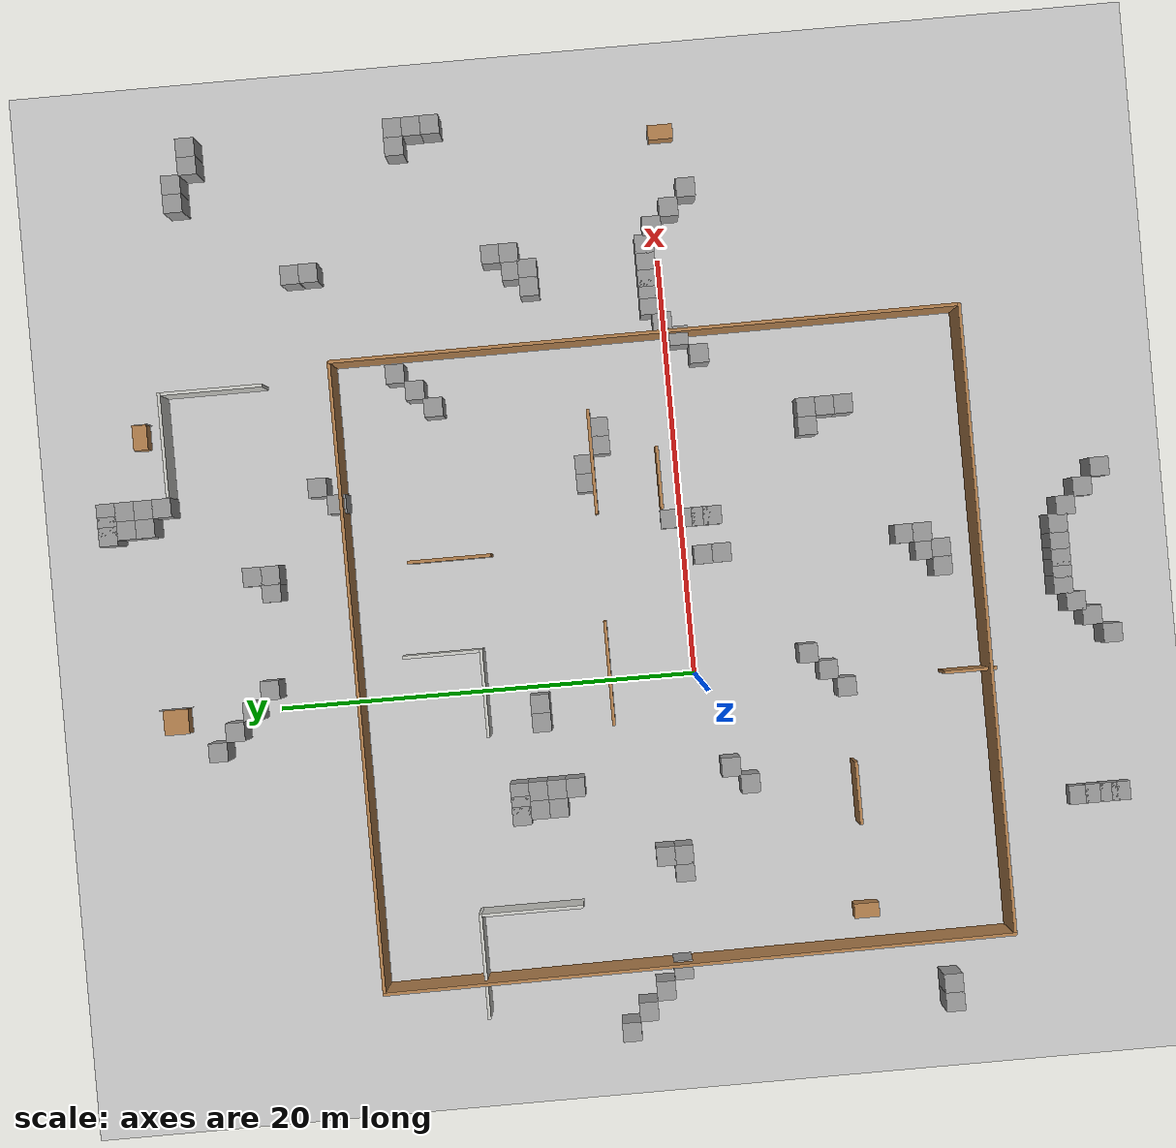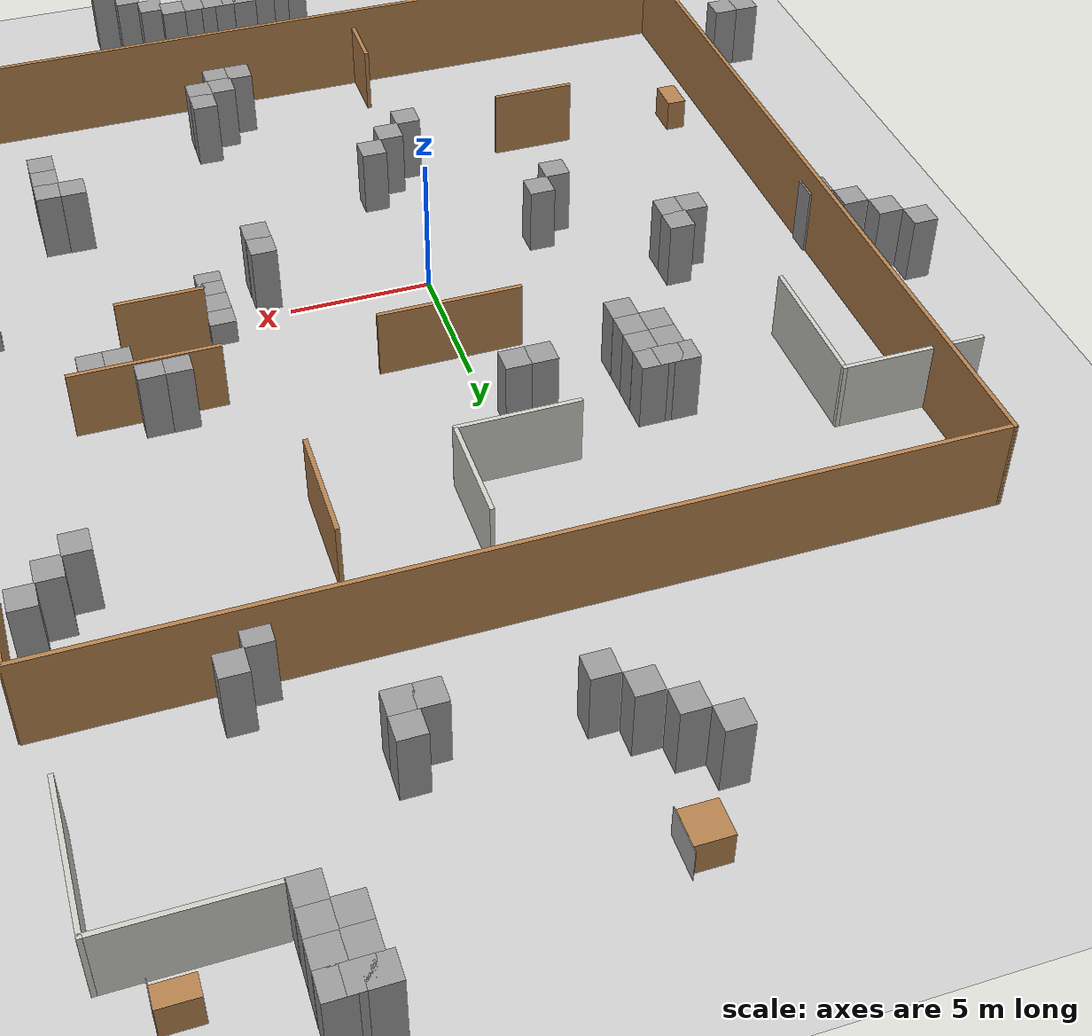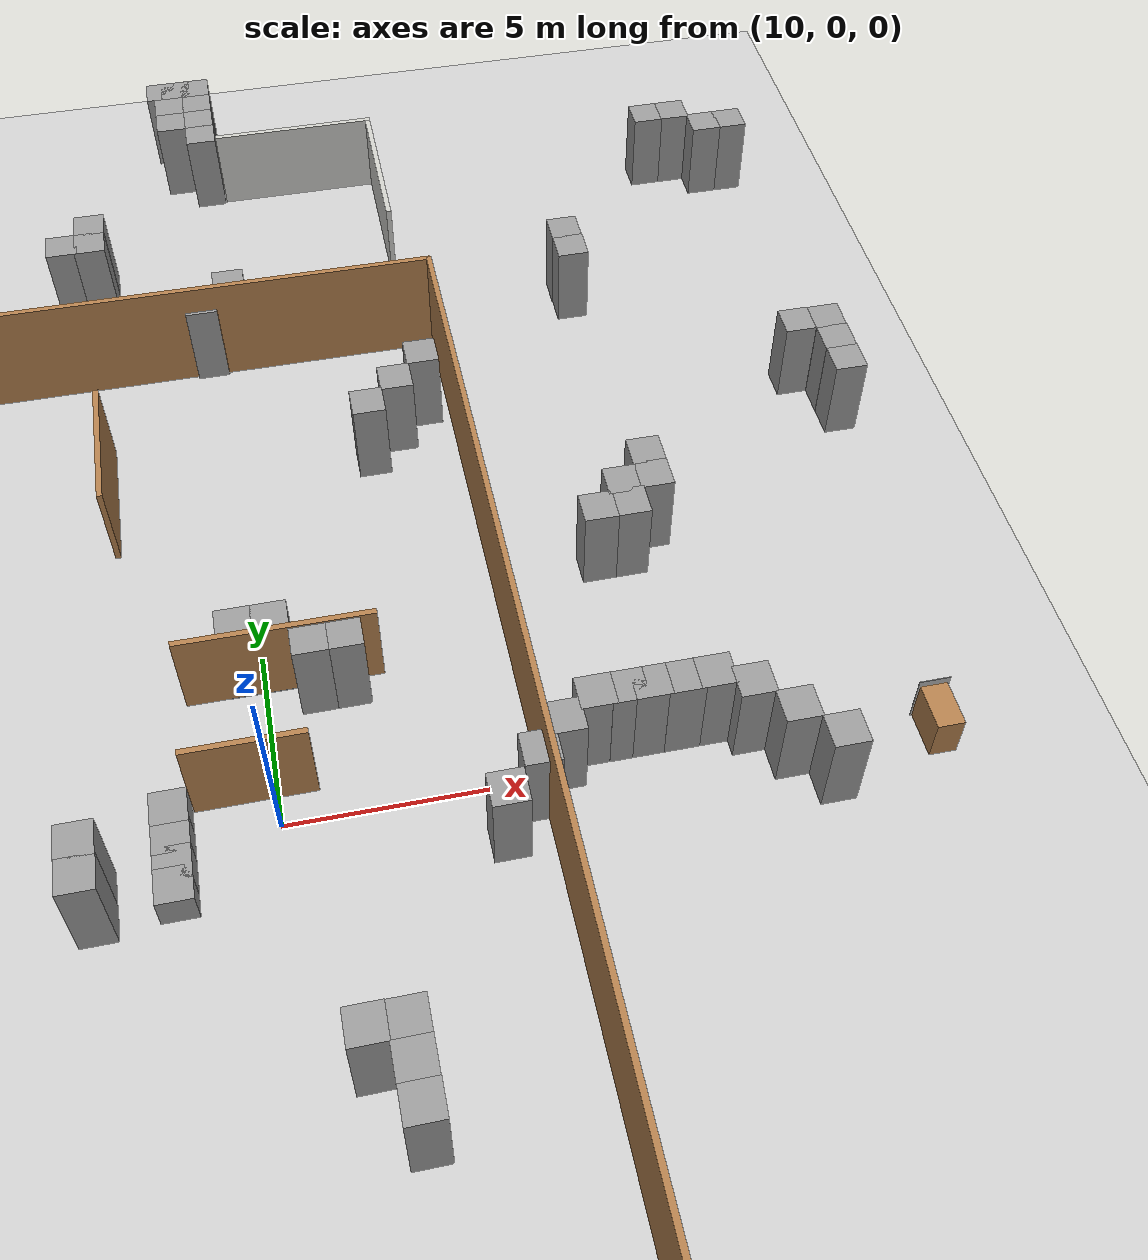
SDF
<sdf version="1.7">
 <world name="default">
  <light name="sun" type="directional">
   <pose>0 0 10 0 -0 0</pose>
   <diffuse>0.8 0.8 0.8 1</diffuse>
   <specular>0.2 0.2 0.2 1</specular>
   <attenuation>
    <range>1000</range>
    <constant>0.9</constant>
    <linear>0.01</linear>
    <quadratic>0.001</quadratic>
   </attenuation>
   <direction>-0.5 0.1 -0.9</direction>
   <spot><inner_angle>0</inner_angle><outer_angle>0</outer_angle><falloff>0</falloff></spot>
  </light>
  <model name="ground_plane">
   <static>1</static>
   <link name="link">
    <collision name="collision">
     <geometry><plane><normal>0 0 1</normal><size>100 100</size></plane></geometry>
     <surface><friction><ode><mu>100</mu><mu2>50</mu2></ode></friction></surface>
    </collision>
    <visual name="visual">
     <cast_shadows>0</cast_shadows>
     <geometry><plane><normal>0 0 1</normal><size>100 100</size></plane></geometry>
     <material>
      <script><uri>file://media/materials/scripts/gazebo.material</uri><name>Gazebo/Grey</name></script>
     </material>
    </visual>
   </link>
  </model>
  <gravity>0 0 -9.8</gravity>
  <magnetic_field>6e-06 2.3e-05 -4.2e-05</magnetic_field>
  <atmosphere type="adiabatic"/>
  <physics type="ode">
   <max_step_size>0.001</max_step_size>
   <real_time_factor>1</real_time_factor>
   <real_time_update_rate>1000</real_time_update_rate>
  </physics>
  <scene><ambient>0.4 0.4 0.4 1</ambient><background>0.7 0.7 0.7 1</background><shadows>0</shadows></scene>
  <spherical_coordinates>
   <surface_model>EARTH_WGS84</surface_model>
   <latitude_deg>0</latitude_deg>
   <longitude_deg>0</longitude_deg>
   <elevation>0</elevation>
   <heading_deg>0</heading_deg>
  </spherical_coordinates>
  <model name="unit_box_0">
   <link name="link">
    <inertial>
     <mass>1</mass>
     <inertia>
      <ixx>0.166667</ixx>
      <ixy>0</ixy>
      <ixz>0</ixz>
      <iyy>0.166667</iyy>
      <iyz>0</iyz>
      <izz>0.166667</izz>
     </inertia>
    </inertial>
    <visual name="visual">
     <geometry><box><size>1.2 1.2 1.2</size></box></geometry>
     <material>
      <script><uri>file://media/materials/scripts/gazebo.material</uri><name>Gazebo/Wood</name></script>
      <shader type="pixel"><normal_map>__default__</normal_map></shader>
      <ambient>1 1 1 1</ambient>
      <diffuse>0.7 0.7 0.7 1</diffuse>
      <specular>0.01 0.01 0.01 1</specular>
      <emissive>0 0 0 1</emissive>
     </material>
    </visual>
    <collision name="collision">
     <geometry><box><size>1.2 1.2 1.2</size></box></geometry>
     <surface>
      <friction>
       <ode><mu>1</mu><mu2>1</mu2><fdir1>0 0 0</fdir1><slip1>0</slip1><slip2>0</slip2></ode>
       <torsional>
        <coefficient>1</coefficient>
        <patch_radius>0</patch_radius>
        <surface_radius>0</surface_radius>
        <use_patch_radius>1</use_patch_radius>
        <ode><slip>0</slip></ode>
       </torsional>
      </friction>
      <bounce><restitution_coefficient>0</restitution_coefficient><threshold>1e+06</threshold></bounce>
      <contact>
       <collide_without_contact>0</collide_without_contact>
       <collide_without_contact_bitmask>1</collide_without_contact_bitmask>
       <collide_bitmask>1</collide_bitmask>
       <ode>
        <soft_cfm>0</soft_cfm>
        <soft_erp>0.2</soft_erp>
        <kp>1e+13</kp>
        <kd>1</kd>
        <max_vel>0.01</max_vel>
        <min_depth>0</min_depth>
       </ode>
       <bullet>
        <split_impulse>1</split_impulse>
        <split_impulse_penetration_threshold>-0.01</split_impulse_penetration_threshold>
        <soft_cfm>0</soft_cfm>
        <soft_erp>0.2</soft_erp>
        <kp>1e+13</kp>
        <kd>1</kd>
       </bullet>
      </contact>
     </surface>
    </collision>
   </link>
   <static>0</static>
   <pose>-0.130923 24.9978 0.6 -0 -0 -0</pose>
  </model>
  <model name="unit_box_1_clone">
   <link name="link">
    <inertial>
     <mass>1</mass>
     <inertia>
      <ixx>0.166667</ixx>
      <ixy>0</ixy>
      <ixz>0</ixz>
      <iyy>0.166667</iyy>
      <iyz>0</iyz>
      <izz>0.166667</izz>
     </inertia>
    </inertial>
    <visual name="visual">
     <geometry><box><size>0.02 1.5 1.2</size></box></geometry>
     <material>
      <script><name>Gazebo/YunXi</name><uri>file://media/materials/scripts/gazebo.material</uri></script>
      <shader type="pixel"><normal_map>__default__</normal_map></shader>
      <ambient>1 1 1 1</ambient>
      <diffuse>0.7 0.7 0.7 1</diffuse>
      <specular>0.01 0.01 0.01 1</specular>
      <emissive>0 0 0 1</emissive>
     </material>
    </visual>
    <collision name="collision">
     <geometry><box><size>0.02 1.5 1.2</size></box></geometry>
     <surface>
      <friction>
       <ode><mu>1</mu><mu2>1</mu2><fdir1>0 0 0</fdir1><slip1>0</slip1><slip2>0</slip2></ode>
       <torsional>
        <coefficient>1</coefficient>
        <patch_radius>0</patch_radius>
        <surface_radius>0</surface_radius>
        <use_patch_radius>1</use_patch_radius>
        <ode><slip>0</slip></ode>
       </torsional>
      </friction>
      <bounce><restitution_coefficient>0</restitution_coefficient><threshold>1e+06</threshold></bounce>
      <contact>
       <collide_without_contact>0</collide_without_contact>
       <collide_without_contact_bitmask>1</collide_without_contact_bitmask>
       <collide_bitmask>1</collide_bitmask>
       <ode>
        <soft_cfm>0</soft_cfm>
        <soft_erp>0.2</soft_erp>
        <kp>1e+13</kp>
        <kd>1</kd>
        <max_vel>0.01</max_vel>
        <min_depth>0</min_depth>
       </ode>
       <bullet>
        <split_impulse>1</split_impulse>
        <split_impulse_penetration_threshold>-0.01</split_impulse_penetration_threshold>
        <soft_cfm>0</soft_cfm>
        <soft_erp>0.2</soft_erp>
        <kp>1e+13</kp>
        <kd>1</kd>
       </bullet>
      </contact>
     </surface>
    </collision>
   </link>
   <static>0</static>
   <pose>0.481184 25.0352 0.599995 7e-06 1.6e-05 0</pose>
  </model>
  <model name="Untitled_clone">
   <link name="Wall_2">
    <pose>0 -2.2325 0 0 -0 0</pose>
    <visual name="Wall_2_Visual">
     <pose>0 0 1.25 0 -0 0</pose>
     <geometry><box><size>5 0.15 2.5</size></box></geometry>
     <material>
      <script><uri>file://media/materials/scripts/gazebo.material</uri><name>Gazebo/CeilingTiled</name></script>
      <ambient>1 1 1 1</ambient>
      <shader type="pixel"/>
     </material>
     <meta><layer>0</layer></meta>
    </visual>
    <collision name="Wall_2_Collision">
     <pose>0 0 1.25 0 -0 0</pose>
     <geometry><box><size>5 0.15 2.5</size></box></geometry>
     <surface>
      <friction>
       <ode><mu>1</mu><mu2>1</mu2><fdir1>0 0 0</fdir1><slip1>0</slip1><slip2>0</slip2></ode>
       <torsional>
        <coefficient>1</coefficient>
        <patch_radius>0</patch_radius>
        <surface_radius>0</surface_radius>
        <use_patch_radius>1</use_patch_radius>
        <ode><slip>0</slip></ode>
       </torsional>
      </friction>
      <bounce><restitution_coefficient>0</restitution_coefficient><threshold>1e+06</threshold></bounce>
      <contact>
       <collide_without_contact>0</collide_without_contact>
       <collide_without_contact_bitmask>1</collide_without_contact_bitmask>
       <collide_bitmask>1</collide_bitmask>
       <ode>
        <soft_cfm>0</soft_cfm>
        <soft_erp>0.2</soft_erp>
        <kp>1e+13</kp>
        <kd>1</kd>
        <max_vel>0.01</max_vel>
        <min_depth>0</min_depth>
       </ode>
       <bullet>
        <split_impulse>1</split_impulse>
        <split_impulse_penetration_threshold>-0.01</split_impulse_penetration_threshold>
        <soft_cfm>0</soft_cfm>
        <soft_erp>0.2</soft_erp>
        <kp>1e+13</kp>
        <kd>1</kd>
       </bullet>
      </contact>
     </surface>
    </collision>
   </link>
   <link name="Wall_2_clone_clone">
    <pose>2.42084 -4.65277 0 0 -0 1.57</pose>
    <inertial>
     <mass>1</mass>
     <inertia><ixx>1</ixx><ixy>0</ixy><ixz>0</ixz><iyy>1</iyy><iyz>0</iyz><izz>1</izz></inertia>
    </inertial>
    <visual name="Wall_2_Visual">
     <pose>0 0 1.25 0 -0 0</pose>
     <geometry><box><size>5 0.15 2.5</size></box></geometry>
     <material>
      <script><uri>file://media/materials/scripts/gazebo.material</uri><name>Gazebo/CeilingTiled</name></script>
      <ambient>1 1 1 1</ambient>
      <shader type="pixel"><normal_map>__default__</normal_map></shader>
      <diffuse>1 1 1 1</diffuse>
      <specular>0 0 0 1</specular>
      <emissive>0 0 0 1</emissive>
     </material>
     <meta><layer>0</layer></meta>
    </visual>
    <collision name="Wall_2_Collision">
     <pose>0 0 1.25 0 -0 0</pose>
     <geometry><box><size>5 0.15 2.5</size></box></geometry>
     <surface>
      <friction>
       <ode><mu>1</mu><mu2>1</mu2><fdir1>0 0 0</fdir1><slip1>0</slip1><slip2>0</slip2></ode>
       <torsional>
        <coefficient>1</coefficient>
        <patch_radius>0</patch_radius>
        <surface_radius>0</surface_radius>
        <use_patch_radius>1</use_patch_radius>
        <ode><slip>0</slip></ode>
       </torsional>
      </friction>
      <bounce><restitution_coefficient>0</restitution_coefficient><threshold>1e+06</threshold></bounce>
      <contact>
       <collide_without_contact>0</collide_without_contact>
       <collide_without_contact_bitmask>1</collide_without_contact_bitmask>
       <collide_bitmask>1</collide_bitmask>
       <ode>
        <soft_cfm>0</soft_cfm>
        <soft_erp>0.2</soft_erp>
        <kp>1e+13</kp>
        <kd>1</kd>
        <max_vel>0.01</max_vel>
        <min_depth>0</min_depth>
       </ode>
       <bullet>
        <split_impulse>1</split_impulse>
        <split_impulse_penetration_threshold>-0.01</split_impulse_penetration_threshold>
        <soft_cfm>0</soft_cfm>
        <soft_erp>0.2</soft_erp>
        <kp>1e+13</kp>
        <kd>1</kd>
       </bullet>
      </contact>
     </surface>
    </collision>
   </link>
   <static>1</static>
   <pose>13.092 26.4824 0 0 -0 0</pose>
  </model>
  <model name="Untitled_0_clone_1">
   <link name="Wall_7_clone_clone">
    <pose>-0.225163 -6.29267 0 0 -0 0</pose>
    <inertial>
     <mass>1</mass>
     <inertia><ixx>1</ixx><ixy>0</ixy><ixz>0</ixz><iyy>1</iyy><iyz>0</iyz><izz>1</izz></inertia>
    </inertial>
    <visual name="Wall_7_Visual">
     <pose>0 0 1.25 0 -0 0</pose>
     <geometry><box><size>3 0.15 2.5</size></box></geometry>
     <material>
      <script><uri>file://media/materials/scripts/gazebo.material</uri><name>Gazebo/Wood</name></script>
      <ambient>1 1 1 1</ambient>
      <shader type="pixel"><normal_map>__default__</normal_map></shader>
      <diffuse>1 1 1 1</diffuse>
      <specular>0.2 0.2 0.2 1</specular>
      <emissive>0 0 0 1</emissive>
     </material>
     <meta><layer>0</layer></meta>
    </visual>
    <collision name="Wall_7_Collision">
     <pose>0 0 1.25 0 -0 0</pose>
     <geometry><box><size>3 0.15 2.5</size></box></geometry>
     <surface>
      <friction>
       <ode><mu>1</mu><mu2>1</mu2><fdir1>0 0 0</fdir1><slip1>0</slip1><slip2>0</slip2></ode>
       <torsional>
        <coefficient>1</coefficient>
        <patch_radius>0</patch_radius>
        <surface_radius>0</surface_radius>
        <use_patch_radius>1</use_patch_radius>
        <ode><slip>0</slip></ode>
       </torsional>
      </friction>
      <bounce><restitution_coefficient>0</restitution_coefficient><threshold>1e+06</threshold></bounce>
      <contact>
       <collide_without_contact>0</collide_without_contact>
       <collide_without_contact_bitmask>1</collide_without_contact_bitmask>
       <collide_bitmask>1</collide_bitmask>
       <ode>
        <soft_cfm>0</soft_cfm>
        <soft_erp>0.2</soft_erp>
        <kp>1e+13</kp>
        <kd>1</kd>
        <max_vel>0.01</max_vel>
        <min_depth>0</min_depth>
       </ode>
       <bullet>
        <split_impulse>1</split_impulse>
        <split_impulse_penetration_threshold>-0.01</split_impulse_penetration_threshold>
        <soft_cfm>0</soft_cfm>
        <soft_erp>0.2</soft_erp>
        <kp>1e+13</kp>
        <kd>1</kd>
       </bullet>
      </contact>
     </surface>
    </collision>
   </link>
   <static>1</static>
   <pose>9.71955 7.19221 0 0 -0 0</pose>
  </model>
  <model name="unit_box_1_clone_0_clone_clone">
   <link name="link">
    <inertial>
     <mass>1</mass>
     <inertia>
      <ixx>0.166667</ixx>
      <ixy>0</ixy>
      <ixz>0</ixz>
      <iyy>0.166667</iyy>
      <iyz>0</iyz>
      <izz>0.166667</izz>
     </inertia>
    </inertial>
    <visual name="visual">
     <geometry><box><size>0.02 0.8 1.4</size></box></geometry>
     <material>
      <script><name>Gazebo/LingXi</name><uri>file://media/materials/scripts/gazebo.material</uri></script>
      <shader type="pixel"><normal_map>__default__</normal_map></shader>
      <ambient>1 1 1 1</ambient>
      <diffuse>0.7 0.7 0.7 1</diffuse>
      <specular>0.01 0.01 0.01 1</specular>
      <emissive>0 0 0 1</emissive>
     </material>
     <pose>0 0 0 0 -0 1.5707</pose>
    </visual>
    <collision name="collision">
     <pose>0 0 0 0 -0 1.5707</pose>
     <geometry><box><size>0.02 0.8 1.4</size></box></geometry>
     <surface>
      <friction>
       <ode><mu>1</mu><mu2>1</mu2><fdir1>0 0 0</fdir1><slip1>0</slip1><slip2>0</slip2></ode>
       <torsional>
        <coefficient>1</coefficient>
        <patch_radius>0</patch_radius>
        <surface_radius>0</surface_radius>
        <use_patch_radius>1</use_patch_radius>
        <ode><slip>0</slip></ode>
       </torsional>
      </friction>
      <bounce><restitution_coefficient>0</restitution_coefficient><threshold>1e+06</threshold></bounce>
      <contact>
       <collide_without_contact>0</collide_without_contact>
       <collide_without_contact_bitmask>1</collide_without_contact_bitmask>
       <collide_bitmask>1</collide_bitmask>
       <ode>
        <soft_cfm>0</soft_cfm>
        <soft_erp>0.2</soft_erp>
        <kp>1e+13</kp>
        <kd>1</kd>
        <max_vel>0.01</max_vel>
        <min_depth>0</min_depth>
       </ode>
       <bullet>
        <split_impulse>1</split_impulse>
        <split_impulse_penetration_threshold>-0.01</split_impulse_penetration_threshold>
        <soft_cfm>0</soft_cfm>
        <soft_erp>0.2</soft_erp>
        <kp>1e+13</kp>
        <kd>1</kd>
       </bullet>
      </contact>
     </surface>
    </collision>
   </link>
   <static>0</static>
   <pose>26.036 -0.003836 0.699998 3e-06 -4e-06 5.1e-05</pose>
  </model>
  <model name="unit_box_1_clone_0">
   <link name="link">
    <inertial>
     <mass>1</mass>
     <inertia>
      <ixx>0.166667</ixx>
      <ixy>0</ixy>
      <ixz>0</ixz>
      <iyy>0.166667</iyy>
      <iyz>0</iyz>
      <izz>0.166667</izz>
     </inertia>
    </inertial>
    <visual name="visual">
     <geometry><box><size>0.02 0.8 1.4</size></box></geometry>
     <material>
      <script><name>Gazebo/ShiHao</name><uri>file://media/materials/scripts/gazebo.material</uri></script>
      <shader type="pixel"><normal_map>__default__</normal_map></shader>
      <ambient>1 1 1 1</ambient>
      <diffuse>0.7 0.7 0.7 1</diffuse>
      <specular>0.01 0.01 0.01 1</specular>
      <emissive>0 0 0 1</emissive>
     </material>
    </visual>
    <collision name="collision">
     <geometry><box><size>0.02 0.8 1.4</size></box></geometry>
     <surface>
      <friction>
       <ode><mu>1</mu><mu2>1</mu2><fdir1>0 0 0</fdir1><slip1>0</slip1><slip2>0</slip2></ode>
       <torsional>
        <coefficient>1</coefficient>
        <patch_radius>0</patch_radius>
        <surface_radius>0</surface_radius>
        <use_patch_radius>1</use_patch_radius>
        <ode><slip>0</slip></ode>
       </torsional>
      </friction>
      <bounce><restitution_coefficient>0</restitution_coefficient><threshold>1e+06</threshold></bounce>
      <contact>
       <collide_without_contact>0</collide_without_contact>
       <collide_without_contact_bitmask>1</collide_without_contact_bitmask>
       <collide_bitmask>1</collide_bitmask>
       <ode>
        <soft_cfm>0</soft_cfm>
        <soft_erp>0.2</soft_erp>
        <kp>1e+13</kp>
        <kd>1</kd>
        <max_vel>0.01</max_vel>
        <min_depth>0</min_depth>
       </ode>
       <bullet>
        <split_impulse>1</split_impulse>
        <split_impulse_penetration_threshold>-0.01</split_impulse_penetration_threshold>
        <soft_cfm>0</soft_cfm>
        <soft_erp>0.2</soft_erp>
        <kp>1e+13</kp>
        <kd>1</kd>
       </bullet>
      </contact>
     </surface>
    </collision>
   </link>
   <static>0</static>
   <pose>14.2294 25.5003 0.699998 -5e-06 -4e-06 -0.000161</pose>
  </model>
  <model name="unit_box_0_clone">
   <link name="link">
    <inertial>
     <mass>1</mass>
     <inertia>
      <ixx>0.166667</ixx>
      <ixy>0</ixy>
      <ixz>0</ixz>
      <iyy>0.166667</iyy>
      <iyz>0</iyz>
      <izz>0.166667</izz>
     </inertia>
    </inertial>
    <visual name="visual">
     <geometry><box><size>1.2 0.7 1.2</size></box></geometry>
     <material>
      <script><uri>file://media/materials/scripts/gazebo.material</uri><name>Gazebo/Wood</name></script>
      <shader type="pixel"><normal_map>__default__</normal_map></shader>
      <ambient>1 1 1 1</ambient>
      <diffuse>0.7 0.7 0.7 1</diffuse>
      <specular>0.01 0.01 0.01 1</specular>
      <emissive>0 0 0 1</emissive>
     </material>
    </visual>
    <collision name="collision">
     <geometry><box><size>1.2 0.7 1.2</size></box></geometry>
     <surface>
      <friction>
       <ode><mu>1</mu><mu2>1</mu2><fdir1>0 0 0</fdir1><slip1>0</slip1><slip2>0</slip2></ode>
       <torsional>
        <coefficient>1</coefficient>
        <patch_radius>0</patch_radius>
        <surface_radius>0</surface_radius>
        <use_patch_radius>1</use_patch_radius>
        <ode><slip>0</slip></ode>
       </torsional>
      </friction>
      <bounce><restitution_coefficient>0</restitution_coefficient><threshold>1e+06</threshold></bounce>
      <contact>
       <collide_without_contact>0</collide_without_contact>
       <collide_without_contact_bitmask>1</collide_without_contact_bitmask>
       <collide_bitmask>1</collide_bitmask>
       <ode>
        <soft_cfm>0</soft_cfm>
        <soft_erp>0.2</soft_erp>
        <kp>1e+13</kp>
        <kd>1</kd>
        <max_vel>0.01</max_vel>
        <min_depth>0</min_depth>
       </ode>
       <bullet>
        <split_impulse>1</split_impulse>
        <split_impulse_penetration_threshold>-0.01</split_impulse_penetration_threshold>
        <soft_cfm>0</soft_cfm>
        <soft_erp>0.2</soft_erp>
        <kp>1e+13</kp>
        <kd>1</kd>
       </bullet>
      </contact>
     </surface>
    </collision>
   </link>
   <static>0</static>
   <pose>13.619 25.5346 0.600002 0 3e-06 -0.000144</pose>
  </model>
  <model name="unit_box_0_clone_clone">
   <link name="link">
    <inertial>
     <mass>1</mass>
     <inertia>
      <ixx>0.166667</ixx>
      <ixy>0</ixy>
      <ixz>0</ixz>
      <iyy>0.166667</iyy>
      <iyz>0</iyz>
      <izz>0.166667</izz>
     </inertia>
    </inertial>
    <visual name="visual">
     <geometry><box><size>0.7 1.2 1.2</size></box></geometry>
     <material>
      <script><uri>file://media/materials/scripts/gazebo.material</uri><name>Gazebo/Wood</name></script>
      <shader type="pixel"><normal_map>__default__</normal_map></shader>
      <ambient>1 1 1 1</ambient>
      <diffuse>0.7 0.7 0.7 1</diffuse>
      <specular>0.01 0.01 0.01 1</specular>
      <emissive>0 0 0 1</emissive>
     </material>
    </visual>
    <collision name="collision">
     <geometry><box><size>0.7 1.2 1.2</size></box></geometry>
     <surface>
      <friction>
       <ode><mu>1</mu><mu2>1</mu2><fdir1>0 0 0</fdir1><slip1>0</slip1><slip2>0</slip2></ode>
       <torsional>
        <coefficient>1</coefficient>
        <patch_radius>0</patch_radius>
        <surface_radius>0</surface_radius>
        <use_patch_radius>1</use_patch_radius>
        <ode><slip>0</slip></ode>
       </torsional>
      </friction>
      <bounce><restitution_coefficient>0</restitution_coefficient><threshold>1e+06</threshold></bounce>
      <contact>
       <collide_without_contact>0</collide_without_contact>
       <collide_without_contact_bitmask>1</collide_without_contact_bitmask>
       <collide_bitmask>1</collide_bitmask>
       <ode>
        <soft_cfm>0</soft_cfm>
        <soft_erp>0.2</soft_erp>
        <kp>1e+13</kp>
        <kd>1</kd>
        <max_vel>0.01</max_vel>
        <min_depth>0</min_depth>
       </ode>
       <bullet>
        <split_impulse>1</split_impulse>
        <split_impulse_penetration_threshold>-0.01</split_impulse_penetration_threshold>
        <soft_cfm>0</soft_cfm>
        <soft_erp>0.2</soft_erp>
        <kp>1e+13</kp>
        <kd>1</kd>
       </bullet>
      </contact>
     </surface>
    </collision>
   </link>
   <static>0</static>
   <pose>26.0358 -0.614544 0.6 0 -0 0.000351</pose>
  </model>
  <model name="Untitled_0_clone">
   <link name="Wall_7_clone">
    <pose>-2.04571 -4.92466 0 0 -0 0</pose>
    <inertial>
     <mass>1</mass>
     <inertia><ixx>1</ixx><ixy>0</ixy><ixz>0</ixz><iyy>1</iyy><iyz>0</iyz><izz>1</izz></inertia>
    </inertial>
    <visual name="Wall_7_Visual">
     <pose>0 0 1.25 0 -0 1.5707</pose>
     <geometry><box><size>4 0.15 2.5</size></box></geometry>
     <material>
      <script><uri>file://media/materials/scripts/gazebo.material</uri><name>Gazebo/Wood</name></script>
      <ambient>1 1 1 1</ambient>
      <shader type="pixel"><normal_map>__default__</normal_map></shader>
      <diffuse>1 1 1 1</diffuse>
      <specular>0.2 0.2 0.2 1</specular>
      <emissive>0 0 0 1</emissive>
     </material>
     <meta><layer>0</layer></meta>
    </visual>
    <collision name="Wall_7_Collision">
     <pose>0 0 1.25 0 -0 1.57079</pose>
     <geometry><box><size>4 0.15 2.5</size></box></geometry>
     <surface>
      <friction>
       <ode><mu>1</mu><mu2>1</mu2><fdir1>0 0 0</fdir1><slip1>0</slip1><slip2>0</slip2></ode>
       <torsional>
        <coefficient>1</coefficient>
        <patch_radius>0</patch_radius>
        <surface_radius>0</surface_radius>
        <use_patch_radius>1</use_patch_radius>
        <ode><slip>0</slip></ode>
       </torsional>
      </friction>
      <bounce><restitution_coefficient>0</restitution_coefficient><threshold>1e+06</threshold></bounce>
      <contact>
       <collide_without_contact>0</collide_without_contact>
       <collide_without_contact_bitmask>1</collide_without_contact_bitmask>
       <collide_bitmask>1</collide_bitmask>
       <ode>
        <soft_cfm>0</soft_cfm>
        <soft_erp>0.2</soft_erp>
        <kp>1e+13</kp>
        <kd>1</kd>
        <max_vel>0.01</max_vel>
        <min_depth>0</min_depth>
       </ode>
       <bullet>
        <split_impulse>1</split_impulse>
        <split_impulse_penetration_threshold>-0.01</split_impulse_penetration_threshold>
        <soft_cfm>0</soft_cfm>
        <soft_erp>0.2</soft_erp>
        <kp>1e+13</kp>
        <kd>1</kd>
       </bullet>
      </contact>
     </surface>
    </collision>
   </link>
   <static>1</static>
   <pose>8.55551 16.1176 0 0 -0 0</pose>
  </model>
  <model name="Untitled_clone_clone_clone_clone">
   <link name="Wall_2_clone">
    <pose>-0.408024 -2.20516 0 0 -0 0</pose>
    <inertial>
     <mass>1</mass>
     <inertia><ixx>1</ixx><ixy>0</ixy><ixz>0</ixz><iyy>1</iyy><iyz>0</iyz><izz>1</izz></inertia>
    </inertial>
    <visual name="Wall_2_Visual">
     <pose>0 0 1.25 0 -0 0</pose>
     <geometry><box><size>4.2 0.15 2.5</size></box></geometry>
     <material>
      <script><uri>file://media/materials/scripts/gazebo.material</uri><name>Gazebo/CeilingTiled</name></script>
      <ambient>1 1 1 1</ambient>
      <shader type="pixel"><normal_map>__default__</normal_map></shader>
      <diffuse>1 1 1 1</diffuse>
      <specular>0 0 0 1</specular>
      <emissive>0 0 0 1</emissive>
     </material>
     <meta><layer>0</layer></meta>
    </visual>
    <collision name="Wall_2_Collision">
     <pose>0 0 1.25 0 -0 0</pose>
     <geometry><box><size>4.2 0.15 2.5</size></box></geometry>
     <surface>
      <friction>
       <ode><mu>1</mu><mu2>1</mu2><fdir1>0 0 0</fdir1><slip1>0</slip1><slip2>0</slip2></ode>
       <torsional>
        <coefficient>1</coefficient>
        <patch_radius>0</patch_radius>
        <surface_radius>0</surface_radius>
        <use_patch_radius>1</use_patch_radius>
        <ode><slip>0</slip></ode>
       </torsional>
      </friction>
      <bounce><restitution_coefficient>0</restitution_coefficient><threshold>1e+06</threshold></bounce>
      <contact>
       <collide_without_contact>0</collide_without_contact>
       <collide_without_contact_bitmask>1</collide_without_contact_bitmask>
       <collide_bitmask>1</collide_bitmask>
       <ode>
        <soft_cfm>0</soft_cfm>
        <soft_erp>0.2</soft_erp>
        <kp>1e+13</kp>
        <kd>1</kd>
        <max_vel>0.01</max_vel>
        <min_depth>0</min_depth>
       </ode>
       <bullet>
        <split_impulse>1</split_impulse>
        <split_impulse_penetration_threshold>-0.01</split_impulse_penetration_threshold>
        <soft_cfm>0</soft_cfm>
        <soft_erp>0.2</soft_erp>
        <kp>1e+13</kp>
        <kd>1</kd>
       </bullet>
      </contact>
     </surface>
    </collision>
   </link>
   <link name="Wall_2_clone_clone_clone_clone_clone">
    <pose>1.61868 -0.372186 0 0 -0 1.57</pose>
    <inertial>
     <mass>1</mass>
     <inertia><ixx>1</ixx><ixy>0</ixy><ixz>0</ixz><iyy>1</iyy><iyz>0</iyz><izz>1</izz></inertia>
    </inertial>
    <visual name="Wall_2_Visual">
     <pose>0 0 1.25 0 -0 0</pose>
     <geometry><box><size>3.8 0.15 2.5</size></box></geometry>
     <material>
      <script><uri>file://media/materials/scripts/gazebo.material</uri><name>Gazebo/CeilingTiled</name></script>
      <ambient>1 1 1 1</ambient>
      <shader type="pixel"><normal_map>__default__</normal_map></shader>
      <diffuse>1 1 1 1</diffuse>
      <specular>0 0 0 1</specular>
      <emissive>0 0 0 1</emissive>
     </material>
     <meta><layer>0</layer></meta>
    </visual>
    <collision name="Wall_2_Collision">
     <pose>0 0 1.25 0 -0 0</pose>
     <geometry><box><size>3.8 0.15 2.5</size></box></geometry>
     <surface>
      <friction>
       <ode><mu>1</mu><mu2>1</mu2><fdir1>0 0 0</fdir1><slip1>0</slip1><slip2>0</slip2></ode>
       <torsional>
        <coefficient>1</coefficient>
        <patch_radius>0</patch_radius>
        <surface_radius>0</surface_radius>
        <use_patch_radius>1</use_patch_radius>
        <ode><slip>0</slip></ode>
       </torsional>
      </friction>
      <bounce><restitution_coefficient>0</restitution_coefficient><threshold>1e+06</threshold></bounce>
      <contact>
       <collide_without_contact>0</collide_without_contact>
       <collide_without_contact_bitmask>1</collide_without_contact_bitmask>
       <collide_bitmask>1</collide_bitmask>
       <ode>
        <soft_cfm>0</soft_cfm>
        <soft_erp>0.2</soft_erp>
        <kp>1e+13</kp>
        <kd>1</kd>
        <max_vel>0.01</max_vel>
        <min_depth>0</min_depth>
       </ode>
       <bullet>
        <split_impulse>1</split_impulse>
        <split_impulse_penetration_threshold>-0.01</split_impulse_penetration_threshold>
        <soft_cfm>0</soft_cfm>
        <soft_erp>0.2</soft_erp>
        <kp>1e+13</kp>
        <kd>1</kd>
       </bullet>
      </contact>
     </surface>
    </collision>
   </link>
   <static>1</static>
   <pose>0.41018 12.2822 0 0 -0 0</pose>
  </model>
  <model name="unit_box">
   <link name="link">
    <inertial>
     <mass>1</mass>
     <inertia>
      <ixx>0.166667</ixx>
      <ixy>0</ixy>
      <ixz>0</ixz>
      <iyy>0.166667</iyy>
      <iyz>0</iyz>
      <izz>0.166667</izz>
     </inertia>
    </inertial>
    <visual name="visual">
     <geometry><box><size>0.9 0.9 0.9</size></box></geometry>
     <material>
      <script><name>Gazebo/Grey</name><uri>file://media/materials/scripts/gazebo.material</uri></script>
      <shader type="pixel"><normal_map>__default__</normal_map></shader>
      <ambient>0.3 0.3 0.3 1</ambient>
      <diffuse>0.7 0.7 0.7 1</diffuse>
      <specular>0.01 0.01 0.01 1</specular>
      <emissive>0 0 0 1</emissive>
     </material>
    </visual>
    <collision name="collision">
     <geometry><box><size>0.9 0.9 0.9</size></box></geometry>
     <surface>
      <friction>
       <ode><mu>1</mu><mu2>1</mu2><fdir1>0 0 0</fdir1><slip1>0</slip1><slip2>0</slip2></ode>
       <torsional>
        <coefficient>1</coefficient>
        <patch_radius>0</patch_radius>
        <surface_radius>0</surface_radius>
        <use_patch_radius>1</use_patch_radius>
        <ode><slip>0</slip></ode>
       </torsional>
      </friction>
      <bounce><restitution_coefficient>0</restitution_coefficient><threshold>1e+06</threshold></bounce>
      <contact>
       <collide_without_contact>0</collide_without_contact>
       <collide_without_contact_bitmask>1</collide_without_contact_bitmask>
       <collide_bitmask>1</collide_bitmask>
       <ode>
        <soft_cfm>0</soft_cfm>
        <soft_erp>0.2</soft_erp>
        <kp>1e+13</kp>
        <kd>1</kd>
        <max_vel>0.01</max_vel>
        <min_depth>0</min_depth>
       </ode>
       <bullet>
        <split_impulse>1</split_impulse>
        <split_impulse_penetration_threshold>-0.01</split_impulse_penetration_threshold>
        <soft_cfm>0</soft_cfm>
        <soft_erp>0.2</soft_erp>
        <kp>1e+13</kp>
        <kd>1</kd>
       </bullet>
      </contact>
     </surface>
    </collision>
   </link>
   <link name="link_clone_0_clone">
    <inertial>
     <mass>1</mass>
     <inertia>
      <ixx>0.166667</ixx>
      <ixy>0</ixy>
      <ixz>0</ixz>
      <iyy>0.166667</iyy>
      <iyz>0</iyz>
      <izz>0.166667</izz>
     </inertia>
    </inertial>
    <pose>0.001814 0.546546 0 0 -0 0</pose>
    <visual name="visual">
     <geometry><box><size>0.9 0.9 0.9</size></box></geometry>
     <material>
      <script><name>Gazebo/Grey</name><uri>file://media/materials/scripts/gazebo.material</uri></script>
      <shader type="pixel"><normal_map>__default__</normal_map></shader>
      <ambient>0.3 0.3 0.3 1</ambient>
      <diffuse>0.7 0.7 0.7 1</diffuse>
      <specular>0.01 0.01 0.01 1</specular>
      <emissive>0 0 0 1</emissive>
     </material>
    </visual>
    <collision name="collision">
     <geometry><box><size>0.9 0.9 0.9</size></box></geometry>
     <surface>
      <friction>
       <ode><mu>1</mu><mu2>1</mu2><fdir1>0 0 0</fdir1><slip1>0</slip1><slip2>0</slip2></ode>
       <torsional>
        <coefficient>1</coefficient>
        <patch_radius>0</patch_radius>
        <surface_radius>0</surface_radius>
        <use_patch_radius>1</use_patch_radius>
        <ode><slip>0</slip></ode>
       </torsional>
      </friction>
      <bounce><restitution_coefficient>0</restitution_coefficient><threshold>1e+06</threshold></bounce>
      <contact>
       <collide_without_contact>0</collide_without_contact>
       <collide_without_contact_bitmask>1</collide_without_contact_bitmask>
       <collide_bitmask>1</collide_bitmask>
       <ode>
        <soft_cfm>0</soft_cfm>
        <soft_erp>0.2</soft_erp>
        <kp>1e+13</kp>
        <kd>1</kd>
        <max_vel>0.01</max_vel>
        <min_depth>0</min_depth>
       </ode>
       <bullet>
        <split_impulse>1</split_impulse>
        <split_impulse_penetration_threshold>-0.01</split_impulse_penetration_threshold>
        <soft_cfm>0</soft_cfm>
        <soft_erp>0.2</soft_erp>
        <kp>1e+13</kp>
        <kd>1</kd>
       </bullet>
      </contact>
     </surface>
    </collision>
   </link>
   <link name="link_clone_0_clone_clone">
    <inertial>
     <mass>1</mass>
     <inertia>
      <ixx>0.166667</ixx>
      <ixy>0</ixy>
      <ixz>0</ixz>
      <iyy>0.166667</iyy>
      <iyz>0</iyz>
      <izz>0.166667</izz>
     </inertia>
    </inertial>
    <pose>0.000695 1.26691 0 0 -0 0</pose>
    <visual name="visual">
     <geometry><box><size>0.9 0.9 0.9</size></box></geometry>
     <material>
      <script><name>Gazebo/Grey</name><uri>file://media/materials/scripts/gazebo.material</uri></script>
      <shader type="pixel"><normal_map>__default__</normal_map></shader>
      <ambient>0.3 0.3 0.3 1</ambient>
      <diffuse>0.7 0.7 0.7 1</diffuse>
      <specular>0.01 0.01 0.01 1</specular>
      <emissive>0 0 0 1</emissive>
     </material>
    </visual>
    <collision name="collision">
     <geometry><box><size>0.9 0.9 0.9</size></box></geometry>
     <surface>
      <friction>
       <ode><mu>1</mu><mu2>1</mu2><fdir1>0 0 0</fdir1><slip1>0</slip1><slip2>0</slip2></ode>
       <torsional>
        <coefficient>1</coefficient>
        <patch_radius>0</patch_radius>
        <surface_radius>0</surface_radius>
        <use_patch_radius>1</use_patch_radius>
        <ode><slip>0</slip></ode>
       </torsional>
      </friction>
      <bounce><restitution_coefficient>0</restitution_coefficient><threshold>1e+06</threshold></bounce>
      <contact>
       <collide_without_contact>0</collide_without_contact>
       <collide_without_contact_bitmask>1</collide_without_contact_bitmask>
       <collide_bitmask>1</collide_bitmask>
       <ode>
        <soft_cfm>0</soft_cfm>
        <soft_erp>0.2</soft_erp>
        <kp>1e+13</kp>
        <kd>1</kd>
        <max_vel>0.01</max_vel>
        <min_depth>0</min_depth>
       </ode>
       <bullet>
        <split_impulse>1</split_impulse>
        <split_impulse_penetration_threshold>-0.01</split_impulse_penetration_threshold>
        <soft_cfm>0</soft_cfm>
        <soft_erp>0.2</soft_erp>
        <kp>1e+13</kp>
        <kd>1</kd>
       </bullet>
      </contact>
     </surface>
    </collision>
   </link>
   <link name="link_clone_0_clone_clone_0">
    <inertial>
     <mass>1</mass>
     <inertia>
      <ixx>0.166667</ixx>
      <ixy>0</ixy>
      <ixz>0</ixz>
      <iyy>0.166667</iyy>
      <iyz>0</iyz>
      <izz>0.166667</izz>
     </inertia>
    </inertial>
    <pose>-9.13666 8.99649 0 0 -0 0</pose>
    <visual name="visual">
     <geometry><box><size>0.9 0.9 4</size></box></geometry>
     <material>
      <script><name>Gazebo/Grey</name><uri>file://media/materials/scripts/gazebo.material</uri></script>
      <shader type="pixel"><normal_map>__default__</normal_map></shader>
      <ambient>0.3 0.3 0.3 1</ambient>
      <diffuse>0.7 0.7 0.7 1</diffuse>
      <specular>0.01 0.01 0.01 1</specular>
      <emissive>0 0 0 1</emissive>
     </material>
    </visual>
    <collision name="collision">
     <geometry><box><size>0.9 0.9 4</size></box></geometry>
     <surface>
      <friction>
       <ode><mu>1</mu><mu2>1</mu2><fdir1>0 0 0</fdir1><slip1>0</slip1><slip2>0</slip2></ode>
       <torsional>
        <coefficient>1</coefficient>
        <patch_radius>0</patch_radius>
        <surface_radius>0</surface_radius>
        <use_patch_radius>1</use_patch_radius>
        <ode><slip>0</slip></ode>
       </torsional>
      </friction>
      <bounce><restitution_coefficient>0</restitution_coefficient><threshold>1e+06</threshold></bounce>
      <contact>
       <collide_without_contact>0</collide_without_contact>
       <collide_without_contact_bitmask>1</collide_without_contact_bitmask>
       <collide_bitmask>1</collide_bitmask>
       <ode>
        <soft_cfm>0</soft_cfm>
        <soft_erp>0.2</soft_erp>
        <kp>1e+13</kp>
        <kd>1</kd>
        <max_vel>0.01</max_vel>
        <min_depth>0</min_depth>
       </ode>
       <bullet>
        <split_impulse>1</split_impulse>
        <split_impulse_penetration_threshold>-0.01</split_impulse_penetration_threshold>
        <soft_cfm>0</soft_cfm>
        <soft_erp>0.2</soft_erp>
        <kp>1e+13</kp>
        <kd>1</kd>
       </bullet>
      </contact>
     </surface>
    </collision>
   </link>
   <link name="link_clone_0_clone_clone_1">
    <inertial>
     <mass>1</mass>
     <inertia>
      <ixx>0.166667</ixx>
      <ixy>0</ixy>
      <ixz>0</ixz>
      <iyy>0.166667</iyy>
      <iyz>0</iyz>
      <izz>0.166667</izz>
     </inertia>
    </inertial>
    <pose>-8.25334 8.99525 0 0 -0 0</pose>
    <visual name="visual">
     <geometry><box><size>0.9 0.9 4</size></box></geometry>
     <material>
      <script><name>Gazebo/Grey</name><uri>file://media/materials/scripts/gazebo.material</uri></script>
      <shader type="pixel"><normal_map>__default__</normal_map></shader>
      <ambient>0.3 0.3 0.3 1</ambient>
      <diffuse>0.7 0.7 0.7 1</diffuse>
      <specular>0.01 0.01 0.01 1</specular>
      <emissive>0 0 0 1</emissive>
     </material>
    </visual>
    <collision name="collision">
     <geometry><box><size>0.9 0.9 4</size></box></geometry>
     <surface>
      <friction>
       <ode><mu>1</mu><mu2>1</mu2><fdir1>0 0 0</fdir1><slip1>0</slip1><slip2>0</slip2></ode>
       <torsional>
        <coefficient>1</coefficient>
        <patch_radius>0</patch_radius>
        <surface_radius>0</surface_radius>
        <use_patch_radius>1</use_patch_radius>
        <ode><slip>0</slip></ode>
       </torsional>
      </friction>
      <bounce><restitution_coefficient>0</restitution_coefficient><threshold>1e+06</threshold></bounce>
      <contact>
       <collide_without_contact>0</collide_without_contact>
       <collide_without_contact_bitmask>1</collide_without_contact_bitmask>
       <collide_bitmask>1</collide_bitmask>
       <ode>
        <soft_cfm>0</soft_cfm>
        <soft_erp>0.2</soft_erp>
        <kp>1e+13</kp>
        <kd>1</kd>
        <max_vel>0.01</max_vel>
        <min_depth>0</min_depth>
       </ode>
       <bullet>
        <split_impulse>1</split_impulse>
        <split_impulse_penetration_threshold>-0.01</split_impulse_penetration_threshold>
        <soft_cfm>0</soft_cfm>
        <soft_erp>0.2</soft_erp>
        <kp>1e+13</kp>
        <kd>1</kd>
       </bullet>
      </contact>
     </surface>
    </collision>
   </link>
   <link name="link_clone_0_clone_clone_3_clone_0">
    <inertial>
     <mass>1</mass>
     <inertia>
      <ixx>0.166667</ixx>
      <ixy>0</ixy>
      <ixz>0</ixz>
      <iyy>0.166667</iyy>
      <iyz>0</iyz>
      <izz>0.166667</izz>
     </inertia>
    </inertial>
    <pose>1.46921 28.7387 0 0 -0 0</pose>
    <visual name="visual">
     <geometry><box><size>0.9 0.9 4</size></box></geometry>
     <material>
      <script><name>Gazebo/Grey</name><uri>file://media/materials/scripts/gazebo.material</uri></script>
      <shader type="pixel"><normal_map>__default__</normal_map></shader>
      <ambient>0.3 0.3 0.3 1</ambient>
      <diffuse>0.7 0.7 0.7 1</diffuse>
      <specular>0.01 0.01 0.01 1</specular>
      <emissive>0 0 0 1</emissive>
     </material>
    </visual>
    <collision name="collision">
     <geometry><box><size>0.9 0.9 4</size></box></geometry>
     <surface>
      <friction>
       <ode><mu>1</mu><mu2>1</mu2><fdir1>0 0 0</fdir1><slip1>0</slip1><slip2>0</slip2></ode>
       <torsional>
        <coefficient>1</coefficient>
        <patch_radius>0</patch_radius>
        <surface_radius>0</surface_radius>
        <use_patch_radius>1</use_patch_radius>
        <ode><slip>0</slip></ode>
       </torsional>
      </friction>
      <bounce><restitution_coefficient>0</restitution_coefficient><threshold>1e+06</threshold></bounce>
      <contact>
       <collide_without_contact>0</collide_without_contact>
       <collide_without_contact_bitmask>1</collide_without_contact_bitmask>
       <collide_bitmask>1</collide_bitmask>
       <ode>
        <soft_cfm>0</soft_cfm>
        <soft_erp>0.2</soft_erp>
        <kp>1e+13</kp>
        <kd>1</kd>
        <max_vel>0.01</max_vel>
        <min_depth>0</min_depth>
       </ode>
       <bullet>
        <split_impulse>1</split_impulse>
        <split_impulse_penetration_threshold>-0.01</split_impulse_penetration_threshold>
        <soft_cfm>0</soft_cfm>
        <soft_erp>0.2</soft_erp>
        <kp>1e+13</kp>
        <kd>1</kd>
       </bullet>
      </contact>
     </surface>
    </collision>
   </link>
   <link name="link_clone_0_clone_clone_3_clone_1">
    <inertial>
     <mass>1</mass>
     <inertia>
      <ixx>0.166667</ixx>
      <ixy>0</ixy>
      <ixz>0</ixz>
      <iyy>0.166667</iyy>
      <iyz>0</iyz>
      <izz>0.166667</izz>
     </inertia>
    </inertial>
    <pose>1.9538 28.7358 0 0 -0 0</pose>
    <visual name="visual">
     <geometry><box><size>0.9 0.9 4</size></box></geometry>
     <material>
      <script><name>Gazebo/Grey</name><uri>file://media/materials/scripts/gazebo.material</uri></script>
      <shader type="pixel"><normal_map>__default__</normal_map></shader>
      <ambient>0.3 0.3 0.3 1</ambient>
      <diffuse>0.7 0.7 0.7 1</diffuse>
      <specular>0.01 0.01 0.01 1</specular>
      <emissive>0 0 0 1</emissive>
     </material>
    </visual>
    <collision name="collision">
     <geometry><box><size>0.9 0.9 4</size></box></geometry>
     <surface>
      <friction>
       <ode><mu>1</mu><mu2>1</mu2><fdir1>0 0 0</fdir1><slip1>0</slip1><slip2>0</slip2></ode>
       <torsional>
        <coefficient>1</coefficient>
        <patch_radius>0</patch_radius>
        <surface_radius>0</surface_radius>
        <use_patch_radius>1</use_patch_radius>
        <ode><slip>0</slip></ode>
       </torsional>
      </friction>
      <bounce><restitution_coefficient>0</restitution_coefficient><threshold>1e+06</threshold></bounce>
      <contact>
       <collide_without_contact>0</collide_without_contact>
       <collide_without_contact_bitmask>1</collide_without_contact_bitmask>
       <collide_bitmask>1</collide_bitmask>
       <ode>
        <soft_cfm>0</soft_cfm>
        <soft_erp>0.2</soft_erp>
        <kp>1e+13</kp>
        <kd>1</kd>
        <max_vel>0.01</max_vel>
        <min_depth>0</min_depth>
       </ode>
       <bullet>
        <split_impulse>1</split_impulse>
        <split_impulse_penetration_threshold>-0.01</split_impulse_penetration_threshold>
        <soft_cfm>0</soft_cfm>
        <soft_erp>0.2</soft_erp>
        <kp>1e+13</kp>
        <kd>1</kd>
       </bullet>
      </contact>
     </surface>
    </collision>
   </link>
   <link name="link_clone_0_clone_clone_3_clone_2_clone">
    <inertial>
     <mass>1</mass>
     <inertia>
      <ixx>0.166667</ixx>
      <ixy>0</ixy>
      <ixz>0</ixz>
      <iyy>0.166667</iyy>
      <iyz>0</iyz>
      <izz>0.166667</izz>
     </inertia>
    </inertial>
    <pose>2.59172 27.8668 0 0 -0 0</pose>
    <visual name="visual">
     <geometry><box><size>0.9 0.9 4</size></box></geometry>
     <material>
      <script><name>Gazebo/Grey</name><uri>file://media/materials/scripts/gazebo.material</uri></script>
      <shader type="pixel"><normal_map>__default__</normal_map></shader>
      <ambient>0.3 0.3 0.3 1</ambient>
      <diffuse>0.7 0.7 0.7 1</diffuse>
      <specular>0.01 0.01 0.01 1</specular>
      <emissive>0 0 0 1</emissive>
     </material>
    </visual>
    <collision name="collision">
     <geometry><box><size>0.9 0.9 4</size></box></geometry>
     <surface>
      <friction>
       <ode><mu>1</mu><mu2>1</mu2><fdir1>0 0 0</fdir1><slip1>0</slip1><slip2>0</slip2></ode>
       <torsional>
        <coefficient>1</coefficient>
        <patch_radius>0</patch_radius>
        <surface_radius>0</surface_radius>
        <use_patch_radius>1</use_patch_radius>
        <ode><slip>0</slip></ode>
       </torsional>
      </friction>
      <bounce><restitution_coefficient>0</restitution_coefficient><threshold>1e+06</threshold></bounce>
      <contact>
       <collide_without_contact>0</collide_without_contact>
       <collide_without_contact_bitmask>1</collide_without_contact_bitmask>
       <collide_bitmask>1</collide_bitmask>
       <ode>
        <soft_cfm>0</soft_cfm>
        <soft_erp>0.2</soft_erp>
        <kp>1e+13</kp>
        <kd>1</kd>
        <max_vel>0.01</max_vel>
        <min_depth>0</min_depth>
       </ode>
       <bullet>
        <split_impulse>1</split_impulse>
        <split_impulse_penetration_threshold>-0.01</split_impulse_penetration_threshold>
        <soft_cfm>0</soft_cfm>
        <soft_erp>0.2</soft_erp>
        <kp>1e+13</kp>
        <kd>1</kd>
       </bullet>
      </contact>
     </surface>
    </collision>
   </link>
   <link name="link_clone_0_clone_clone_3_clone_2_clone_0">
    <inertial>
     <mass>1</mass>
     <inertia>
      <ixx>0.166667</ixx>
      <ixy>0</ixy>
      <ixz>0</ixz>
      <iyy>0.166667</iyy>
      <iyz>0</iyz>
      <izz>0.166667</izz>
     </inertia>
    </inertial>
    <pose>2.58995 26.9736 0 0 -0 0</pose>
    <visual name="visual">
     <geometry><box><size>0.9 0.9 4</size></box></geometry>
     <material>
      <script><name>Gazebo/Grey</name><uri>file://media/materials/scripts/gazebo.material</uri></script>
      <shader type="pixel"><normal_map>__default__</normal_map></shader>
      <ambient>0.3 0.3 0.3 1</ambient>
      <diffuse>0.7 0.7 0.7 1</diffuse>
      <specular>0.01 0.01 0.01 1</specular>
      <emissive>0 0 0 1</emissive>
     </material>
    </visual>
    <collision name="collision">
     <geometry><box><size>0.9 0.9 4</size></box></geometry>
     <surface>
      <friction>
       <ode><mu>1</mu><mu2>1</mu2><fdir1>0 0 0</fdir1><slip1>0</slip1><slip2>0</slip2></ode>
       <torsional>
        <coefficient>1</coefficient>
        <patch_radius>0</patch_radius>
        <surface_radius>0</surface_radius>
        <use_patch_radius>1</use_patch_radius>
        <ode><slip>0</slip></ode>
       </torsional>
      </friction>
      <bounce><restitution_coefficient>0</restitution_coefficient><threshold>1e+06</threshold></bounce>
      <contact>
       <collide_without_contact>0</collide_without_contact>
       <collide_without_contact_bitmask>1</collide_without_contact_bitmask>
       <collide_bitmask>1</collide_bitmask>
       <ode>
        <soft_cfm>0</soft_cfm>
        <soft_erp>0.2</soft_erp>
        <kp>1e+13</kp>
        <kd>1</kd>
        <max_vel>0.01</max_vel>
        <min_depth>0</min_depth>
       </ode>
       <bullet>
        <split_impulse>1</split_impulse>
        <split_impulse_penetration_threshold>-0.01</split_impulse_penetration_threshold>
        <soft_cfm>0</soft_cfm>
        <soft_erp>0.2</soft_erp>
        <kp>1e+13</kp>
        <kd>1</kd>
       </bullet>
      </contact>
     </surface>
    </collision>
   </link>
   <link name="link_clone_0_clone_clone_3_clone_2_clone_1">
    <inertial>
     <mass>1</mass>
     <inertia>
      <ixx>0.166667</ixx>
      <ixy>0</ixy>
      <ixz>0</ixz>
      <iyy>0.166667</iyy>
      <iyz>0</iyz>
      <izz>0.166667</izz>
     </inertia>
    </inertial>
    <pose>2.59589 26.0894 0 0 -0 0</pose>
    <visual name="visual">
     <geometry><box><size>0.9 0.9 4</size></box></geometry>
     <material>
      <script><name>Gazebo/Grey</name><uri>file://media/materials/scripts/gazebo.material</uri></script>
      <shader type="pixel"><normal_map>__default__</normal_map></shader>
      <ambient>0.3 0.3 0.3 1</ambient>
      <diffuse>0.7 0.7 0.7 1</diffuse>
      <specular>0.01 0.01 0.01 1</specular>
      <emissive>0 0 0 1</emissive>
     </material>
    </visual>
    <collision name="collision">
     <geometry><box><size>0.9 0.9 4</size></box></geometry>
     <surface>
      <friction>
       <ode><mu>1</mu><mu2>1</mu2><fdir1>0 0 0</fdir1><slip1>0</slip1><slip2>0</slip2></ode>
       <torsional>
        <coefficient>1</coefficient>
        <patch_radius>0</patch_radius>
        <surface_radius>0</surface_radius>
        <use_patch_radius>1</use_patch_radius>
        <ode><slip>0</slip></ode>
       </torsional>
      </friction>
      <bounce><restitution_coefficient>0</restitution_coefficient><threshold>1e+06</threshold></bounce>
      <contact>
       <collide_without_contact>0</collide_without_contact>
       <collide_without_contact_bitmask>1</collide_without_contact_bitmask>
       <collide_bitmask>1</collide_bitmask>
       <ode>
        <soft_cfm>0</soft_cfm>
        <soft_erp>0.2</soft_erp>
        <kp>1e+13</kp>
        <kd>1</kd>
        <max_vel>0.01</max_vel>
        <min_depth>0</min_depth>
       </ode>
       <bullet>
        <split_impulse>1</split_impulse>
        <split_impulse_penetration_threshold>-0.01</split_impulse_penetration_threshold>
        <soft_cfm>0</soft_cfm>
        <soft_erp>0.2</soft_erp>
        <kp>1e+13</kp>
        <kd>1</kd>
       </bullet>
      </contact>
     </surface>
    </collision>
   </link>
   <link name="link_clone_0_clone_clone_3_clone_2_clone_12">
    <inertial>
     <mass>1</mass>
     <inertia>
      <ixx>0.166667</ixx>
      <ixy>0</ixy>
      <ixz>0</ixz>
      <iyy>0.166667</iyy>
      <iyz>0</iyz>
      <izz>0.166667</izz>
     </inertia>
    </inertial>
    <pose>-1.03565 22.0898 0 0 -0 0</pose>
    <visual name="visual">
     <geometry><box><size>0.9 0.9 4</size></box></geometry>
     <material>
      <script><name>Gazebo/Grey</name><uri>file://media/materials/scripts/gazebo.material</uri></script>
      <shader type="pixel"><normal_map>__default__</normal_map></shader>
      <ambient>0.3 0.3 0.3 1</ambient>
      <diffuse>0.7 0.7 0.7 1</diffuse>
      <specular>0.01 0.01 0.01 1</specular>
      <emissive>0 0 0 1</emissive>
     </material>
    </visual>
    <collision name="collision">
     <geometry><box><size>0.9 0.9 4</size></box></geometry>
     <surface>
      <friction>
       <ode><mu>1</mu><mu2>1</mu2><fdir1>0 0 0</fdir1><slip1>0</slip1><slip2>0</slip2></ode>
       <torsional>
        <coefficient>1</coefficient>
        <patch_radius>0</patch_radius>
        <surface_radius>0</surface_radius>
        <use_patch_radius>1</use_patch_radius>
        <ode><slip>0</slip></ode>
       </torsional>
      </friction>
      <bounce><restitution_coefficient>0</restitution_coefficient><threshold>1e+06</threshold></bounce>
      <contact>
       <collide_without_contact>0</collide_without_contact>
       <collide_without_contact_bitmask>1</collide_without_contact_bitmask>
       <collide_bitmask>1</collide_bitmask>
       <ode>
        <soft_cfm>0</soft_cfm>
        <soft_erp>0.2</soft_erp>
        <kp>1e+13</kp>
        <kd>1</kd>
        <max_vel>0.01</max_vel>
        <min_depth>0</min_depth>
       </ode>
       <bullet>
        <split_impulse>1</split_impulse>
        <split_impulse_penetration_threshold>-0.01</split_impulse_penetration_threshold>
        <soft_cfm>0</soft_cfm>
        <soft_erp>0.2</soft_erp>
        <kp>1e+13</kp>
        <kd>1</kd>
       </bullet>
      </contact>
     </surface>
    </collision>
   </link>
   <link name="link_clone_0_clone_clone_3_clone_2_clone_13">
    <inertial>
     <mass>1</mass>
     <inertia>
      <ixx>0.166667</ixx>
      <ixy>0</ixy>
      <ixz>0</ixz>
      <iyy>0.166667</iyy>
      <iyz>0</iyz>
      <izz>0.166667</izz>
     </inertia>
    </inertial>
    <pose>-1.04307 21.2327 0 0 -0 0</pose>
    <visual name="visual">
     <geometry><box><size>0.9 0.9 4</size></box></geometry>
     <material>
      <script><name>Gazebo/Grey</name><uri>file://media/materials/scripts/gazebo.material</uri></script>
      <shader type="pixel"><normal_map>__default__</normal_map></shader>
      <ambient>0.3 0.3 0.3 1</ambient>
      <diffuse>0.7 0.7 0.7 1</diffuse>
      <specular>0.01 0.01 0.01 1</specular>
      <emissive>0 0 0 1</emissive>
     </material>
    </visual>
    <collision name="collision">
     <geometry><box><size>0.9 0.9 4</size></box></geometry>
     <surface>
      <friction>
       <ode><mu>1</mu><mu2>1</mu2><fdir1>0 0 0</fdir1><slip1>0</slip1><slip2>0</slip2></ode>
       <torsional>
        <coefficient>1</coefficient>
        <patch_radius>0</patch_radius>
        <surface_radius>0</surface_radius>
        <use_patch_radius>1</use_patch_radius>
        <ode><slip>0</slip></ode>
       </torsional>
      </friction>
      <bounce><restitution_coefficient>0</restitution_coefficient><threshold>1e+06</threshold></bounce>
      <contact>
       <collide_without_contact>0</collide_without_contact>
       <collide_without_contact_bitmask>1</collide_without_contact_bitmask>
       <collide_bitmask>1</collide_bitmask>
       <ode>
        <soft_cfm>0</soft_cfm>
        <soft_erp>0.2</soft_erp>
        <kp>1e+13</kp>
        <kd>1</kd>
        <max_vel>0.01</max_vel>
        <min_depth>0</min_depth>
       </ode>
       <bullet>
        <split_impulse>1</split_impulse>
        <split_impulse_penetration_threshold>-0.01</split_impulse_penetration_threshold>
        <soft_cfm>0</soft_cfm>
        <soft_erp>0.2</soft_erp>
        <kp>1e+13</kp>
        <kd>1</kd>
       </bullet>
      </contact>
     </surface>
    </collision>
   </link>
   <link name="link_clone_0_clone_clone_3_clone_2_clone_14">
    <inertial>
     <mass>1</mass>
     <inertia>
      <ixx>0.166667</ixx>
      <ixy>0</ixy>
      <ixz>0</ixz>
      <iyy>0.166667</iyy>
      <iyz>0</iyz>
      <izz>0.166667</izz>
     </inertia>
    </inertial>
    <pose>-1.86101 21.2404 0 0 -0 0</pose>
    <visual name="visual">
     <geometry><box><size>0.9 0.9 4</size></box></geometry>
     <material>
      <script><name>Gazebo/Grey</name><uri>file://media/materials/scripts/gazebo.material</uri></script>
      <shader type="pixel"><normal_map>__default__</normal_map></shader>
      <ambient>0.3 0.3 0.3 1</ambient>
      <diffuse>0.7 0.7 0.7 1</diffuse>
      <specular>0.01 0.01 0.01 1</specular>
      <emissive>0 0 0 1</emissive>
     </material>
    </visual>
    <collision name="collision">
     <geometry><box><size>0.9 0.9 4</size></box></geometry>
     <surface>
      <friction>
       <ode><mu>1</mu><mu2>1</mu2><fdir1>0 0 0</fdir1><slip1>0</slip1><slip2>0</slip2></ode>
       <torsional>
        <coefficient>1</coefficient>
        <patch_radius>0</patch_radius>
        <surface_radius>0</surface_radius>
        <use_patch_radius>1</use_patch_radius>
        <ode><slip>0</slip></ode>
       </torsional>
      </friction>
      <bounce><restitution_coefficient>0</restitution_coefficient><threshold>1e+06</threshold></bounce>
      <contact>
       <collide_without_contact>0</collide_without_contact>
       <collide_without_contact_bitmask>1</collide_without_contact_bitmask>
       <collide_bitmask>1</collide_bitmask>
       <ode>
        <soft_cfm>0</soft_cfm>
        <soft_erp>0.2</soft_erp>
        <kp>1e+13</kp>
        <kd>1</kd>
        <max_vel>0.01</max_vel>
        <min_depth>0</min_depth>
       </ode>
       <bullet>
        <split_impulse>1</split_impulse>
        <split_impulse_penetration_threshold>-0.01</split_impulse_penetration_threshold>
        <soft_cfm>0</soft_cfm>
        <soft_erp>0.2</soft_erp>
        <kp>1e+13</kp>
        <kd>1</kd>
       </bullet>
      </contact>
     </surface>
    </collision>
   </link>
   <link name="link_clone_0_clone_clone_3_clone_2_clone_1_clone">
    <inertial>
     <mass>1</mass>
     <inertia>
      <ixx>0.166667</ixx>
      <ixy>0</ixy>
      <ixz>0</ixz>
      <iyy>0.166667</iyy>
      <iyz>0</iyz>
      <izz>0.166667</izz>
     </inertia>
    </inertial>
    <pose>19.5699 23.4812 0 0 -0 0</pose>
    <visual name="visual">
     <geometry><box><size>0.9 0.9 4</size></box></geometry>
     <material>
      <script><name>Gazebo/Grey</name><uri>file://media/materials/scripts/gazebo.material</uri></script>
      <shader type="pixel"><normal_map>__default__</normal_map></shader>
      <ambient>0.3 0.3 0.3 1</ambient>
      <diffuse>0.7 0.7 0.7 1</diffuse>
      <specular>0.01 0.01 0.01 1</specular>
      <emissive>0 0 0 1</emissive>
     </material>
    </visual>
    <collision name="collision">
     <geometry><box><size>0.9 0.9 4</size></box></geometry>
     <surface>
      <friction>
       <ode><mu>1</mu><mu2>1</mu2><fdir1>0 0 0</fdir1><slip1>0</slip1><slip2>0</slip2></ode>
       <torsional>
        <coefficient>1</coefficient>
        <patch_radius>0</patch_radius>
        <surface_radius>0</surface_radius>
        <use_patch_radius>1</use_patch_radius>
        <ode><slip>0</slip></ode>
       </torsional>
      </friction>
      <bounce><restitution_coefficient>0</restitution_coefficient><threshold>1e+06</threshold></bounce>
      <contact>
       <collide_without_contact>0</collide_without_contact>
       <collide_without_contact_bitmask>1</collide_without_contact_bitmask>
       <collide_bitmask>1</collide_bitmask>
       <ode>
        <soft_cfm>0</soft_cfm>
        <soft_erp>0.2</soft_erp>
        <kp>1e+13</kp>
        <kd>1</kd>
        <max_vel>0.01</max_vel>
        <min_depth>0</min_depth>
       </ode>
       <bullet>
        <split_impulse>1</split_impulse>
        <split_impulse_penetration_threshold>-0.01</split_impulse_penetration_threshold>
        <soft_cfm>0</soft_cfm>
        <soft_erp>0.2</soft_erp>
        <kp>1e+13</kp>
        <kd>1</kd>
       </bullet>
      </contact>
     </surface>
    </collision>
   </link>
   <link name="link_clone_0_clone_clone_3_clone_2_clone_1_clone_0">
    <inertial>
     <mass>1</mass>
     <inertia>
      <ixx>0.166667</ixx>
      <ixy>0</ixy>
      <ixz>0</ixz>
      <iyy>0.166667</iyy>
      <iyz>0</iyz>
      <izz>0.166667</izz>
     </inertia>
    </inertial>
    <pose>18.7181 23.4797 0 0 -0 0</pose>
    <visual name="visual">
     <geometry><box><size>0.9 0.9 4</size></box></geometry>
     <material>
      <script><name>Gazebo/Grey</name><uri>file://media/materials/scripts/gazebo.material</uri></script>
      <shader type="pixel"><normal_map>__default__</normal_map></shader>
      <ambient>0.3 0.3 0.3 1</ambient>
      <diffuse>0.7 0.7 0.7 1</diffuse>
      <specular>0.01 0.01 0.01 1</specular>
      <emissive>0 0 0 1</emissive>
     </material>
    </visual>
    <collision name="collision">
     <geometry><box><size>0.9 0.9 4</size></box></geometry>
     <surface>
      <friction>
       <ode><mu>1</mu><mu2>1</mu2><fdir1>0 0 0</fdir1><slip1>0</slip1><slip2>0</slip2></ode>
       <torsional>
        <coefficient>1</coefficient>
        <patch_radius>0</patch_radius>
        <surface_radius>0</surface_radius>
        <use_patch_radius>1</use_patch_radius>
        <ode><slip>0</slip></ode>
       </torsional>
      </friction>
      <bounce><restitution_coefficient>0</restitution_coefficient><threshold>1e+06</threshold></bounce>
      <contact>
       <collide_without_contact>0</collide_without_contact>
       <collide_without_contact_bitmask>1</collide_without_contact_bitmask>
       <collide_bitmask>1</collide_bitmask>
       <ode>
        <soft_cfm>0</soft_cfm>
        <soft_erp>0.2</soft_erp>
        <kp>1e+13</kp>
        <kd>1</kd>
        <max_vel>0.01</max_vel>
        <min_depth>0</min_depth>
       </ode>
       <bullet>
        <split_impulse>1</split_impulse>
        <split_impulse_penetration_threshold>-0.01</split_impulse_penetration_threshold>
        <soft_cfm>0</soft_cfm>
        <soft_erp>0.2</soft_erp>
        <kp>1e+13</kp>
        <kd>1</kd>
       </bullet>
      </contact>
     </surface>
    </collision>
   </link>
   <link name="link_clone_0_clone_clone_3_clone_2_clone_1_clone_1">
    <inertial>
     <mass>1</mass>
     <inertia>
      <ixx>0.166667</ixx>
      <ixy>0</ixy>
      <ixz>0</ixz>
      <iyy>0.166667</iyy>
      <iyz>0</iyz>
      <izz>0.166667</izz>
     </inertia>
    </inertial>
    <pose>17.8601 24.3072 0 0 -0 0</pose>
    <visual name="visual">
     <geometry><box><size>0.9 0.9 4</size></box></geometry>
     <material>
      <script><name>Gazebo/Grey</name><uri>file://media/materials/scripts/gazebo.material</uri></script>
      <shader type="pixel"><normal_map>__default__</normal_map></shader>
      <ambient>0.3 0.3 0.3 1</ambient>
      <diffuse>0.7 0.7 0.7 1</diffuse>
      <specular>0.01 0.01 0.01 1</specular>
      <emissive>0 0 0 1</emissive>
     </material>
    </visual>
    <collision name="collision">
     <geometry><box><size>0.9 0.9 4</size></box></geometry>
     <surface>
      <friction>
       <ode><mu>1</mu><mu2>1</mu2><fdir1>0 0 0</fdir1><slip1>0</slip1><slip2>0</slip2></ode>
       <torsional>
        <coefficient>1</coefficient>
        <patch_radius>0</patch_radius>
        <surface_radius>0</surface_radius>
        <use_patch_radius>1</use_patch_radius>
        <ode><slip>0</slip></ode>
       </torsional>
      </friction>
      <bounce><restitution_coefficient>0</restitution_coefficient><threshold>1e+06</threshold></bounce>
      <contact>
       <collide_without_contact>0</collide_without_contact>
       <collide_without_contact_bitmask>1</collide_without_contact_bitmask>
       <collide_bitmask>1</collide_bitmask>
       <ode>
        <soft_cfm>0</soft_cfm>
        <soft_erp>0.2</soft_erp>
        <kp>1e+13</kp>
        <kd>1</kd>
        <max_vel>0.01</max_vel>
        <min_depth>0</min_depth>
       </ode>
       <bullet>
        <split_impulse>1</split_impulse>
        <split_impulse_penetration_threshold>-0.01</split_impulse_penetration_threshold>
        <soft_cfm>0</soft_cfm>
        <soft_erp>0.2</soft_erp>
        <kp>1e+13</kp>
        <kd>1</kd>
       </bullet>
      </contact>
     </surface>
    </collision>
   </link>
   <link name="link_clone_0_clone_clone_3_clone_2_clone_1_clone_2">
    <inertial>
     <mass>1</mass>
     <inertia>
      <ixx>0.166667</ixx>
      <ixy>0</ixy>
      <ixz>0</ixz>
      <iyy>0.166667</iyy>
      <iyz>0</iyz>
      <izz>0.166667</izz>
     </inertia>
    </inertial>
    <pose>16.9798 24.307 0 0 -0 0</pose>
    <visual name="visual">
     <geometry><box><size>0.9 0.9 4</size></box></geometry>
     <material>
      <script><name>Gazebo/Grey</name><uri>file://media/materials/scripts/gazebo.material</uri></script>
      <shader type="pixel"><normal_map>__default__</normal_map></shader>
      <ambient>0.3 0.3 0.3 1</ambient>
      <diffuse>0.7 0.7 0.7 1</diffuse>
      <specular>0.01 0.01 0.01 1</specular>
      <emissive>0 0 0 1</emissive>
     </material>
    </visual>
    <collision name="collision">
     <geometry><box><size>0.9 0.9 4</size></box></geometry>
     <surface>
      <friction>
       <ode><mu>1</mu><mu2>1</mu2><fdir1>0 0 0</fdir1><slip1>0</slip1><slip2>0</slip2></ode>
       <torsional>
        <coefficient>1</coefficient>
        <patch_radius>0</patch_radius>
        <surface_radius>0</surface_radius>
        <use_patch_radius>1</use_patch_radius>
        <ode><slip>0</slip></ode>
       </torsional>
      </friction>
      <bounce><restitution_coefficient>0</restitution_coefficient><threshold>1e+06</threshold></bounce>
      <contact>
       <collide_without_contact>0</collide_without_contact>
       <collide_without_contact_bitmask>1</collide_without_contact_bitmask>
       <collide_bitmask>1</collide_bitmask>
       <ode>
        <soft_cfm>0</soft_cfm>
        <soft_erp>0.2</soft_erp>
        <kp>1e+13</kp>
        <kd>1</kd>
        <max_vel>0.01</max_vel>
        <min_depth>0</min_depth>
       </ode>
       <bullet>
        <split_impulse>1</split_impulse>
        <split_impulse_penetration_threshold>-0.01</split_impulse_penetration_threshold>
        <soft_cfm>0</soft_cfm>
        <soft_erp>0.2</soft_erp>
        <kp>1e+13</kp>
        <kd>1</kd>
       </bullet>
      </contact>
     </surface>
    </collision>
   </link>
   <link name="link_clone_0_clone_clone_3_clone_2_clone_2">
    <inertial>
     <mass>1</mass>
     <inertia>
      <ixx>0.166667</ixx>
      <ixy>0</ixy>
      <ixz>0</ixz>
      <iyy>0.166667</iyy>
      <iyz>0</iyz>
      <izz>0.166667</izz>
     </inertia>
    </inertial>
    <pose>1.70355 27.8505 0 0 -0 0</pose>
    <visual name="visual">
     <geometry><box><size>0.9 0.9 4</size></box></geometry>
     <material>
      <script><name>Gazebo/Grey</name><uri>file://media/materials/scripts/gazebo.material</uri></script>
      <shader type="pixel"><normal_map>__default__</normal_map></shader>
      <ambient>0.3 0.3 0.3 1</ambient>
      <diffuse>0.7 0.7 0.7 1</diffuse>
      <specular>0.01 0.01 0.01 1</specular>
      <emissive>0 0 0 1</emissive>
     </material>
    </visual>
    <collision name="collision">
     <geometry><box><size>0.9 0.9 4</size></box></geometry>
     <surface>
      <friction>
       <ode><mu>1</mu><mu2>1</mu2><fdir1>0 0 0</fdir1><slip1>0</slip1><slip2>0</slip2></ode>
       <torsional>
        <coefficient>1</coefficient>
        <patch_radius>0</patch_radius>
        <surface_radius>0</surface_radius>
        <use_patch_radius>1</use_patch_radius>
        <ode><slip>0</slip></ode>
       </torsional>
      </friction>
      <bounce><restitution_coefficient>0</restitution_coefficient><threshold>1e+06</threshold></bounce>
      <contact>
       <collide_without_contact>0</collide_without_contact>
       <collide_without_contact_bitmask>1</collide_without_contact_bitmask>
       <collide_bitmask>1</collide_bitmask>
       <ode>
        <soft_cfm>0</soft_cfm>
        <soft_erp>0.2</soft_erp>
        <kp>1e+13</kp>
        <kd>1</kd>
        <max_vel>0.01</max_vel>
        <min_depth>0</min_depth>
       </ode>
       <bullet>
        <split_impulse>1</split_impulse>
        <split_impulse_penetration_threshold>-0.01</split_impulse_penetration_threshold>
        <soft_cfm>0</soft_cfm>
        <soft_erp>0.2</soft_erp>
        <kp>1e+13</kp>
        <kd>1</kd>
       </bullet>
      </contact>
     </surface>
    </collision>
   </link>
   <link name="link_clone_0_clone_clone_3_clone_2_clone_21">
    <inertial>
     <mass>1</mass>
     <inertia>
      <ixx>0.166667</ixx>
      <ixy>0</ixy>
      <ixz>0</ixz>
      <iyy>0.166667</iyy>
      <iyz>0</iyz>
      <izz>0.166667</izz>
     </inertia>
    </inertial>
    <pose>15.596 -0.044491 0 0 -0 0</pose>
    <visual name="visual">
     <geometry><box><size>0.9 0.9 4</size></box></geometry>
     <material>
      <script><name>Gazebo/Grey</name><uri>file://media/materials/scripts/gazebo.material</uri></script>
      <shader type="pixel"><normal_map>__default__</normal_map></shader>
      <ambient>0.3 0.3 0.3 1</ambient>
      <diffuse>0.7 0.7 0.7 1</diffuse>
      <specular>0.01 0.01 0.01 1</specular>
      <emissive>0 0 0 1</emissive>
     </material>
    </visual>
    <collision name="collision">
     <geometry><box><size>0.9 0.9 4</size></box></geometry>
     <surface>
      <friction>
       <ode><mu>1</mu><mu2>1</mu2><fdir1>0 0 0</fdir1><slip1>0</slip1><slip2>0</slip2></ode>
       <torsional>
        <coefficient>1</coefficient>
        <patch_radius>0</patch_radius>
        <surface_radius>0</surface_radius>
        <use_patch_radius>1</use_patch_radius>
        <ode><slip>0</slip></ode>
       </torsional>
      </friction>
      <bounce><restitution_coefficient>0</restitution_coefficient><threshold>1e+06</threshold></bounce>
      <contact>
       <collide_without_contact>0</collide_without_contact>
       <collide_without_contact_bitmask>1</collide_without_contact_bitmask>
       <collide_bitmask>1</collide_bitmask>
       <ode>
        <soft_cfm>0</soft_cfm>
        <soft_erp>0.2</soft_erp>
        <kp>1e+13</kp>
        <kd>1</kd>
        <max_vel>0.01</max_vel>
        <min_depth>0</min_depth>
       </ode>
       <bullet>
        <split_impulse>1</split_impulse>
        <split_impulse_penetration_threshold>-0.01</split_impulse_penetration_threshold>
        <soft_cfm>0</soft_cfm>
        <soft_erp>0.2</soft_erp>
        <kp>1e+13</kp>
        <kd>1</kd>
       </bullet>
      </contact>
     </surface>
    </collision>
   </link>
   <link name="link_clone_0_clone_clone_3_clone_2_clone_22">
    <inertial>
     <mass>1</mass>
     <inertia>
      <ixx>0.166667</ixx>
      <ixy>0</ixy>
      <ixz>0</ixz>
      <iyy>0.166667</iyy>
      <iyz>0</iyz>
      <izz>0.166667</izz>
     </inertia>
    </inertial>
    <pose>14.7375 0.847307 0 0 -0 0</pose>
    <visual name="visual">
     <geometry><box><size>0.9 0.9 4</size></box></geometry>
     <material>
      <script><name>Gazebo/Grey</name><uri>file://media/materials/scripts/gazebo.material</uri></script>
      <shader type="pixel"><normal_map>__default__</normal_map></shader>
      <ambient>0.3 0.3 0.3 1</ambient>
      <diffuse>0.7 0.7 0.7 1</diffuse>
      <specular>0.01 0.01 0.01 1</specular>
      <emissive>0 0 0 1</emissive>
     </material>
    </visual>
    <collision name="collision">
     <geometry><box><size>0.9 0.9 4</size></box></geometry>
     <surface>
      <friction>
       <ode><mu>1</mu><mu2>1</mu2><fdir1>0 0 0</fdir1><slip1>0</slip1><slip2>0</slip2></ode>
       <torsional>
        <coefficient>1</coefficient>
        <patch_radius>0</patch_radius>
        <surface_radius>0</surface_radius>
        <use_patch_radius>1</use_patch_radius>
        <ode><slip>0</slip></ode>
       </torsional>
      </friction>
      <bounce><restitution_coefficient>0</restitution_coefficient><threshold>1e+06</threshold></bounce>
      <contact>
       <collide_without_contact>0</collide_without_contact>
       <collide_without_contact_bitmask>1</collide_without_contact_bitmask>
       <collide_bitmask>1</collide_bitmask>
       <ode>
        <soft_cfm>0</soft_cfm>
        <soft_erp>0.2</soft_erp>
        <kp>1e+13</kp>
        <kd>1</kd>
        <max_vel>0.01</max_vel>
        <min_depth>0</min_depth>
       </ode>
       <bullet>
        <split_impulse>1</split_impulse>
        <split_impulse_penetration_threshold>-0.01</split_impulse_penetration_threshold>
        <soft_cfm>0</soft_cfm>
        <soft_erp>0.2</soft_erp>
        <kp>1e+13</kp>
        <kd>1</kd>
       </bullet>
      </contact>
     </surface>
    </collision>
   </link>
   <link name="link_clone_0_clone_clone_3_clone_2_clone_23">
    <inertial>
     <mass>1</mass>
     <inertia>
      <ixx>0.166667</ixx>
      <ixy>0</ixy>
      <ixz>0</ixz>
      <iyy>0.166667</iyy>
      <iyz>0</iyz>
      <izz>0.166667</izz>
     </inertia>
    </inertial>
    <pose>13.9151 1.72247 0 0 -0 0</pose>
    <visual name="visual">
     <geometry><box><size>0.9 0.9 4</size></box></geometry>
     <material>
      <script><name>Gazebo/Grey</name><uri>file://media/materials/scripts/gazebo.material</uri></script>
      <shader type="pixel"><normal_map>__default__</normal_map></shader>
      <ambient>0.3 0.3 0.3 1</ambient>
      <diffuse>0.7 0.7 0.7 1</diffuse>
      <specular>0.01 0.01 0.01 1</specular>
      <emissive>0 0 0 1</emissive>
     </material>
    </visual>
    <collision name="collision">
     <geometry><box><size>0.9 0.9 4</size></box></geometry>
     <surface>
      <friction>
       <ode><mu>1</mu><mu2>1</mu2><fdir1>0 0 0</fdir1><slip1>0</slip1><slip2>0</slip2></ode>
       <torsional>
        <coefficient>1</coefficient>
        <patch_radius>0</patch_radius>
        <surface_radius>0</surface_radius>
        <use_patch_radius>1</use_patch_radius>
        <ode><slip>0</slip></ode>
       </torsional>
      </friction>
      <bounce><restitution_coefficient>0</restitution_coefficient><threshold>1e+06</threshold></bounce>
      <contact>
       <collide_without_contact>0</collide_without_contact>
       <collide_without_contact_bitmask>1</collide_without_contact_bitmask>
       <collide_bitmask>1</collide_bitmask>
       <ode>
        <soft_cfm>0</soft_cfm>
        <soft_erp>0.2</soft_erp>
        <kp>1e+13</kp>
        <kd>1</kd>
        <max_vel>0.01</max_vel>
        <min_depth>0</min_depth>
       </ode>
       <bullet>
        <split_impulse>1</split_impulse>
        <split_impulse_penetration_threshold>-0.01</split_impulse_penetration_threshold>
        <soft_cfm>0</soft_cfm>
        <soft_erp>0.2</soft_erp>
        <kp>1e+13</kp>
        <kd>1</kd>
       </bullet>
      </contact>
     </surface>
    </collision>
   </link>
   <link name="link_clone_0_clone_clone_3_clone_2_clone_24">
    <inertial>
     <mass>1</mass>
     <inertia>
      <ixx>0.166667</ixx>
      <ixy>0</ixy>
      <ixz>0</ixz>
      <iyy>0.166667</iyy>
      <iyz>0</iyz>
      <izz>0.166667</izz>
     </inertia>
    </inertial>
    <pose>13.0875 2.15167 0 0 -0 0</pose>
    <visual name="visual">
     <geometry><box><size>0.9 0.9 4</size></box></geometry>
     <material>
      <script><name>Gazebo/Grey</name><uri>file://media/materials/scripts/gazebo.material</uri></script>
      <shader type="pixel"><normal_map>__default__</normal_map></shader>
      <ambient>0.3 0.3 0.3 1</ambient>
      <diffuse>0.7 0.7 0.7 1</diffuse>
      <specular>0.01 0.01 0.01 1</specular>
      <emissive>0 0 0 1</emissive>
     </material>
    </visual>
    <collision name="collision">
     <geometry><box><size>0.9 0.9 4</size></box></geometry>
     <surface>
      <friction>
       <ode><mu>1</mu><mu2>1</mu2><fdir1>0 0 0</fdir1><slip1>0</slip1><slip2>0</slip2></ode>
       <torsional>
        <coefficient>1</coefficient>
        <patch_radius>0</patch_radius>
        <surface_radius>0</surface_radius>
        <use_patch_radius>1</use_patch_radius>
        <ode><slip>0</slip></ode>
       </torsional>
      </friction>
      <bounce><restitution_coefficient>0</restitution_coefficient><threshold>1e+06</threshold></bounce>
      <contact>
       <collide_without_contact>0</collide_without_contact>
       <collide_without_contact_bitmask>1</collide_without_contact_bitmask>
       <collide_bitmask>1</collide_bitmask>
       <ode>
        <soft_cfm>0</soft_cfm>
        <soft_erp>0.2</soft_erp>
        <kp>1e+13</kp>
        <kd>1</kd>
        <max_vel>0.01</max_vel>
        <min_depth>0</min_depth>
       </ode>
       <bullet>
        <split_impulse>1</split_impulse>
        <split_impulse_penetration_threshold>-0.01</split_impulse_penetration_threshold>
        <soft_cfm>0</soft_cfm>
        <soft_erp>0.2</soft_erp>
        <kp>1e+13</kp>
        <kd>1</kd>
       </bullet>
      </contact>
     </surface>
    </collision>
   </link>
   <link name="link_clone_0_clone_clone_3_clone_2_clone_25">
    <inertial>
     <mass>1</mass>
     <inertia>
      <ixx>0.166667</ixx>
      <ixy>0</ixy>
      <ixz>0</ixz>
      <iyy>0.166667</iyy>
      <iyz>0</iyz>
      <izz>0.166667</izz>
     </inertia>
    </inertial>
    <pose>12.303 2.15067 0 0 -0 0</pose>
    <visual name="visual">
     <geometry><box><size>0.9 0.9 4</size></box></geometry>
     <material>
      <script><name>Gazebo/Grey</name><uri>file://media/materials/scripts/gazebo.material</uri></script>
      <shader type="pixel"><normal_map>__default__</normal_map></shader>
      <ambient>0.3 0.3 0.3 1</ambient>
      <diffuse>0.7 0.7 0.7 1</diffuse>
      <specular>0.01 0.01 0.01 1</specular>
      <emissive>0 0 0 1</emissive>
     </material>
    </visual>
    <collision name="collision">
     <geometry><box><size>0.9 0.9 4</size></box></geometry>
     <surface>
      <friction>
       <ode><mu>1</mu><mu2>1</mu2><fdir1>0 0 0</fdir1><slip1>0</slip1><slip2>0</slip2></ode>
       <torsional>
        <coefficient>1</coefficient>
        <patch_radius>0</patch_radius>
        <surface_radius>0</surface_radius>
        <use_patch_radius>1</use_patch_radius>
        <ode><slip>0</slip></ode>
       </torsional>
      </friction>
      <bounce><restitution_coefficient>0</restitution_coefficient><threshold>1e+06</threshold></bounce>
      <contact>
       <collide_without_contact>0</collide_without_contact>
       <collide_without_contact_bitmask>1</collide_without_contact_bitmask>
       <collide_bitmask>1</collide_bitmask>
       <ode>
        <soft_cfm>0</soft_cfm>
        <soft_erp>0.2</soft_erp>
        <kp>1e+13</kp>
        <kd>1</kd>
        <max_vel>0.01</max_vel>
        <min_depth>0</min_depth>
       </ode>
       <bullet>
        <split_impulse>1</split_impulse>
        <split_impulse_penetration_threshold>-0.01</split_impulse_penetration_threshold>
        <soft_cfm>0</soft_cfm>
        <soft_erp>0.2</soft_erp>
        <kp>1e+13</kp>
        <kd>1</kd>
       </bullet>
      </contact>
     </surface>
    </collision>
   </link>
   <link name="link_clone_0_clone_clone_3_clone_2_clone_26">
    <inertial>
     <mass>1</mass>
     <inertia>
      <ixx>0.166667</ixx>
      <ixy>0</ixy>
      <ixz>0</ixz>
      <iyy>0.166667</iyy>
      <iyz>0</iyz>
      <izz>0.166667</izz>
     </inertia>
    </inertial>
    <pose>11.5113 2.15271 0 0 -0 0</pose>
    <visual name="visual">
     <geometry><box><size>0.9 0.9 4</size></box></geometry>
     <material>
      <script><name>Gazebo/Grey</name><uri>file://media/materials/scripts/gazebo.material</uri></script>
      <shader type="pixel"><normal_map>__default__</normal_map></shader>
      <ambient>0.3 0.3 0.3 1</ambient>
      <diffuse>0.7 0.7 0.7 1</diffuse>
      <specular>0.01 0.01 0.01 1</specular>
      <emissive>0 0 0 1</emissive>
     </material>
    </visual>
    <collision name="collision">
     <geometry><box><size>0.9 0.9 4</size></box></geometry>
     <surface>
      <friction>
       <ode><mu>1</mu><mu2>1</mu2><fdir1>0 0 0</fdir1><slip1>0</slip1><slip2>0</slip2></ode>
       <torsional>
        <coefficient>1</coefficient>
        <patch_radius>0</patch_radius>
        <surface_radius>0</surface_radius>
        <use_patch_radius>1</use_patch_radius>
        <ode><slip>0</slip></ode>
       </torsional>
      </friction>
      <bounce><restitution_coefficient>0</restitution_coefficient><threshold>1e+06</threshold></bounce>
      <contact>
       <collide_without_contact>0</collide_without_contact>
       <collide_without_contact_bitmask>1</collide_without_contact_bitmask>
       <collide_bitmask>1</collide_bitmask>
       <ode>
        <soft_cfm>0</soft_cfm>
        <soft_erp>0.2</soft_erp>
        <kp>1e+13</kp>
        <kd>1</kd>
        <max_vel>0.01</max_vel>
        <min_depth>0</min_depth>
       </ode>
       <bullet>
        <split_impulse>1</split_impulse>
        <split_impulse_penetration_threshold>-0.01</split_impulse_penetration_threshold>
        <soft_cfm>0</soft_cfm>
        <soft_erp>0.2</soft_erp>
        <kp>1e+13</kp>
        <kd>1</kd>
       </bullet>
      </contact>
     </surface>
    </collision>
   </link>
   <link name="link_clone_0_clone_clone_3_clone_2_clone_27">
    <inertial>
     <mass>1</mass>
     <inertia>
      <ixx>0.166667</ixx>
      <ixy>0</ixy>
      <ixz>0</ixz>
      <iyy>0.166667</iyy>
      <iyz>0</iyz>
      <izz>0.166667</izz>
     </inertia>
    </inertial>
    <pose>10.9377 2.1528 0 0 -0 0</pose>
    <visual name="visual">
     <geometry><box><size>0.9 0.9 4</size></box></geometry>
     <material>
      <script><name>Gazebo/Grey</name><uri>file://media/materials/scripts/gazebo.material</uri></script>
      <shader type="pixel"><normal_map>__default__</normal_map></shader>
      <ambient>0.3 0.3 0.3 1</ambient>
      <diffuse>0.7 0.7 0.7 1</diffuse>
      <specular>0.01 0.01 0.01 1</specular>
      <emissive>0 0 0 1</emissive>
     </material>
    </visual>
    <collision name="collision">
     <geometry><box><size>0.9 0.9 4</size></box></geometry>
     <surface>
      <friction>
       <ode><mu>1</mu><mu2>1</mu2><fdir1>0 0 0</fdir1><slip1>0</slip1><slip2>0</slip2></ode>
       <torsional>
        <coefficient>1</coefficient>
        <patch_radius>0</patch_radius>
        <surface_radius>0</surface_radius>
        <use_patch_radius>1</use_patch_radius>
        <ode><slip>0</slip></ode>
       </torsional>
      </friction>
      <bounce><restitution_coefficient>0</restitution_coefficient><threshold>1e+06</threshold></bounce>
      <contact>
       <collide_without_contact>0</collide_without_contact>
       <collide_without_contact_bitmask>1</collide_without_contact_bitmask>
       <collide_bitmask>1</collide_bitmask>
       <ode>
        <soft_cfm>0</soft_cfm>
        <soft_erp>0.2</soft_erp>
        <kp>1e+13</kp>
        <kd>1</kd>
        <max_vel>0.01</max_vel>
        <min_depth>0</min_depth>
       </ode>
       <bullet>
        <split_impulse>1</split_impulse>
        <split_impulse_penetration_threshold>-0.01</split_impulse_penetration_threshold>
        <soft_cfm>0</soft_cfm>
        <soft_erp>0.2</soft_erp>
        <kp>1e+13</kp>
        <kd>1</kd>
       </bullet>
      </contact>
     </surface>
    </collision>
   </link>
   <link name="link_clone_0_clone_clone_3_clone_2_clone_28">
    <inertial>
     <mass>1</mass>
     <inertia>
      <ixx>0.166667</ixx>
      <ixy>0</ixy>
      <ixz>0</ixz>
      <iyy>0.166667</iyy>
      <iyz>0</iyz>
      <izz>0.166667</izz>
     </inertia>
    </inertial>
    <pose>10.1752 2.15883 0 0 -0 0</pose>
    <visual name="visual">
     <geometry><box><size>0.9 0.9 4</size></box></geometry>
     <material>
      <script><name>Gazebo/Grey</name><uri>file://media/materials/scripts/gazebo.material</uri></script>
      <shader type="pixel"><normal_map>__default__</normal_map></shader>
      <ambient>0.3 0.3 0.3 1</ambient>
      <diffuse>0.7 0.7 0.7 1</diffuse>
      <specular>0.01 0.01 0.01 1</specular>
      <emissive>0 0 0 1</emissive>
     </material>
    </visual>
    <collision name="collision">
     <geometry><box><size>0.9 0.9 4</size></box></geometry>
     <surface>
      <friction>
       <ode><mu>1</mu><mu2>1</mu2><fdir1>0 0 0</fdir1><slip1>0</slip1><slip2>0</slip2></ode>
       <torsional>
        <coefficient>1</coefficient>
        <patch_radius>0</patch_radius>
        <surface_radius>0</surface_radius>
        <use_patch_radius>1</use_patch_radius>
        <ode><slip>0</slip></ode>
       </torsional>
      </friction>
      <bounce><restitution_coefficient>0</restitution_coefficient><threshold>1e+06</threshold></bounce>
      <contact>
       <collide_without_contact>0</collide_without_contact>
       <collide_without_contact_bitmask>1</collide_without_contact_bitmask>
       <collide_bitmask>1</collide_bitmask>
       <ode>
        <soft_cfm>0</soft_cfm>
        <soft_erp>0.2</soft_erp>
        <kp>1e+13</kp>
        <kd>1</kd>
        <max_vel>0.01</max_vel>
        <min_depth>0</min_depth>
       </ode>
       <bullet>
        <split_impulse>1</split_impulse>
        <split_impulse_penetration_threshold>-0.01</split_impulse_penetration_threshold>
        <soft_cfm>0</soft_cfm>
        <soft_erp>0.2</soft_erp>
        <kp>1e+13</kp>
        <kd>1</kd>
       </bullet>
      </contact>
     </surface>
    </collision>
   </link>
   <link name="link_clone_0_clone_clone_3_clone_2_clone_29">
    <inertial>
     <mass>1</mass>
     <inertia>
      <ixx>0.166667</ixx>
      <ixy>0</ixy>
      <ixz>0</ixz>
      <iyy>0.166667</iyy>
      <iyz>0</iyz>
      <izz>0.166667</izz>
     </inertia>
    </inertial>
    <pose>9.32821 1.61569 0 0 -0 0</pose>
    <visual name="visual">
     <geometry><box><size>0.9 0.9 4</size></box></geometry>
     <material>
      <script><name>Gazebo/Grey</name><uri>file://media/materials/scripts/gazebo.material</uri></script>
      <shader type="pixel"><normal_map>__default__</normal_map></shader>
      <ambient>0.3 0.3 0.3 1</ambient>
      <diffuse>0.7 0.7 0.7 1</diffuse>
      <specular>0.01 0.01 0.01 1</specular>
      <emissive>0 0 0 1</emissive>
     </material>
    </visual>
    <collision name="collision">
     <geometry><box><size>0.9 0.9 4</size></box></geometry>
     <surface>
      <friction>
       <ode><mu>1</mu><mu2>1</mu2><fdir1>0 0 0</fdir1><slip1>0</slip1><slip2>0</slip2></ode>
       <torsional>
        <coefficient>1</coefficient>
        <patch_radius>0</patch_radius>
        <surface_radius>0</surface_radius>
        <use_patch_radius>1</use_patch_radius>
        <ode><slip>0</slip></ode>
       </torsional>
      </friction>
      <bounce><restitution_coefficient>0</restitution_coefficient><threshold>1e+06</threshold></bounce>
      <contact>
       <collide_without_contact>0</collide_without_contact>
       <collide_without_contact_bitmask>1</collide_without_contact_bitmask>
       <collide_bitmask>1</collide_bitmask>
       <ode>
        <soft_cfm>0</soft_cfm>
        <soft_erp>0.2</soft_erp>
        <kp>1e+13</kp>
        <kd>1</kd>
        <max_vel>0.01</max_vel>
        <min_depth>0</min_depth>
       </ode>
       <bullet>
        <split_impulse>1</split_impulse>
        <split_impulse_penetration_threshold>-0.01</split_impulse_penetration_threshold>
        <soft_cfm>0</soft_cfm>
        <soft_erp>0.2</soft_erp>
        <kp>1e+13</kp>
        <kd>1</kd>
       </bullet>
      </contact>
     </surface>
    </collision>
   </link>
   <link name="link_clone_0_clone_clone_3_clone_2_clone_3">
    <inertial>
     <mass>1</mass>
     <inertia>
      <ixx>0.166667</ixx>
      <ixy>0</ixy>
      <ixz>0</ixz>
      <iyy>0.166667</iyy>
      <iyz>0</iyz>
      <izz>0.166667</izz>
     </inertia>
    </inertial>
    <pose>1.70338 26.953 0 0 -0 0</pose>
    <visual name="visual">
     <geometry><box><size>0.9 0.9 4</size></box></geometry>
     <material>
      <script><name>Gazebo/Grey</name><uri>file://media/materials/scripts/gazebo.material</uri></script>
      <shader type="pixel"><normal_map>__default__</normal_map></shader>
      <ambient>0.3 0.3 0.3 1</ambient>
      <diffuse>0.7 0.7 0.7 1</diffuse>
      <specular>0.01 0.01 0.01 1</specular>
      <emissive>0 0 0 1</emissive>
     </material>
    </visual>
    <collision name="collision">
     <geometry><box><size>0.9 0.9 4</size></box></geometry>
     <surface>
      <friction>
       <ode><mu>1</mu><mu2>1</mu2><fdir1>0 0 0</fdir1><slip1>0</slip1><slip2>0</slip2></ode>
       <torsional>
        <coefficient>1</coefficient>
        <patch_radius>0</patch_radius>
        <surface_radius>0</surface_radius>
        <use_patch_radius>1</use_patch_radius>
        <ode><slip>0</slip></ode>
       </torsional>
      </friction>
      <bounce><restitution_coefficient>0</restitution_coefficient><threshold>1e+06</threshold></bounce>
      <contact>
       <collide_without_contact>0</collide_without_contact>
       <collide_without_contact_bitmask>1</collide_without_contact_bitmask>
       <collide_bitmask>1</collide_bitmask>
       <ode>
        <soft_cfm>0</soft_cfm>
        <soft_erp>0.2</soft_erp>
        <kp>1e+13</kp>
        <kd>1</kd>
        <max_vel>0.01</max_vel>
        <min_depth>0</min_depth>
       </ode>
       <bullet>
        <split_impulse>1</split_impulse>
        <split_impulse_penetration_threshold>-0.01</split_impulse_penetration_threshold>
        <soft_cfm>0</soft_cfm>
        <soft_erp>0.2</soft_erp>
        <kp>1e+13</kp>
        <kd>1</kd>
       </bullet>
      </contact>
     </surface>
    </collision>
   </link>
   <link name="link_clone_0_clone_clone_3_clone_2_clone_30">
    <inertial>
     <mass>1</mass>
     <inertia>
      <ixx>0.166667</ixx>
      <ixy>0</ixy>
      <ixz>0</ixz>
      <iyy>0.166667</iyy>
      <iyz>0</iyz>
      <izz>0.166667</izz>
     </inertia>
    </inertial>
    <pose>8.60253 0.907256 0 0 -0 0</pose>
    <visual name="visual">
     <geometry><box><size>0.9 0.9 4</size></box></geometry>
     <material>
      <script><name>Gazebo/Grey</name><uri>file://media/materials/scripts/gazebo.material</uri></script>
      <shader type="pixel"><normal_map>__default__</normal_map></shader>
      <ambient>0.3 0.3 0.3 1</ambient>
      <diffuse>0.7 0.7 0.7 1</diffuse>
      <specular>0.01 0.01 0.01 1</specular>
      <emissive>0 0 0 1</emissive>
     </material>
    </visual>
    <collision name="collision">
     <geometry><box><size>0.9 0.9 4</size></box></geometry>
     <surface>
      <friction>
       <ode><mu>1</mu><mu2>1</mu2><fdir1>0 0 0</fdir1><slip1>0</slip1><slip2>0</slip2></ode>
       <torsional>
        <coefficient>1</coefficient>
        <patch_radius>0</patch_radius>
        <surface_radius>0</surface_radius>
        <use_patch_radius>1</use_patch_radius>
        <ode><slip>0</slip></ode>
       </torsional>
      </friction>
      <bounce><restitution_coefficient>0</restitution_coefficient><threshold>1e+06</threshold></bounce>
      <contact>
       <collide_without_contact>0</collide_without_contact>
       <collide_without_contact_bitmask>1</collide_without_contact_bitmask>
       <collide_bitmask>1</collide_bitmask>
       <ode>
        <soft_cfm>0</soft_cfm>
        <soft_erp>0.2</soft_erp>
        <kp>1e+13</kp>
        <kd>1</kd>
        <max_vel>0.01</max_vel>
        <min_depth>0</min_depth>
       </ode>
       <bullet>
        <split_impulse>1</split_impulse>
        <split_impulse_penetration_threshold>-0.01</split_impulse_penetration_threshold>
        <soft_cfm>0</soft_cfm>
        <soft_erp>0.2</soft_erp>
        <kp>1e+13</kp>
        <kd>1</kd>
       </bullet>
      </contact>
     </surface>
    </collision>
   </link>
   <link name="link_clone_0_clone_clone_3_clone_2_clone_31">
    <inertial>
     <mass>1</mass>
     <inertia>
      <ixx>0.166667</ixx>
      <ixy>0</ixy>
      <ixz>0</ixz>
      <iyy>0.166667</iyy>
      <iyz>0</iyz>
      <izz>0.166667</izz>
     </inertia>
    </inertial>
    <pose>7.67945 0.009107 0 0 -0 0</pose>
    <visual name="visual">
     <geometry><box><size>0.9 0.9 4</size></box></geometry>
     <material>
      <script><name>Gazebo/Grey</name><uri>file://media/materials/scripts/gazebo.material</uri></script>
      <shader type="pixel"><normal_map>__default__</normal_map></shader>
      <ambient>0.3 0.3 0.3 1</ambient>
      <diffuse>0.7 0.7 0.7 1</diffuse>
      <specular>0.01 0.01 0.01 1</specular>
      <emissive>0 0 0 1</emissive>
     </material>
    </visual>
    <collision name="collision">
     <geometry><box><size>0.9 0.9 4</size></box></geometry>
     <surface>
      <friction>
       <ode><mu>1</mu><mu2>1</mu2><fdir1>0 0 0</fdir1><slip1>0</slip1><slip2>0</slip2></ode>
       <torsional>
        <coefficient>1</coefficient>
        <patch_radius>0</patch_radius>
        <surface_radius>0</surface_radius>
        <use_patch_radius>1</use_patch_radius>
        <ode><slip>0</slip></ode>
       </torsional>
      </friction>
      <bounce><restitution_coefficient>0</restitution_coefficient><threshold>1e+06</threshold></bounce>
      <contact>
       <collide_without_contact>0</collide_without_contact>
       <collide_without_contact_bitmask>1</collide_without_contact_bitmask>
       <collide_bitmask>1</collide_bitmask>
       <ode>
        <soft_cfm>0</soft_cfm>
        <soft_erp>0.2</soft_erp>
        <kp>1e+13</kp>
        <kd>1</kd>
        <max_vel>0.01</max_vel>
        <min_depth>0</min_depth>
       </ode>
       <bullet>
        <split_impulse>1</split_impulse>
        <split_impulse_penetration_threshold>-0.01</split_impulse_penetration_threshold>
        <soft_cfm>0</soft_cfm>
        <soft_erp>0.2</soft_erp>
        <kp>1e+13</kp>
        <kd>1</kd>
       </bullet>
      </contact>
     </surface>
    </collision>
   </link>
   <link name="link_clone_0_clone_clone_3_clone_2_clone_32">
    <inertial>
     <mass>1</mass>
     <inertia>
      <ixx>0.166667</ixx>
      <ixy>0</ixy>
      <ixz>0</ixz>
      <iyy>0.166667</iyy>
      <iyz>0</iyz>
      <izz>0.166667</izz>
     </inertia>
    </inertial>
    <pose>19.6438 11.8163 0 0 -0 0</pose>
    <visual name="visual">
     <geometry><box><size>0.9 0.9 4</size></box></geometry>
     <material>
      <script><name>Gazebo/Grey</name><uri>file://media/materials/scripts/gazebo.material</uri></script>
      <shader type="pixel"><normal_map>__default__</normal_map></shader>
      <ambient>0.3 0.3 0.3 1</ambient>
      <diffuse>0.7 0.7 0.7 1</diffuse>
      <specular>0.01 0.01 0.01 1</specular>
      <emissive>0 0 0 1</emissive>
     </material>
    </visual>
    <collision name="collision">
     <geometry><box><size>0.9 0.9 4</size></box></geometry>
     <surface>
      <friction>
       <ode><mu>1</mu><mu2>1</mu2><fdir1>0 0 0</fdir1><slip1>0</slip1><slip2>0</slip2></ode>
       <torsional>
        <coefficient>1</coefficient>
        <patch_radius>0</patch_radius>
        <surface_radius>0</surface_radius>
        <use_patch_radius>1</use_patch_radius>
        <ode><slip>0</slip></ode>
       </torsional>
      </friction>
      <bounce><restitution_coefficient>0</restitution_coefficient><threshold>1e+06</threshold></bounce>
      <contact>
       <collide_without_contact>0</collide_without_contact>
       <collide_without_contact_bitmask>1</collide_without_contact_bitmask>
       <collide_bitmask>1</collide_bitmask>
       <ode>
        <soft_cfm>0</soft_cfm>
        <soft_erp>0.2</soft_erp>
        <kp>1e+13</kp>
        <kd>1</kd>
        <max_vel>0.01</max_vel>
        <min_depth>0</min_depth>
       </ode>
       <bullet>
        <split_impulse>1</split_impulse>
        <split_impulse_penetration_threshold>-0.01</split_impulse_penetration_threshold>
        <soft_cfm>0</soft_cfm>
        <soft_erp>0.2</soft_erp>
        <kp>1e+13</kp>
        <kd>1</kd>
       </bullet>
      </contact>
     </surface>
    </collision>
   </link>
   <link name="link_clone_0_clone_clone_3_clone_2_clone_33">
    <inertial>
     <mass>1</mass>
     <inertia>
      <ixx>0.166667</ixx>
      <ixy>0</ixy>
      <ixz>0</ixz>
      <iyy>0.166667</iyy>
      <iyz>0</iyz>
      <izz>0.166667</izz>
     </inertia>
    </inertial>
    <pose>11.5534 7.77866 0 0 -0 0</pose>
    <visual name="visual">
     <geometry><box><size>0.9 0.9 4</size></box></geometry>
     <material>
      <script><name>Gazebo/Grey</name><uri>file://media/materials/scripts/gazebo.material</uri></script>
      <shader type="pixel"><normal_map>__default__</normal_map></shader>
      <ambient>0.3 0.3 0.3 1</ambient>
      <diffuse>0.7 0.7 0.7 1</diffuse>
      <specular>0.01 0.01 0.01 1</specular>
      <emissive>0 0 0 1</emissive>
     </material>
    </visual>
    <collision name="collision">
     <geometry><box><size>0.9 0.9 4</size></box></geometry>
     <surface>
      <friction>
       <ode><mu>1</mu><mu2>1</mu2><fdir1>0 0 0</fdir1><slip1>0</slip1><slip2>0</slip2></ode>
       <torsional>
        <coefficient>1</coefficient>
        <patch_radius>0</patch_radius>
        <surface_radius>0</surface_radius>
        <use_patch_radius>1</use_patch_radius>
        <ode><slip>0</slip></ode>
       </torsional>
      </friction>
      <bounce><restitution_coefficient>0</restitution_coefficient><threshold>1e+06</threshold></bounce>
      <contact>
       <collide_without_contact>0</collide_without_contact>
       <collide_without_contact_bitmask>1</collide_without_contact_bitmask>
       <collide_bitmask>1</collide_bitmask>
       <ode>
        <soft_cfm>0</soft_cfm>
        <soft_erp>0.2</soft_erp>
        <kp>1e+13</kp>
        <kd>1</kd>
        <max_vel>0.01</max_vel>
        <min_depth>0</min_depth>
       </ode>
       <bullet>
        <split_impulse>1</split_impulse>
        <split_impulse_penetration_threshold>-0.01</split_impulse_penetration_threshold>
        <soft_cfm>0</soft_cfm>
        <soft_erp>0.2</soft_erp>
        <kp>1e+13</kp>
        <kd>1</kd>
       </bullet>
      </contact>
     </surface>
    </collision>
   </link>
   <link name="link_clone_0_clone_clone_3_clone_2_clone_34">
    <inertial>
     <mass>1</mass>
     <inertia>
      <ixx>0.166667</ixx>
      <ixy>0</ixy>
      <ixz>0</ixz>
      <iyy>0.166667</iyy>
      <iyz>0</iyz>
      <izz>0.166667</izz>
     </inertia>
    </inertial>
    <pose>12.4188 7.78202 0 0 -0 0</pose>
    <visual name="visual">
     <geometry><box><size>0.9 0.9 4</size></box></geometry>
     <material>
      <script><name>Gazebo/Grey</name><uri>file://media/materials/scripts/gazebo.material</uri></script>
      <shader type="pixel"><normal_map>__default__</normal_map></shader>
      <ambient>0.3 0.3 0.3 1</ambient>
      <diffuse>0.7 0.7 0.7 1</diffuse>
      <specular>0.01 0.01 0.01 1</specular>
      <emissive>0 0 0 1</emissive>
     </material>
    </visual>
    <collision name="collision">
     <geometry><box><size>0.9 0.9 4</size></box></geometry>
     <surface>
      <friction>
       <ode><mu>1</mu><mu2>1</mu2><fdir1>0 0 0</fdir1><slip1>0</slip1><slip2>0</slip2></ode>
       <torsional>
        <coefficient>1</coefficient>
        <patch_radius>0</patch_radius>
        <surface_radius>0</surface_radius>
        <use_patch_radius>1</use_patch_radius>
        <ode><slip>0</slip></ode>
       </torsional>
      </friction>
      <bounce><restitution_coefficient>0</restitution_coefficient><threshold>1e+06</threshold></bounce>
      <contact>
       <collide_without_contact>0</collide_without_contact>
       <collide_without_contact_bitmask>1</collide_without_contact_bitmask>
       <collide_bitmask>1</collide_bitmask>
       <ode>
        <soft_cfm>0</soft_cfm>
        <soft_erp>0.2</soft_erp>
        <kp>1e+13</kp>
        <kd>1</kd>
        <max_vel>0.01</max_vel>
        <min_depth>0</min_depth>
       </ode>
       <bullet>
        <split_impulse>1</split_impulse>
        <split_impulse_penetration_threshold>-0.01</split_impulse_penetration_threshold>
        <soft_cfm>0</soft_cfm>
        <soft_erp>0.2</soft_erp>
        <kp>1e+13</kp>
        <kd>1</kd>
       </bullet>
      </contact>
     </surface>
    </collision>
   </link>
   <link name="link_clone_0_clone_clone_3_clone_2_clone_36">
    <inertial>
     <mass>1</mass>
     <inertia>
      <ixx>0.166667</ixx>
      <ixy>0</ixy>
      <ixz>0</ixz>
      <iyy>0.166667</iyy>
      <iyz>0</iyz>
      <izz>0.166667</izz>
     </inertia>
    </inertial>
    <pose>13.2399 8.61339 0 0 -0 0</pose>
    <visual name="visual">
     <geometry><box><size>0.9 0.9 4</size></box></geometry>
     <material>
      <script><name>Gazebo/Grey</name><uri>file://media/materials/scripts/gazebo.material</uri></script>
      <shader type="pixel"><normal_map>__default__</normal_map></shader>
      <ambient>0.3 0.3 0.3 1</ambient>
      <diffuse>0.7 0.7 0.7 1</diffuse>
      <specular>0.01 0.01 0.01 1</specular>
      <emissive>0 0 0 1</emissive>
     </material>
    </visual>
    <collision name="collision">
     <geometry><box><size>0.9 0.9 4</size></box></geometry>
     <surface>
      <friction>
       <ode><mu>1</mu><mu2>1</mu2><fdir1>0 0 0</fdir1><slip1>0</slip1><slip2>0</slip2></ode>
       <torsional>
        <coefficient>1</coefficient>
        <patch_radius>0</patch_radius>
        <surface_radius>0</surface_radius>
        <use_patch_radius>1</use_patch_radius>
        <ode><slip>0</slip></ode>
       </torsional>
      </friction>
      <bounce><restitution_coefficient>0</restitution_coefficient><threshold>1e+06</threshold></bounce>
      <contact>
       <collide_without_contact>0</collide_without_contact>
       <collide_without_contact_bitmask>1</collide_without_contact_bitmask>
       <collide_bitmask>1</collide_bitmask>
       <ode>
        <soft_cfm>0</soft_cfm>
        <soft_erp>0.2</soft_erp>
        <kp>1e+13</kp>
        <kd>1</kd>
        <max_vel>0.01</max_vel>
        <min_depth>0</min_depth>
       </ode>
       <bullet>
        <split_impulse>1</split_impulse>
        <split_impulse_penetration_threshold>-0.01</split_impulse_penetration_threshold>
        <soft_cfm>0</soft_cfm>
        <soft_erp>0.2</soft_erp>
        <kp>1e+13</kp>
        <kd>1</kd>
       </bullet>
      </contact>
     </surface>
    </collision>
   </link>
   <link name="link_clone_0_clone_clone_3_clone_2_clone_37">
    <inertial>
     <mass>1</mass>
     <inertia>
      <ixx>0.166667</ixx>
      <ixy>0</ixy>
      <ixz>0</ixz>
      <iyy>0.166667</iyy>
      <iyz>0</iyz>
      <izz>0.166667</izz>
     </inertia>
    </inertial>
    <pose>13.2375 9.46863 0 0 -0 0</pose>
    <visual name="visual">
     <geometry><box><size>0.9 0.9 4</size></box></geometry>
     <material>
      <script><name>Gazebo/Grey</name><uri>file://media/materials/scripts/gazebo.material</uri></script>
      <shader type="pixel"><normal_map>__default__</normal_map></shader>
      <ambient>0.3 0.3 0.3 1</ambient>
      <diffuse>0.7 0.7 0.7 1</diffuse>
      <specular>0.01 0.01 0.01 1</specular>
      <emissive>0 0 0 1</emissive>
     </material>
    </visual>
    <collision name="collision">
     <geometry><box><size>0.9 0.9 4</size></box></geometry>
     <surface>
      <friction>
       <ode><mu>1</mu><mu2>1</mu2><fdir1>0 0 0</fdir1><slip1>0</slip1><slip2>0</slip2></ode>
       <torsional>
        <coefficient>1</coefficient>
        <patch_radius>0</patch_radius>
        <surface_radius>0</surface_radius>
        <use_patch_radius>1</use_patch_radius>
        <ode><slip>0</slip></ode>
       </torsional>
      </friction>
      <bounce><restitution_coefficient>0</restitution_coefficient><threshold>1e+06</threshold></bounce>
      <contact>
       <collide_without_contact>0</collide_without_contact>
       <collide_without_contact_bitmask>1</collide_without_contact_bitmask>
       <collide_bitmask>1</collide_bitmask>
       <ode>
        <soft_cfm>0</soft_cfm>
        <soft_erp>0.2</soft_erp>
        <kp>1e+13</kp>
        <kd>1</kd>
        <max_vel>0.01</max_vel>
        <min_depth>0</min_depth>
       </ode>
       <bullet>
        <split_impulse>1</split_impulse>
        <split_impulse_penetration_threshold>-0.01</split_impulse_penetration_threshold>
        <soft_cfm>0</soft_cfm>
        <soft_erp>0.2</soft_erp>
        <kp>1e+13</kp>
        <kd>1</kd>
       </bullet>
      </contact>
     </surface>
    </collision>
   </link>
   <link name="link_clone_0_clone_clone_3_clone_2_clone_38">
    <inertial>
     <mass>1</mass>
     <inertia>
      <ixx>0.166667</ixx>
      <ixy>0</ixy>
      <ixz>0</ixz>
      <iyy>0.166667</iyy>
      <iyz>0</iyz>
      <izz>0.166667</izz>
     </inertia>
    </inertial>
    <pose>12.3724 8.56503 0 0 -0 0</pose>
    <visual name="visual">
     <geometry><box><size>0.9 0.9 4</size></box></geometry>
     <material>
      <script><name>Gazebo/Grey</name><uri>file://media/materials/scripts/gazebo.material</uri></script>
      <shader type="pixel"><normal_map>__default__</normal_map></shader>
      <ambient>0.3 0.3 0.3 1</ambient>
      <diffuse>0.7 0.7 0.7 1</diffuse>
      <specular>0.01 0.01 0.01 1</specular>
      <emissive>0 0 0 1</emissive>
     </material>
    </visual>
    <collision name="collision">
     <geometry><box><size>0.9 0.9 4</size></box></geometry>
     <surface>
      <friction>
       <ode><mu>1</mu><mu2>1</mu2><fdir1>0 0 0</fdir1><slip1>0</slip1><slip2>0</slip2></ode>
       <torsional>
        <coefficient>1</coefficient>
        <patch_radius>0</patch_radius>
        <surface_radius>0</surface_radius>
        <use_patch_radius>1</use_patch_radius>
        <ode><slip>0</slip></ode>
       </torsional>
      </friction>
      <bounce><restitution_coefficient>0</restitution_coefficient><threshold>1e+06</threshold></bounce>
      <contact>
       <collide_without_contact>0</collide_without_contact>
       <collide_without_contact_bitmask>1</collide_without_contact_bitmask>
       <collide_bitmask>1</collide_bitmask>
       <ode>
        <soft_cfm>0</soft_cfm>
        <soft_erp>0.2</soft_erp>
        <kp>1e+13</kp>
        <kd>1</kd>
        <max_vel>0.01</max_vel>
        <min_depth>0</min_depth>
       </ode>
       <bullet>
        <split_impulse>1</split_impulse>
        <split_impulse_penetration_threshold>-0.01</split_impulse_penetration_threshold>
        <soft_cfm>0</soft_cfm>
        <soft_erp>0.2</soft_erp>
        <kp>1e+13</kp>
        <kd>1</kd>
       </bullet>
      </contact>
     </surface>
    </collision>
   </link>
   <link name="link_clone_0_clone_clone_3_clone_2_clone_39">
    <inertial>
     <mass>1</mass>
     <inertia>
      <ixx>0.166667</ixx>
      <ixy>0</ixy>
      <ixz>0</ixz>
      <iyy>0.166667</iyy>
      <iyz>0</iyz>
      <izz>0.166667</izz>
     </inertia>
    </inertial>
    <pose>19.6362 12.7063 0 0 -0 0</pose>
    <visual name="visual">
     <geometry><box><size>0.9 0.9 4</size></box></geometry>
     <material>
      <script><name>Gazebo/Grey</name><uri>file://media/materials/scripts/gazebo.material</uri></script>
      <shader type="pixel"><normal_map>__default__</normal_map></shader>
      <ambient>0.3 0.3 0.3 1</ambient>
      <diffuse>0.7 0.7 0.7 1</diffuse>
      <specular>0.01 0.01 0.01 1</specular>
      <emissive>0 0 0 1</emissive>
     </material>
    </visual>
    <collision name="collision">
     <geometry><box><size>0.9 0.9 4</size></box></geometry>
     <surface>
      <friction>
       <ode><mu>1</mu><mu2>1</mu2><fdir1>0 0 0</fdir1><slip1>0</slip1><slip2>0</slip2></ode>
       <torsional>
        <coefficient>1</coefficient>
        <patch_radius>0</patch_radius>
        <surface_radius>0</surface_radius>
        <use_patch_radius>1</use_patch_radius>
        <ode><slip>0</slip></ode>
       </torsional>
      </friction>
      <bounce><restitution_coefficient>0</restitution_coefficient><threshold>1e+06</threshold></bounce>
      <contact>
       <collide_without_contact>0</collide_without_contact>
       <collide_without_contact_bitmask>1</collide_without_contact_bitmask>
       <collide_bitmask>1</collide_bitmask>
       <ode>
        <soft_cfm>0</soft_cfm>
        <soft_erp>0.2</soft_erp>
        <kp>1e+13</kp>
        <kd>1</kd>
        <max_vel>0.01</max_vel>
        <min_depth>0</min_depth>
       </ode>
       <bullet>
        <split_impulse>1</split_impulse>
        <split_impulse_penetration_threshold>-0.01</split_impulse_penetration_threshold>
        <soft_cfm>0</soft_cfm>
        <soft_erp>0.2</soft_erp>
        <kp>1e+13</kp>
        <kd>1</kd>
       </bullet>
      </contact>
     </surface>
    </collision>
   </link>
   <link name="link_clone_0_clone_clone_3_clone_2_clone_40">
    <inertial>
     <mass>1</mass>
     <inertia>
      <ixx>0.166667</ixx>
      <ixy>0</ixy>
      <ixz>0</ixz>
      <iyy>0.166667</iyy>
      <iyz>0</iyz>
      <izz>0.166667</izz>
     </inertia>
    </inertial>
    <pose>19.6349 13.5789 0 0 -0 0</pose>
    <visual name="visual">
     <geometry><box><size>0.9 0.9 4</size></box></geometry>
     <material>
      <script><name>Gazebo/Grey</name><uri>file://media/materials/scripts/gazebo.material</uri></script>
      <shader type="pixel"><normal_map>__default__</normal_map></shader>
      <ambient>0.3 0.3 0.3 1</ambient>
      <diffuse>0.7 0.7 0.7 1</diffuse>
      <specular>0.01 0.01 0.01 1</specular>
      <emissive>0 0 0 1</emissive>
     </material>
    </visual>
    <collision name="collision">
     <geometry><box><size>0.9 0.9 4</size></box></geometry>
     <surface>
      <friction>
       <ode><mu>1</mu><mu2>1</mu2><fdir1>0 0 0</fdir1><slip1>0</slip1><slip2>0</slip2></ode>
       <torsional>
        <coefficient>1</coefficient>
        <patch_radius>0</patch_radius>
        <surface_radius>0</surface_radius>
        <use_patch_radius>1</use_patch_radius>
        <ode><slip>0</slip></ode>
       </torsional>
      </friction>
      <bounce><restitution_coefficient>0</restitution_coefficient><threshold>1e+06</threshold></bounce>
      <contact>
       <collide_without_contact>0</collide_without_contact>
       <collide_without_contact_bitmask>1</collide_without_contact_bitmask>
       <collide_bitmask>1</collide_bitmask>
       <ode>
        <soft_cfm>0</soft_cfm>
        <soft_erp>0.2</soft_erp>
        <kp>1e+13</kp>
        <kd>1</kd>
        <max_vel>0.01</max_vel>
        <min_depth>0</min_depth>
       </ode>
       <bullet>
        <split_impulse>1</split_impulse>
        <split_impulse_penetration_threshold>-0.01</split_impulse_penetration_threshold>
        <soft_cfm>0</soft_cfm>
        <soft_erp>0.2</soft_erp>
        <kp>1e+13</kp>
        <kd>1</kd>
       </bullet>
      </contact>
     </surface>
    </collision>
   </link>
   <link name="link_clone_0_clone_clone_3_clone_2_clone_42">
    <inertial>
     <mass>1</mass>
     <inertia>
      <ixx>0.166667</ixx>
      <ixy>0</ixy>
      <ixz>0</ixz>
      <iyy>0.166667</iyy>
      <iyz>0</iyz>
      <izz>0.166667</izz>
     </inertia>
    </inertial>
    <pose>18.7644 13.5939 0 0 -0 0</pose>
    <visual name="visual">
     <geometry><box><size>0.9 0.9 4</size></box></geometry>
     <material>
      <script><name>Gazebo/Grey</name><uri>file://media/materials/scripts/gazebo.material</uri></script>
      <shader type="pixel"><normal_map>__default__</normal_map></shader>
      <ambient>0.3 0.3 0.3 1</ambient>
      <diffuse>0.7 0.7 0.7 1</diffuse>
      <specular>0.01 0.01 0.01 1</specular>
      <emissive>0 0 0 1</emissive>
     </material>
    </visual>
    <collision name="collision">
     <geometry><box><size>0.9 0.9 4</size></box></geometry>
     <surface>
      <friction>
       <ode><mu>1</mu><mu2>1</mu2><fdir1>0 0 0</fdir1><slip1>0</slip1><slip2>0</slip2></ode>
       <torsional>
        <coefficient>1</coefficient>
        <patch_radius>0</patch_radius>
        <surface_radius>0</surface_radius>
        <use_patch_radius>1</use_patch_radius>
        <ode><slip>0</slip></ode>
       </torsional>
      </friction>
      <bounce><restitution_coefficient>0</restitution_coefficient><threshold>1e+06</threshold></bounce>
      <contact>
       <collide_without_contact>0</collide_without_contact>
       <collide_without_contact_bitmask>1</collide_without_contact_bitmask>
       <collide_bitmask>1</collide_bitmask>
       <ode>
        <soft_cfm>0</soft_cfm>
        <soft_erp>0.2</soft_erp>
        <kp>1e+13</kp>
        <kd>1</kd>
        <max_vel>0.01</max_vel>
        <min_depth>0</min_depth>
       </ode>
       <bullet>
        <split_impulse>1</split_impulse>
        <split_impulse_penetration_threshold>-0.01</split_impulse_penetration_threshold>
        <soft_cfm>0</soft_cfm>
        <soft_erp>0.2</soft_erp>
        <kp>1e+13</kp>
        <kd>1</kd>
       </bullet>
      </contact>
     </surface>
    </collision>
   </link>
   <link name="link_clone_0_clone_clone_3_clone_2_clone_44">
    <inertial>
     <mass>1</mass>
     <inertia>
      <ixx>0.166667</ixx>
      <ixy>0</ixy>
      <ixz>0</ixz>
      <iyy>0.166667</iyy>
      <iyz>0</iyz>
      <izz>0.166667</izz>
     </inertia>
    </inertial>
    <pose>13.1153 18.1869 0 0 -0 0</pose>
    <visual name="visual">
     <geometry><box><size>0.9 0.9 4</size></box></geometry>
     <material>
      <script><name>Gazebo/Grey</name><uri>file://media/materials/scripts/gazebo.material</uri></script>
      <shader type="pixel"><normal_map>__default__</normal_map></shader>
      <ambient>0.3 0.3 0.3 1</ambient>
      <diffuse>0.7 0.7 0.7 1</diffuse>
      <specular>0.01 0.01 0.01 1</specular>
      <emissive>0 0 0 1</emissive>
     </material>
    </visual>
    <collision name="collision">
     <geometry><box><size>0.9 0.9 4</size></box></geometry>
     <surface>
      <friction>
       <ode><mu>1</mu><mu2>1</mu2><fdir1>0 0 0</fdir1><slip1>0</slip1><slip2>0</slip2></ode>
       <torsional>
        <coefficient>1</coefficient>
        <patch_radius>0</patch_radius>
        <surface_radius>0</surface_radius>
        <use_patch_radius>1</use_patch_radius>
        <ode><slip>0</slip></ode>
       </torsional>
      </friction>
      <bounce><restitution_coefficient>0</restitution_coefficient><threshold>1e+06</threshold></bounce>
      <contact>
       <collide_without_contact>0</collide_without_contact>
       <collide_without_contact_bitmask>1</collide_without_contact_bitmask>
       <collide_bitmask>1</collide_bitmask>
       <ode>
        <soft_cfm>0</soft_cfm>
        <soft_erp>0.2</soft_erp>
        <kp>1e+13</kp>
        <kd>1</kd>
        <max_vel>0.01</max_vel>
        <min_depth>0</min_depth>
       </ode>
       <bullet>
        <split_impulse>1</split_impulse>
        <split_impulse_penetration_threshold>-0.01</split_impulse_penetration_threshold>
        <soft_cfm>0</soft_cfm>
        <soft_erp>0.2</soft_erp>
        <kp>1e+13</kp>
        <kd>1</kd>
       </bullet>
      </contact>
     </surface>
    </collision>
   </link>
   <link name="link_clone_0_clone_clone_3_clone_2_clone_45">
    <inertial>
     <mass>1</mass>
     <inertia>
      <ixx>0.166667</ixx>
      <ixy>0</ixy>
      <ixz>0</ixz>
      <iyy>0.166667</iyy>
      <iyz>0</iyz>
      <izz>0.166667</izz>
     </inertia>
    </inertial>
    <pose>13.1006 19.0523 0 0 -0 0</pose>
    <visual name="visual">
     <geometry><box><size>0.9 0.9 4</size></box></geometry>
     <material>
      <script><name>Gazebo/Grey</name><uri>file://media/materials/scripts/gazebo.material</uri></script>
      <shader type="pixel"><normal_map>__default__</normal_map></shader>
      <ambient>0.3 0.3 0.3 1</ambient>
      <diffuse>0.7 0.7 0.7 1</diffuse>
      <specular>0.01 0.01 0.01 1</specular>
      <emissive>0 0 0 1</emissive>
     </material>
    </visual>
    <collision name="collision">
     <geometry><box><size>0.9 0.9 4</size></box></geometry>
     <surface>
      <friction>
       <ode><mu>1</mu><mu2>1</mu2><fdir1>0 0 0</fdir1><slip1>0</slip1><slip2>0</slip2></ode>
       <torsional>
        <coefficient>1</coefficient>
        <patch_radius>0</patch_radius>
        <surface_radius>0</surface_radius>
        <use_patch_radius>1</use_patch_radius>
        <ode><slip>0</slip></ode>
       </torsional>
      </friction>
      <bounce><restitution_coefficient>0</restitution_coefficient><threshold>1e+06</threshold></bounce>
      <contact>
       <collide_without_contact>0</collide_without_contact>
       <collide_without_contact_bitmask>1</collide_without_contact_bitmask>
       <collide_bitmask>1</collide_bitmask>
       <ode>
        <soft_cfm>0</soft_cfm>
        <soft_erp>0.2</soft_erp>
        <kp>1e+13</kp>
        <kd>1</kd>
        <max_vel>0.01</max_vel>
        <min_depth>0</min_depth>
       </ode>
       <bullet>
        <split_impulse>1</split_impulse>
        <split_impulse_penetration_threshold>-0.01</split_impulse_penetration_threshold>
        <soft_cfm>0</soft_cfm>
        <soft_erp>0.2</soft_erp>
        <kp>1e+13</kp>
        <kd>1</kd>
       </bullet>
      </contact>
     </surface>
    </collision>
   </link>
   <link name="link_clone_0_clone_clone_3_clone_2_clone_5">
    <inertial>
     <mass>1</mass>
     <inertia>
      <ixx>0.166667</ixx>
      <ixy>0</ixy>
      <ixz>0</ixz>
      <iyy>0.166667</iyy>
      <iyz>0</iyz>
      <izz>0.166667</izz>
     </inertia>
    </inertial>
    <pose>-9.21047 24.4275 0 0 -0 0</pose>
    <visual name="visual">
     <geometry><box><size>0.9 0.9 4</size></box></geometry>
     <material>
      <script><name>Gazebo/Grey</name><uri>file://media/materials/scripts/gazebo.material</uri></script>
      <shader type="pixel"><normal_map>__default__</normal_map></shader>
      <ambient>0.3 0.3 0.3 1</ambient>
      <diffuse>0.7 0.7 0.7 1</diffuse>
      <specular>0.01 0.01 0.01 1</specular>
      <emissive>0 0 0 1</emissive>
     </material>
    </visual>
    <collision name="collision">
     <geometry><box><size>0.9 0.9 4</size></box></geometry>
     <surface>
      <friction>
       <ode><mu>1</mu><mu2>1</mu2><fdir1>0 0 0</fdir1><slip1>0</slip1><slip2>0</slip2></ode>
       <torsional>
        <coefficient>1</coefficient>
        <patch_radius>0</patch_radius>
        <surface_radius>0</surface_radius>
        <use_patch_radius>1</use_patch_radius>
        <ode><slip>0</slip></ode>
       </torsional>
      </friction>
      <bounce><restitution_coefficient>0</restitution_coefficient><threshold>1e+06</threshold></bounce>
      <contact>
       <collide_without_contact>0</collide_without_contact>
       <collide_without_contact_bitmask>1</collide_without_contact_bitmask>
       <collide_bitmask>1</collide_bitmask>
       <ode>
        <soft_cfm>0</soft_cfm>
        <soft_erp>0.2</soft_erp>
        <kp>1e+13</kp>
        <kd>1</kd>
        <max_vel>0.01</max_vel>
        <min_depth>0</min_depth>
       </ode>
       <bullet>
        <split_impulse>1</split_impulse>
        <split_impulse_penetration_threshold>-0.01</split_impulse_penetration_threshold>
        <soft_cfm>0</soft_cfm>
        <soft_erp>0.2</soft_erp>
        <kp>1e+13</kp>
        <kd>1</kd>
       </bullet>
      </contact>
     </surface>
    </collision>
   </link>
   <link name="link_clone_0_clone_clone_3_clone_2_clone_50">
    <inertial>
     <mass>1</mass>
     <inertia>
      <ixx>0.166667</ixx>
      <ixy>0</ixy>
      <ixz>0</ixz>
      <iyy>0.166667</iyy>
      <iyz>0</iyz>
      <izz>0.166667</izz>
     </inertia>
    </inertial>
    <pose>2.0531 17.7761 0 0 -0 0</pose>
    <visual name="visual">
     <geometry><box><size>0.9 0.9 4</size></box></geometry>
     <material>
      <script><name>Gazebo/Grey</name><uri>file://media/materials/scripts/gazebo.material</uri></script>
      <shader type="pixel"><normal_map>__default__</normal_map></shader>
      <ambient>0.3 0.3 0.3 1</ambient>
      <diffuse>0.7 0.7 0.7 1</diffuse>
      <specular>0.01 0.01 0.01 1</specular>
      <emissive>0 0 0 1</emissive>
     </material>
    </visual>
    <collision name="collision">
     <geometry><box><size>0.9 0.9 4</size></box></geometry>
     <surface>
      <friction>
       <ode><mu>1</mu><mu2>1</mu2><fdir1>0 0 0</fdir1><slip1>0</slip1><slip2>0</slip2></ode>
       <torsional>
        <coefficient>1</coefficient>
        <patch_radius>0</patch_radius>
        <surface_radius>0</surface_radius>
        <use_patch_radius>1</use_patch_radius>
        <ode><slip>0</slip></ode>
       </torsional>
      </friction>
      <bounce><restitution_coefficient>0</restitution_coefficient><threshold>1e+06</threshold></bounce>
      <contact>
       <collide_without_contact>0</collide_without_contact>
       <collide_without_contact_bitmask>1</collide_without_contact_bitmask>
       <collide_bitmask>1</collide_bitmask>
       <ode>
        <soft_cfm>0</soft_cfm>
        <soft_erp>0.2</soft_erp>
        <kp>1e+13</kp>
        <kd>1</kd>
        <max_vel>0.01</max_vel>
        <min_depth>0</min_depth>
       </ode>
       <bullet>
        <split_impulse>1</split_impulse>
        <split_impulse_penetration_threshold>-0.01</split_impulse_penetration_threshold>
        <soft_cfm>0</soft_cfm>
        <soft_erp>0.2</soft_erp>
        <kp>1e+13</kp>
        <kd>1</kd>
       </bullet>
      </contact>
     </surface>
    </collision>
   </link>
   <link name="link_clone_0_clone_clone_3_clone_2_clone_51">
    <inertial>
     <mass>1</mass>
     <inertia>
      <ixx>0.166667</ixx>
      <ixy>0</ixy>
      <ixz>0</ixz>
      <iyy>0.166667</iyy>
      <iyz>0</iyz>
      <izz>0.166667</izz>
     </inertia>
    </inertial>
    <pose>2.91295 18.6319 0 0 -0 0</pose>
    <visual name="visual">
     <geometry><box><size>0.9 0.9 4</size></box></geometry>
     <material>
      <script><name>Gazebo/Grey</name><uri>file://media/materials/scripts/gazebo.material</uri></script>
      <shader type="pixel"><normal_map>__default__</normal_map></shader>
      <ambient>0.3 0.3 0.3 1</ambient>
      <diffuse>0.7 0.7 0.7 1</diffuse>
      <specular>0.01 0.01 0.01 1</specular>
      <emissive>0 0 0 1</emissive>
     </material>
    </visual>
    <collision name="collision">
     <geometry><box><size>0.9 0.9 4</size></box></geometry>
     <surface>
      <friction>
       <ode><mu>1</mu><mu2>1</mu2><fdir1>0 0 0</fdir1><slip1>0</slip1><slip2>0</slip2></ode>
       <torsional>
        <coefficient>1</coefficient>
        <patch_radius>0</patch_radius>
        <surface_radius>0</surface_radius>
        <use_patch_radius>1</use_patch_radius>
        <ode><slip>0</slip></ode>
       </torsional>
      </friction>
      <bounce><restitution_coefficient>0</restitution_coefficient><threshold>1e+06</threshold></bounce>
      <contact>
       <collide_without_contact>0</collide_without_contact>
       <collide_without_contact_bitmask>1</collide_without_contact_bitmask>
       <collide_bitmask>1</collide_bitmask>
       <ode>
        <soft_cfm>0</soft_cfm>
        <soft_erp>0.2</soft_erp>
        <kp>1e+13</kp>
        <kd>1</kd>
        <max_vel>0.01</max_vel>
        <min_depth>0</min_depth>
       </ode>
       <bullet>
        <split_impulse>1</split_impulse>
        <split_impulse_penetration_threshold>-0.01</split_impulse_penetration_threshold>
        <soft_cfm>0</soft_cfm>
        <soft_erp>0.2</soft_erp>
        <kp>1e+13</kp>
        <kd>1</kd>
       </bullet>
      </contact>
     </surface>
    </collision>
   </link>
   <link name="link_clone_0_clone_clone_3_clone_2_clone_54">
    <inertial>
     <mass>1</mass>
     <inertia>
      <ixx>0.166667</ixx>
      <ixy>0</ixy>
      <ixz>0</ixz>
      <iyy>0.166667</iyy>
      <iyz>0</iyz>
      <izz>0.166667</izz>
     </inertia>
    </inertial>
    <pose>6.24208 12.8125 0 0 -0 0</pose>
    <visual name="visual">
     <geometry><box><size>0.9 0.9 4</size></box></geometry>
     <material>
      <script><name>Gazebo/Grey</name><uri>file://media/materials/scripts/gazebo.material</uri></script>
      <shader type="pixel"><normal_map>__default__</normal_map></shader>
      <ambient>0.3 0.3 0.3 1</ambient>
      <diffuse>0.7 0.7 0.7 1</diffuse>
      <specular>0.01 0.01 0.01 1</specular>
      <emissive>0 0 0 1</emissive>
     </material>
    </visual>
    <collision name="collision">
     <geometry><box><size>0.9 0.9 4</size></box></geometry>
     <surface>
      <friction>
       <ode><mu>1</mu><mu2>1</mu2><fdir1>0 0 0</fdir1><slip1>0</slip1><slip2>0</slip2></ode>
       <torsional>
        <coefficient>1</coefficient>
        <patch_radius>0</patch_radius>
        <surface_radius>0</surface_radius>
        <use_patch_radius>1</use_patch_radius>
        <ode><slip>0</slip></ode>
       </torsional>
      </friction>
      <bounce><restitution_coefficient>0</restitution_coefficient><threshold>1e+06</threshold></bounce>
      <contact>
       <collide_without_contact>0</collide_without_contact>
       <collide_without_contact_bitmask>1</collide_without_contact_bitmask>
       <collide_bitmask>1</collide_bitmask>
       <ode>
        <soft_cfm>0</soft_cfm>
        <soft_erp>0.2</soft_erp>
        <kp>1e+13</kp>
        <kd>1</kd>
        <max_vel>0.01</max_vel>
        <min_depth>0</min_depth>
       </ode>
       <bullet>
        <split_impulse>1</split_impulse>
        <split_impulse_penetration_threshold>-0.01</split_impulse_penetration_threshold>
        <soft_cfm>0</soft_cfm>
        <soft_erp>0.2</soft_erp>
        <kp>1e+13</kp>
        <kd>1</kd>
       </bullet>
      </contact>
     </surface>
    </collision>
   </link>
   <link name="link_clone_0_clone_clone_3_clone_2_clone_55">
    <inertial>
     <mass>1</mass>
     <inertia>
      <ixx>0.166667</ixx>
      <ixy>0</ixy>
      <ixz>0</ixz>
      <iyy>0.166667</iyy>
      <iyz>0</iyz>
      <izz>0.166667</izz>
     </inertia>
    </inertial>
    <pose>7.11895 13.6193 0 0 -0 0</pose>
    <visual name="visual">
     <geometry><box><size>0.9 0.9 4</size></box></geometry>
     <material>
      <script><name>Gazebo/Grey</name><uri>file://media/materials/scripts/gazebo.material</uri></script>
      <shader type="pixel"><normal_map>__default__</normal_map></shader>
      <ambient>0.3 0.3 0.3 1</ambient>
      <diffuse>0.7 0.7 0.7 1</diffuse>
      <specular>0.01 0.01 0.01 1</specular>
      <emissive>0 0 0 1</emissive>
     </material>
    </visual>
    <collision name="collision">
     <geometry><box><size>0.9 0.9 4</size></box></geometry>
     <surface>
      <friction>
       <ode><mu>1</mu><mu2>1</mu2><fdir1>0 0 0</fdir1><slip1>0</slip1><slip2>0</slip2></ode>
       <torsional>
        <coefficient>1</coefficient>
        <patch_radius>0</patch_radius>
        <surface_radius>0</surface_radius>
        <use_patch_radius>1</use_patch_radius>
        <ode><slip>0</slip></ode>
       </torsional>
      </friction>
      <bounce><restitution_coefficient>0</restitution_coefficient><threshold>1e+06</threshold></bounce>
      <contact>
       <collide_without_contact>0</collide_without_contact>
       <collide_without_contact_bitmask>1</collide_without_contact_bitmask>
       <collide_bitmask>1</collide_bitmask>
       <ode>
        <soft_cfm>0</soft_cfm>
        <soft_erp>0.2</soft_erp>
        <kp>1e+13</kp>
        <kd>1</kd>
        <max_vel>0.01</max_vel>
        <min_depth>0</min_depth>
       </ode>
       <bullet>
        <split_impulse>1</split_impulse>
        <split_impulse_penetration_threshold>-0.01</split_impulse_penetration_threshold>
        <soft_cfm>0</soft_cfm>
        <soft_erp>0.2</soft_erp>
        <kp>1e+13</kp>
        <kd>1</kd>
       </bullet>
      </contact>
     </surface>
    </collision>
   </link>
   <link name="link_clone_0_clone_clone_3_clone_2_clone_56">
    <inertial>
     <mass>1</mass>
     <inertia>
      <ixx>0.166667</ixx>
      <ixy>0</ixy>
      <ixz>0</ixz>
      <iyy>0.166667</iyy>
      <iyz>0</iyz>
      <izz>0.166667</izz>
     </inertia>
    </inertial>
    <pose>7.97703 14.495 0 0 -0 0</pose>
    <visual name="visual">
     <geometry><box><size>0.9 0.9 4</size></box></geometry>
     <material>
      <script><name>Gazebo/Grey</name><uri>file://media/materials/scripts/gazebo.material</uri></script>
      <shader type="pixel"><normal_map>__default__</normal_map></shader>
      <ambient>0.3 0.3 0.3 1</ambient>
      <diffuse>0.7 0.7 0.7 1</diffuse>
      <specular>0.01 0.01 0.01 1</specular>
      <emissive>0 0 0 1</emissive>
     </material>
    </visual>
    <collision name="collision">
     <geometry><box><size>0.9 0.9 4</size></box></geometry>
     <surface>
      <friction>
       <ode><mu>1</mu><mu2>1</mu2><fdir1>0 0 0</fdir1><slip1>0</slip1><slip2>0</slip2></ode>
       <torsional>
        <coefficient>1</coefficient>
        <patch_radius>0</patch_radius>
        <surface_radius>0</surface_radius>
        <use_patch_radius>1</use_patch_radius>
        <ode><slip>0</slip></ode>
       </torsional>
      </friction>
      <bounce><restitution_coefficient>0</restitution_coefficient><threshold>1e+06</threshold></bounce>
      <contact>
       <collide_without_contact>0</collide_without_contact>
       <collide_without_contact_bitmask>1</collide_without_contact_bitmask>
       <collide_bitmask>1</collide_bitmask>
       <ode>
        <soft_cfm>0</soft_cfm>
        <soft_erp>0.2</soft_erp>
        <kp>1e+13</kp>
        <kd>1</kd>
        <max_vel>0.01</max_vel>
        <min_depth>0</min_depth>
       </ode>
       <bullet>
        <split_impulse>1</split_impulse>
        <split_impulse_penetration_threshold>-0.01</split_impulse_penetration_threshold>
        <soft_cfm>0</soft_cfm>
        <soft_erp>0.2</soft_erp>
        <kp>1e+13</kp>
        <kd>1</kd>
       </bullet>
      </contact>
     </surface>
    </collision>
   </link>
   <link name="link_clone_0_clone_clone_3_clone_2_clone_6">
    <inertial>
     <mass>1</mass>
     <inertia>
      <ixx>0.166667</ixx>
      <ixy>0</ixy>
      <ixz>0</ixz>
      <iyy>0.166667</iyy>
      <iyz>0</iyz>
      <izz>0.166667</izz>
     </inertia>
    </inertial>
    <pose>-8.31416 23.5425 0 0 -0 0</pose>
    <visual name="visual">
     <geometry><box><size>0.9 0.9 4</size></box></geometry>
     <material>
      <script><name>Gazebo/Grey</name><uri>file://media/materials/scripts/gazebo.material</uri></script>
      <shader type="pixel"><normal_map>__default__</normal_map></shader>
      <ambient>0.3 0.3 0.3 1</ambient>
      <diffuse>0.7 0.7 0.7 1</diffuse>
      <specular>0.01 0.01 0.01 1</specular>
      <emissive>0 0 0 1</emissive>
     </material>
    </visual>
    <collision name="collision">
     <geometry><box><size>0.9 0.9 4</size></box></geometry>
     <surface>
      <friction>
       <ode><mu>1</mu><mu2>1</mu2><fdir1>0 0 0</fdir1><slip1>0</slip1><slip2>0</slip2></ode>
       <torsional>
        <coefficient>1</coefficient>
        <patch_radius>0</patch_radius>
        <surface_radius>0</surface_radius>
        <use_patch_radius>1</use_patch_radius>
        <ode><slip>0</slip></ode>
       </torsional>
      </friction>
      <bounce><restitution_coefficient>0</restitution_coefficient><threshold>1e+06</threshold></bounce>
      <contact>
       <collide_without_contact>0</collide_without_contact>
       <collide_without_contact_bitmask>1</collide_without_contact_bitmask>
       <collide_bitmask>1</collide_bitmask>
       <ode>
        <soft_cfm>0</soft_cfm>
        <soft_erp>0.2</soft_erp>
        <kp>1e+13</kp>
        <kd>1</kd>
        <max_vel>0.01</max_vel>
        <min_depth>0</min_depth>
       </ode>
       <bullet>
        <split_impulse>1</split_impulse>
        <split_impulse_penetration_threshold>-0.01</split_impulse_penetration_threshold>
        <soft_cfm>0</soft_cfm>
        <soft_erp>0.2</soft_erp>
        <kp>1e+13</kp>
        <kd>1</kd>
       </bullet>
      </contact>
     </surface>
    </collision>
   </link>
   <link name="link_clone_0_clone_clone_3_clone_2_clone_7">
    <inertial>
     <mass>1</mass>
     <inertia>
      <ixx>0.166667</ixx>
      <ixy>0</ixy>
      <ixz>0</ixz>
      <iyy>0.166667</iyy>
      <iyz>0</iyz>
      <izz>0.166667</izz>
     </inertia>
    </inertial>
    <pose>-7.39653 22.6366 0 0 -0 0</pose>
    <visual name="visual">
     <geometry><box><size>0.9 0.9 4</size></box></geometry>
     <material>
      <script><name>Gazebo/Grey</name><uri>file://media/materials/scripts/gazebo.material</uri></script>
      <shader type="pixel"><normal_map>__default__</normal_map></shader>
      <ambient>0.3 0.3 0.3 1</ambient>
      <diffuse>0.7 0.7 0.7 1</diffuse>
      <specular>0.01 0.01 0.01 1</specular>
      <emissive>0 0 0 1</emissive>
     </material>
    </visual>
    <collision name="collision">
     <geometry><box><size>0.9 0.9 4</size></box></geometry>
     <surface>
      <friction>
       <ode><mu>1</mu><mu2>1</mu2><fdir1>0 0 0</fdir1><slip1>0</slip1><slip2>0</slip2></ode>
       <torsional>
        <coefficient>1</coefficient>
        <patch_radius>0</patch_radius>
        <surface_radius>0</surface_radius>
        <use_patch_radius>1</use_patch_radius>
        <ode><slip>0</slip></ode>
       </torsional>
      </friction>
      <bounce><restitution_coefficient>0</restitution_coefficient><threshold>1e+06</threshold></bounce>
      <contact>
       <collide_without_contact>0</collide_without_contact>
       <collide_without_contact_bitmask>1</collide_without_contact_bitmask>
       <collide_bitmask>1</collide_bitmask>
       <ode>
        <soft_cfm>0</soft_cfm>
        <soft_erp>0.2</soft_erp>
        <kp>1e+13</kp>
        <kd>1</kd>
        <max_vel>0.01</max_vel>
        <min_depth>0</min_depth>
       </ode>
       <bullet>
        <split_impulse>1</split_impulse>
        <split_impulse_penetration_threshold>-0.01</split_impulse_penetration_threshold>
        <soft_cfm>0</soft_cfm>
        <soft_erp>0.2</soft_erp>
        <kp>1e+13</kp>
        <kd>1</kd>
       </bullet>
      </contact>
     </surface>
    </collision>
   </link>
   <link name="link_clone_0_clone_clone_3_clone_2_clone_8">
    <inertial>
     <mass>1</mass>
     <inertia>
      <ixx>0.166667</ixx>
      <ixy>0</ixy>
      <ixz>0</ixz>
      <iyy>0.166667</iyy>
      <iyz>0</iyz>
      <izz>0.166667</izz>
     </inertia>
    </inertial>
    <pose>-6.47961 21.7241 0 0 -0 0</pose>
    <visual name="visual">
     <geometry><box><size>0.9 0.9 4</size></box></geometry>
     <material>
      <script><name>Gazebo/Grey</name><uri>file://media/materials/scripts/gazebo.material</uri></script>
      <shader type="pixel"><normal_map>__default__</normal_map></shader>
      <ambient>0.3 0.3 0.3 1</ambient>
      <diffuse>0.7 0.7 0.7 1</diffuse>
      <specular>0.01 0.01 0.01 1</specular>
      <emissive>0 0 0 1</emissive>
     </material>
    </visual>
    <collision name="collision">
     <geometry><box><size>0.9 0.9 4</size></box></geometry>
     <surface>
      <friction>
       <ode><mu>1</mu><mu2>1</mu2><fdir1>0 0 0</fdir1><slip1>0</slip1><slip2>0</slip2></ode>
       <torsional>
        <coefficient>1</coefficient>
        <patch_radius>0</patch_radius>
        <surface_radius>0</surface_radius>
        <use_patch_radius>1</use_patch_radius>
        <ode><slip>0</slip></ode>
       </torsional>
      </friction>
      <bounce><restitution_coefficient>0</restitution_coefficient><threshold>1e+06</threshold></bounce>
      <contact>
       <collide_without_contact>0</collide_without_contact>
       <collide_without_contact_bitmask>1</collide_without_contact_bitmask>
       <collide_bitmask>1</collide_bitmask>
       <ode>
        <soft_cfm>0</soft_cfm>
        <soft_erp>0.2</soft_erp>
        <kp>1e+13</kp>
        <kd>1</kd>
        <max_vel>0.01</max_vel>
        <min_depth>0</min_depth>
       </ode>
       <bullet>
        <split_impulse>1</split_impulse>
        <split_impulse_penetration_threshold>-0.01</split_impulse_penetration_threshold>
        <soft_cfm>0</soft_cfm>
        <soft_erp>0.2</soft_erp>
        <kp>1e+13</kp>
        <kd>1</kd>
       </bullet>
      </contact>
     </surface>
    </collision>
   </link>
   <link name="link_clone_0_clone_clone_3_clone_clone">
    <inertial>
     <mass>1</mass>
     <inertia>
      <ixx>0.166667</ixx>
      <ixy>0</ixy>
      <ixz>0</ixz>
      <iyy>0.166667</iyy>
      <iyz>0</iyz>
      <izz>0.166667</izz>
     </inertia>
    </inertial>
    <pose>2.58484 28.7379 0 0 -0 0</pose>
    <visual name="visual">
     <geometry><box><size>0.9 0.9 4</size></box></geometry>
     <material>
      <script><name>Gazebo/Grey</name><uri>file://media/materials/scripts/gazebo.material</uri></script>
      <shader type="pixel"><normal_map>__default__</normal_map></shader>
      <ambient>0.3 0.3 0.3 1</ambient>
      <diffuse>0.7 0.7 0.7 1</diffuse>
      <specular>0.01 0.01 0.01 1</specular>
      <emissive>0 0 0 1</emissive>
     </material>
    </visual>
    <collision name="collision">
     <geometry><box><size>0.9 0.9 4</size></box></geometry>
     <surface>
      <friction>
       <ode><mu>1</mu><mu2>1</mu2><fdir1>0 0 0</fdir1><slip1>0</slip1><slip2>0</slip2></ode>
       <torsional>
        <coefficient>1</coefficient>
        <patch_radius>0</patch_radius>
        <surface_radius>0</surface_radius>
        <use_patch_radius>1</use_patch_radius>
        <ode><slip>0</slip></ode>
       </torsional>
      </friction>
      <bounce><restitution_coefficient>0</restitution_coefficient><threshold>1e+06</threshold></bounce>
      <contact>
       <collide_without_contact>0</collide_without_contact>
       <collide_without_contact_bitmask>1</collide_without_contact_bitmask>
       <collide_bitmask>1</collide_bitmask>
       <ode>
        <soft_cfm>0</soft_cfm>
        <soft_erp>0.2</soft_erp>
        <kp>1e+13</kp>
        <kd>1</kd>
        <max_vel>0.01</max_vel>
        <min_depth>0</min_depth>
       </ode>
       <bullet>
        <split_impulse>1</split_impulse>
        <split_impulse_penetration_threshold>-0.01</split_impulse_penetration_threshold>
        <soft_cfm>0</soft_cfm>
        <soft_erp>0.2</soft_erp>
        <kp>1e+13</kp>
        <kd>1</kd>
       </bullet>
      </contact>
     </surface>
    </collision>
   </link>
   <link name="link_clone_clone">
    <inertial>
     <mass>1</mass>
     <inertia>
      <ixx>0.166667</ixx>
      <ixy>0</ixy>
      <ixz>0</ixz>
      <iyy>0.166667</iyy>
      <iyz>0</iyz>
      <izz>0.166667</izz>
     </inertia>
    </inertial>
    <pose>-0.004595 2.04241 0 0 -0 0</pose>
    <visual name="visual">
     <geometry><box><size>0.9 0.9 0.9</size></box></geometry>
     <material>
      <script><name>Gazebo/Grey</name><uri>file://media/materials/scripts/gazebo.material</uri></script>
      <shader type="pixel"><normal_map>__default__</normal_map></shader>
      <ambient>0.3 0.3 0.3 1</ambient>
      <diffuse>0.7 0.7 0.7 1</diffuse>
      <specular>0.01 0.01 0.01 1</specular>
      <emissive>0 0 0 1</emissive>
     </material>
    </visual>
    <collision name="collision">
     <geometry><box><size>0.9 0.9 0.9</size></box></geometry>
     <surface>
      <friction>
       <ode><mu>1</mu><mu2>1</mu2><fdir1>0 0 0</fdir1><slip1>0</slip1><slip2>0</slip2></ode>
       <torsional>
        <coefficient>1</coefficient>
        <patch_radius>0</patch_radius>
        <surface_radius>0</surface_radius>
        <use_patch_radius>1</use_patch_radius>
        <ode><slip>0</slip></ode>
       </torsional>
      </friction>
      <bounce><restitution_coefficient>0</restitution_coefficient><threshold>1e+06</threshold></bounce>
      <contact>
       <collide_without_contact>0</collide_without_contact>
       <collide_without_contact_bitmask>1</collide_without_contact_bitmask>
       <collide_bitmask>1</collide_bitmask>
       <ode>
        <soft_cfm>0</soft_cfm>
        <soft_erp>0.2</soft_erp>
        <kp>1e+13</kp>
        <kd>1</kd>
        <max_vel>0.01</max_vel>
        <min_depth>0</min_depth>
       </ode>
       <bullet>
        <split_impulse>1</split_impulse>
        <split_impulse_penetration_threshold>-0.01</split_impulse_penetration_threshold>
        <soft_cfm>0</soft_cfm>
        <soft_erp>0.2</soft_erp>
        <kp>1e+13</kp>
        <kd>1</kd>
       </bullet>
      </contact>
     </surface>
    </collision>
   </link>
   <static>0</static>
   <pose>7.51627 -1.49726 0.45 0 -0 0</pose>
  </model>
  <model name="Untitled_0_clone_2_clone">
   <pose>0.64336 9.933 0 0 -0 0</pose>
   <link name="Wall_7">
    <collision name="Wall_7_Collision">
     <geometry><box><size>5 0.15 2.5</size></box></geometry>
     <pose>0 0 1.25 0 -0 0</pose>
    </collision>
    <visual name="Wall_7_Visual">
     <pose>0 0 1.25 0 -0 0</pose>
     <geometry><box><size>5 0.15 2.5</size></box></geometry>
     <material>
      <script><uri>file://media/materials/scripts/gazebo.material</uri><name>Gazebo/Wood</name></script>
      <ambient>1 1 1 1</ambient>
     </material>
     <meta><layer>0</layer></meta>
    </visual>
    <pose>-0.2375 -5.8475 0 0 -0 0</pose>
   </link>
   <static>1</static>
  </model>
  <model name="unit_box_clone">
   <link name="link">
    <inertial>
     <mass>1</mass>
     <inertia>
      <ixx>0.166667</ixx>
      <ixy>0</ixy>
      <ixz>0</ixz>
      <iyy>0.166667</iyy>
      <iyz>0</iyz>
      <izz>0.166667</izz>
     </inertia>
    </inertial>
    <visual name="visual">
     <geometry><box><size>0.9 0.9 0.9</size></box></geometry>
     <material>
      <script><name>Gazebo/Grey</name><uri>file://media/materials/scripts/gazebo.material</uri></script>
      <shader type="pixel"><normal_map>__default__</normal_map></shader>
      <ambient>0.3 0.3 0.3 1</ambient>
      <diffuse>0.7 0.7 0.7 1</diffuse>
      <specular>0.01 0.01 0.01 1</specular>
      <emissive>0 0 0 1</emissive>
     </material>
    </visual>
    <collision name="collision">
     <geometry><box><size>0.9 0.9 0.9</size></box></geometry>
     <surface>
      <friction>
       <ode><mu>1</mu><mu2>1</mu2><fdir1>0 0 0</fdir1><slip1>0</slip1><slip2>0</slip2></ode>
       <torsional>
        <coefficient>1</coefficient>
        <patch_radius>0</patch_radius>
        <surface_radius>0</surface_radius>
        <use_patch_radius>1</use_patch_radius>
        <ode><slip>0</slip></ode>
       </torsional>
      </friction>
      <bounce><restitution_coefficient>0</restitution_coefficient><threshold>1e+06</threshold></bounce>
      <contact>
       <collide_without_contact>0</collide_without_contact>
       <collide_without_contact_bitmask>1</collide_without_contact_bitmask>
       <collide_bitmask>1</collide_bitmask>
       <ode>
        <soft_cfm>0</soft_cfm>
        <soft_erp>0.2</soft_erp>
        <kp>1e+13</kp>
        <kd>1</kd>
        <max_vel>0.01</max_vel>
        <min_depth>0</min_depth>
       </ode>
       <bullet>
        <split_impulse>1</split_impulse>
        <split_impulse_penetration_threshold>-0.01</split_impulse_penetration_threshold>
        <soft_cfm>0</soft_cfm>
        <soft_erp>0.2</soft_erp>
        <kp>1e+13</kp>
        <kd>1</kd>
       </bullet>
      </contact>
     </surface>
    </collision>
   </link>
   <link name="link_clone_0_clone">
    <inertial>
     <mass>1</mass>
     <inertia>
      <ixx>0.166667</ixx>
      <ixy>0</ixy>
      <ixz>0</ixz>
      <iyy>0.166667</iyy>
      <iyz>0</iyz>
      <izz>0.166667</izz>
     </inertia>
    </inertial>
    <pose>0.001814 0.546546 0 0 -0 0</pose>
    <visual name="visual">
     <geometry><box><size>0.9 0.9 0.9</size></box></geometry>
     <material>
      <script><name>Gazebo/Grey</name><uri>file://media/materials/scripts/gazebo.material</uri></script>
      <shader type="pixel"><normal_map>__default__</normal_map></shader>
      <ambient>0.3 0.3 0.3 1</ambient>
      <diffuse>0.7 0.7 0.7 1</diffuse>
      <specular>0.01 0.01 0.01 1</specular>
      <emissive>0 0 0 1</emissive>
     </material>
    </visual>
    <collision name="collision">
     <geometry><box><size>0.9 0.9 0.9</size></box></geometry>
     <surface>
      <friction>
       <ode><mu>1</mu><mu2>1</mu2><fdir1>0 0 0</fdir1><slip1>0</slip1><slip2>0</slip2></ode>
       <torsional>
        <coefficient>1</coefficient>
        <patch_radius>0</patch_radius>
        <surface_radius>0</surface_radius>
        <use_patch_radius>1</use_patch_radius>
        <ode><slip>0</slip></ode>
       </torsional>
      </friction>
      <bounce><restitution_coefficient>0</restitution_coefficient><threshold>1e+06</threshold></bounce>
      <contact>
       <collide_without_contact>0</collide_without_contact>
       <collide_without_contact_bitmask>1</collide_without_contact_bitmask>
       <collide_bitmask>1</collide_bitmask>
       <ode>
        <soft_cfm>0</soft_cfm>
        <soft_erp>0.2</soft_erp>
        <kp>1e+13</kp>
        <kd>1</kd>
        <max_vel>0.01</max_vel>
        <min_depth>0</min_depth>
       </ode>
       <bullet>
        <split_impulse>1</split_impulse>
        <split_impulse_penetration_threshold>-0.01</split_impulse_penetration_threshold>
        <soft_cfm>0</soft_cfm>
        <soft_erp>0.2</soft_erp>
        <kp>1e+13</kp>
        <kd>1</kd>
       </bullet>
      </contact>
     </surface>
    </collision>
   </link>
   <link name="link_clone_0_clone_clone">
    <inertial>
     <mass>1</mass>
     <inertia>
      <ixx>0.166667</ixx>
      <ixy>0</ixy>
      <ixz>0</ixz>
      <iyy>0.166667</iyy>
      <iyz>0</iyz>
      <izz>0.166667</izz>
     </inertia>
    </inertial>
    <pose>0.000695 1.26691 0 0 -0 0</pose>
    <visual name="visual">
     <geometry><box><size>0.9 0.9 0.9</size></box></geometry>
     <material>
      <script><name>Gazebo/Grey</name><uri>file://media/materials/scripts/gazebo.material</uri></script>
      <shader type="pixel"><normal_map>__default__</normal_map></shader>
      <ambient>0.3 0.3 0.3 1</ambient>
      <diffuse>0.7 0.7 0.7 1</diffuse>
      <specular>0.01 0.01 0.01 1</specular>
      <emissive>0 0 0 1</emissive>
     </material>
    </visual>
    <collision name="collision">
     <geometry><box><size>0.9 0.9 0.9</size></box></geometry>
     <surface>
      <friction>
       <ode><mu>1</mu><mu2>1</mu2><fdir1>0 0 0</fdir1><slip1>0</slip1><slip2>0</slip2></ode>
       <torsional>
        <coefficient>1</coefficient>
        <patch_radius>0</patch_radius>
        <surface_radius>0</surface_radius>
        <use_patch_radius>1</use_patch_radius>
        <ode><slip>0</slip></ode>
       </torsional>
      </friction>
      <bounce><restitution_coefficient>0</restitution_coefficient><threshold>1e+06</threshold></bounce>
      <contact>
       <collide_without_contact>0</collide_without_contact>
       <collide_without_contact_bitmask>1</collide_without_contact_bitmask>
       <collide_bitmask>1</collide_bitmask>
       <ode>
        <soft_cfm>0</soft_cfm>
        <soft_erp>0.2</soft_erp>
        <kp>1e+13</kp>
        <kd>1</kd>
        <max_vel>0.01</max_vel>
        <min_depth>0</min_depth>
       </ode>
       <bullet>
        <split_impulse>1</split_impulse>
        <split_impulse_penetration_threshold>-0.01</split_impulse_penetration_threshold>
        <soft_cfm>0</soft_cfm>
        <soft_erp>0.2</soft_erp>
        <kp>1e+13</kp>
        <kd>1</kd>
       </bullet>
      </contact>
     </surface>
    </collision>
   </link>
   <link name="link_clone_0_clone_clone_0">
    <inertial>
     <mass>1</mass>
     <inertia>
      <ixx>0.166667</ixx>
      <ixy>0</ixy>
      <ixz>0</ixz>
      <iyy>0.166667</iyy>
      <iyz>0</iyz>
      <izz>0.166667</izz>
     </inertia>
    </inertial>
    <pose>-9.13666 8.99649 0 0 -0 0</pose>
    <visual name="visual">
     <geometry><box><size>0.9 0.9 4</size></box></geometry>
     <material>
      <script><name>Gazebo/Grey</name><uri>file://media/materials/scripts/gazebo.material</uri></script>
      <shader type="pixel"><normal_map>__default__</normal_map></shader>
      <ambient>0.3 0.3 0.3 1</ambient>
      <diffuse>0.7 0.7 0.7 1</diffuse>
      <specular>0.01 0.01 0.01 1</specular>
      <emissive>0 0 0 1</emissive>
     </material>
    </visual>
    <collision name="collision">
     <geometry><box><size>0.9 0.9 4</size></box></geometry>
     <surface>
      <friction>
       <ode><mu>1</mu><mu2>1</mu2><fdir1>0 0 0</fdir1><slip1>0</slip1><slip2>0</slip2></ode>
       <torsional>
        <coefficient>1</coefficient>
        <patch_radius>0</patch_radius>
        <surface_radius>0</surface_radius>
        <use_patch_radius>1</use_patch_radius>
        <ode><slip>0</slip></ode>
       </torsional>
      </friction>
      <bounce><restitution_coefficient>0</restitution_coefficient><threshold>1e+06</threshold></bounce>
      <contact>
       <collide_without_contact>0</collide_without_contact>
       <collide_without_contact_bitmask>1</collide_without_contact_bitmask>
       <collide_bitmask>1</collide_bitmask>
       <ode>
        <soft_cfm>0</soft_cfm>
        <soft_erp>0.2</soft_erp>
        <kp>1e+13</kp>
        <kd>1</kd>
        <max_vel>0.01</max_vel>
        <min_depth>0</min_depth>
       </ode>
       <bullet>
        <split_impulse>1</split_impulse>
        <split_impulse_penetration_threshold>-0.01</split_impulse_penetration_threshold>
        <soft_cfm>0</soft_cfm>
        <soft_erp>0.2</soft_erp>
        <kp>1e+13</kp>
        <kd>1</kd>
       </bullet>
      </contact>
     </surface>
    </collision>
   </link>
   <link name="link_clone_0_clone_clone_1">
    <inertial>
     <mass>1</mass>
     <inertia>
      <ixx>0.166667</ixx>
      <ixy>0</ixy>
      <ixz>0</ixz>
      <iyy>0.166667</iyy>
      <iyz>0</iyz>
      <izz>0.166667</izz>
     </inertia>
    </inertial>
    <pose>-8.25334 8.99525 0 0 -0 0</pose>
    <visual name="visual">
     <geometry><box><size>0.9 0.9 4</size></box></geometry>
     <material>
      <script><name>Gazebo/Grey</name><uri>file://media/materials/scripts/gazebo.material</uri></script>
      <shader type="pixel"><normal_map>__default__</normal_map></shader>
      <ambient>0.3 0.3 0.3 1</ambient>
      <diffuse>0.7 0.7 0.7 1</diffuse>
      <specular>0.01 0.01 0.01 1</specular>
      <emissive>0 0 0 1</emissive>
     </material>
    </visual>
    <collision name="collision">
     <geometry><box><size>0.9 0.9 4</size></box></geometry>
     <surface>
      <friction>
       <ode><mu>1</mu><mu2>1</mu2><fdir1>0 0 0</fdir1><slip1>0</slip1><slip2>0</slip2></ode>
       <torsional>
        <coefficient>1</coefficient>
        <patch_radius>0</patch_radius>
        <surface_radius>0</surface_radius>
        <use_patch_radius>1</use_patch_radius>
        <ode><slip>0</slip></ode>
       </torsional>
      </friction>
      <bounce><restitution_coefficient>0</restitution_coefficient><threshold>1e+06</threshold></bounce>
      <contact>
       <collide_without_contact>0</collide_without_contact>
       <collide_without_contact_bitmask>1</collide_without_contact_bitmask>
       <collide_bitmask>1</collide_bitmask>
       <ode>
        <soft_cfm>0</soft_cfm>
        <soft_erp>0.2</soft_erp>
        <kp>1e+13</kp>
        <kd>1</kd>
        <max_vel>0.01</max_vel>
        <min_depth>0</min_depth>
       </ode>
       <bullet>
        <split_impulse>1</split_impulse>
        <split_impulse_penetration_threshold>-0.01</split_impulse_penetration_threshold>
        <soft_cfm>0</soft_cfm>
        <soft_erp>0.2</soft_erp>
        <kp>1e+13</kp>
        <kd>1</kd>
       </bullet>
      </contact>
     </surface>
    </collision>
   </link>
   <link name="link_clone_0_clone_clone_3_clone_0">
    <inertial>
     <mass>1</mass>
     <inertia>
      <ixx>0.166667</ixx>
      <ixy>0</ixy>
      <ixz>0</ixz>
      <iyy>0.166667</iyy>
      <iyz>0</iyz>
      <izz>0.166667</izz>
     </inertia>
    </inertial>
    <pose>1.46921 28.7387 0 0 -0 0</pose>
    <visual name="visual">
     <geometry><box><size>0.9 0.9 4</size></box></geometry>
     <material>
      <script><name>Gazebo/Grey</name><uri>file://media/materials/scripts/gazebo.material</uri></script>
      <shader type="pixel"><normal_map>__default__</normal_map></shader>
      <ambient>0.3 0.3 0.3 1</ambient>
      <diffuse>0.7 0.7 0.7 1</diffuse>
      <specular>0.01 0.01 0.01 1</specular>
      <emissive>0 0 0 1</emissive>
     </material>
    </visual>
    <collision name="collision">
     <geometry><box><size>0.9 0.9 4</size></box></geometry>
     <surface>
      <friction>
       <ode><mu>1</mu><mu2>1</mu2><fdir1>0 0 0</fdir1><slip1>0</slip1><slip2>0</slip2></ode>
       <torsional>
        <coefficient>1</coefficient>
        <patch_radius>0</patch_radius>
        <surface_radius>0</surface_radius>
        <use_patch_radius>1</use_patch_radius>
        <ode><slip>0</slip></ode>
       </torsional>
      </friction>
      <bounce><restitution_coefficient>0</restitution_coefficient><threshold>1e+06</threshold></bounce>
      <contact>
       <collide_without_contact>0</collide_without_contact>
       <collide_without_contact_bitmask>1</collide_without_contact_bitmask>
       <collide_bitmask>1</collide_bitmask>
       <ode>
        <soft_cfm>0</soft_cfm>
        <soft_erp>0.2</soft_erp>
        <kp>1e+13</kp>
        <kd>1</kd>
        <max_vel>0.01</max_vel>
        <min_depth>0</min_depth>
       </ode>
       <bullet>
        <split_impulse>1</split_impulse>
        <split_impulse_penetration_threshold>-0.01</split_impulse_penetration_threshold>
        <soft_cfm>0</soft_cfm>
        <soft_erp>0.2</soft_erp>
        <kp>1e+13</kp>
        <kd>1</kd>
       </bullet>
      </contact>
     </surface>
    </collision>
   </link>
   <link name="link_clone_0_clone_clone_3_clone_1">
    <inertial>
     <mass>1</mass>
     <inertia>
      <ixx>0.166667</ixx>
      <ixy>0</ixy>
      <ixz>0</ixz>
      <iyy>0.166667</iyy>
      <iyz>0</iyz>
      <izz>0.166667</izz>
     </inertia>
    </inertial>
    <pose>1.9538 28.7358 0 0 -0 0</pose>
    <visual name="visual">
     <geometry><box><size>0.9 0.9 4</size></box></geometry>
     <material>
      <script><name>Gazebo/Grey</name><uri>file://media/materials/scripts/gazebo.material</uri></script>
      <shader type="pixel"><normal_map>__default__</normal_map></shader>
      <ambient>0.3 0.3 0.3 1</ambient>
      <diffuse>0.7 0.7 0.7 1</diffuse>
      <specular>0.01 0.01 0.01 1</specular>
      <emissive>0 0 0 1</emissive>
     </material>
    </visual>
    <collision name="collision">
     <geometry><box><size>0.9 0.9 4</size></box></geometry>
     <surface>
      <friction>
       <ode><mu>1</mu><mu2>1</mu2><fdir1>0 0 0</fdir1><slip1>0</slip1><slip2>0</slip2></ode>
       <torsional>
        <coefficient>1</coefficient>
        <patch_radius>0</patch_radius>
        <surface_radius>0</surface_radius>
        <use_patch_radius>1</use_patch_radius>
        <ode><slip>0</slip></ode>
       </torsional>
      </friction>
      <bounce><restitution_coefficient>0</restitution_coefficient><threshold>1e+06</threshold></bounce>
      <contact>
       <collide_without_contact>0</collide_without_contact>
       <collide_without_contact_bitmask>1</collide_without_contact_bitmask>
       <collide_bitmask>1</collide_bitmask>
       <ode>
        <soft_cfm>0</soft_cfm>
        <soft_erp>0.2</soft_erp>
        <kp>1e+13</kp>
        <kd>1</kd>
        <max_vel>0.01</max_vel>
        <min_depth>0</min_depth>
       </ode>
       <bullet>
        <split_impulse>1</split_impulse>
        <split_impulse_penetration_threshold>-0.01</split_impulse_penetration_threshold>
        <soft_cfm>0</soft_cfm>
        <soft_erp>0.2</soft_erp>
        <kp>1e+13</kp>
        <kd>1</kd>
       </bullet>
      </contact>
     </surface>
    </collision>
   </link>
   <link name="link_clone_0_clone_clone_3_clone_2_clone">
    <inertial>
     <mass>1</mass>
     <inertia>
      <ixx>0.166667</ixx>
      <ixy>0</ixy>
      <ixz>0</ixz>
      <iyy>0.166667</iyy>
      <iyz>0</iyz>
      <izz>0.166667</izz>
     </inertia>
    </inertial>
    <pose>2.59172 27.8668 0 0 -0 0</pose>
    <visual name="visual">
     <geometry><box><size>0.9 0.9 4</size></box></geometry>
     <material>
      <script><name>Gazebo/Grey</name><uri>file://media/materials/scripts/gazebo.material</uri></script>
      <shader type="pixel"><normal_map>__default__</normal_map></shader>
      <ambient>0.3 0.3 0.3 1</ambient>
      <diffuse>0.7 0.7 0.7 1</diffuse>
      <specular>0.01 0.01 0.01 1</specular>
      <emissive>0 0 0 1</emissive>
     </material>
    </visual>
    <collision name="collision">
     <geometry><box><size>0.9 0.9 4</size></box></geometry>
     <surface>
      <friction>
       <ode><mu>1</mu><mu2>1</mu2><fdir1>0 0 0</fdir1><slip1>0</slip1><slip2>0</slip2></ode>
       <torsional>
        <coefficient>1</coefficient>
        <patch_radius>0</patch_radius>
        <surface_radius>0</surface_radius>
        <use_patch_radius>1</use_patch_radius>
        <ode><slip>0</slip></ode>
       </torsional>
      </friction>
      <bounce><restitution_coefficient>0</restitution_coefficient><threshold>1e+06</threshold></bounce>
      <contact>
       <collide_without_contact>0</collide_without_contact>
       <collide_without_contact_bitmask>1</collide_without_contact_bitmask>
       <collide_bitmask>1</collide_bitmask>
       <ode>
        <soft_cfm>0</soft_cfm>
        <soft_erp>0.2</soft_erp>
        <kp>1e+13</kp>
        <kd>1</kd>
        <max_vel>0.01</max_vel>
        <min_depth>0</min_depth>
       </ode>
       <bullet>
        <split_impulse>1</split_impulse>
        <split_impulse_penetration_threshold>-0.01</split_impulse_penetration_threshold>
        <soft_cfm>0</soft_cfm>
        <soft_erp>0.2</soft_erp>
        <kp>1e+13</kp>
        <kd>1</kd>
       </bullet>
      </contact>
     </surface>
    </collision>
   </link>
   <link name="link_clone_0_clone_clone_3_clone_2_clone_0">
    <inertial>
     <mass>1</mass>
     <inertia>
      <ixx>0.166667</ixx>
      <ixy>0</ixy>
      <ixz>0</ixz>
      <iyy>0.166667</iyy>
      <iyz>0</iyz>
      <izz>0.166667</izz>
     </inertia>
    </inertial>
    <pose>2.58995 26.9736 0 0 -0 0</pose>
    <visual name="visual">
     <geometry><box><size>0.9 0.9 4</size></box></geometry>
     <material>
      <script><name>Gazebo/Grey</name><uri>file://media/materials/scripts/gazebo.material</uri></script>
      <shader type="pixel"><normal_map>__default__</normal_map></shader>
      <ambient>0.3 0.3 0.3 1</ambient>
      <diffuse>0.7 0.7 0.7 1</diffuse>
      <specular>0.01 0.01 0.01 1</specular>
      <emissive>0 0 0 1</emissive>
     </material>
    </visual>
    <collision name="collision">
     <geometry><box><size>0.9 0.9 4</size></box></geometry>
     <surface>
      <friction>
       <ode><mu>1</mu><mu2>1</mu2><fdir1>0 0 0</fdir1><slip1>0</slip1><slip2>0</slip2></ode>
       <torsional>
        <coefficient>1</coefficient>
        <patch_radius>0</patch_radius>
        <surface_radius>0</surface_radius>
        <use_patch_radius>1</use_patch_radius>
        <ode><slip>0</slip></ode>
       </torsional>
      </friction>
      <bounce><restitution_coefficient>0</restitution_coefficient><threshold>1e+06</threshold></bounce>
      <contact>
       <collide_without_contact>0</collide_without_contact>
       <collide_without_contact_bitmask>1</collide_without_contact_bitmask>
       <collide_bitmask>1</collide_bitmask>
       <ode>
        <soft_cfm>0</soft_cfm>
        <soft_erp>0.2</soft_erp>
        <kp>1e+13</kp>
        <kd>1</kd>
        <max_vel>0.01</max_vel>
        <min_depth>0</min_depth>
       </ode>
       <bullet>
        <split_impulse>1</split_impulse>
        <split_impulse_penetration_threshold>-0.01</split_impulse_penetration_threshold>
        <soft_cfm>0</soft_cfm>
        <soft_erp>0.2</soft_erp>
        <kp>1e+13</kp>
        <kd>1</kd>
       </bullet>
      </contact>
     </surface>
    </collision>
   </link>
   <link name="link_clone_0_clone_clone_3_clone_2_clone_1">
    <inertial>
     <mass>1</mass>
     <inertia>
      <ixx>0.166667</ixx>
      <ixy>0</ixy>
      <ixz>0</ixz>
      <iyy>0.166667</iyy>
      <iyz>0</iyz>
      <izz>0.166667</izz>
     </inertia>
    </inertial>
    <pose>2.59589 26.0894 0 0 -0 0</pose>
    <visual name="visual">
     <geometry><box><size>0.9 0.9 4</size></box></geometry>
     <material>
      <script><name>Gazebo/Grey</name><uri>file://media/materials/scripts/gazebo.material</uri></script>
      <shader type="pixel"><normal_map>__default__</normal_map></shader>
      <ambient>0.3 0.3 0.3 1</ambient>
      <diffuse>0.7 0.7 0.7 1</diffuse>
      <specular>0.01 0.01 0.01 1</specular>
      <emissive>0 0 0 1</emissive>
     </material>
    </visual>
    <collision name="collision">
     <geometry><box><size>0.9 0.9 4</size></box></geometry>
     <surface>
      <friction>
       <ode><mu>1</mu><mu2>1</mu2><fdir1>0 0 0</fdir1><slip1>0</slip1><slip2>0</slip2></ode>
       <torsional>
        <coefficient>1</coefficient>
        <patch_radius>0</patch_radius>
        <surface_radius>0</surface_radius>
        <use_patch_radius>1</use_patch_radius>
        <ode><slip>0</slip></ode>
       </torsional>
      </friction>
      <bounce><restitution_coefficient>0</restitution_coefficient><threshold>1e+06</threshold></bounce>
      <contact>
       <collide_without_contact>0</collide_without_contact>
       <collide_without_contact_bitmask>1</collide_without_contact_bitmask>
       <collide_bitmask>1</collide_bitmask>
       <ode>
        <soft_cfm>0</soft_cfm>
        <soft_erp>0.2</soft_erp>
        <kp>1e+13</kp>
        <kd>1</kd>
        <max_vel>0.01</max_vel>
        <min_depth>0</min_depth>
       </ode>
       <bullet>
        <split_impulse>1</split_impulse>
        <split_impulse_penetration_threshold>-0.01</split_impulse_penetration_threshold>
        <soft_cfm>0</soft_cfm>
        <soft_erp>0.2</soft_erp>
        <kp>1e+13</kp>
        <kd>1</kd>
       </bullet>
      </contact>
     </surface>
    </collision>
   </link>
   <link name="link_clone_0_clone_clone_3_clone_2_clone_12">
    <inertial>
     <mass>1</mass>
     <inertia>
      <ixx>0.166667</ixx>
      <ixy>0</ixy>
      <ixz>0</ixz>
      <iyy>0.166667</iyy>
      <iyz>0</iyz>
      <izz>0.166667</izz>
     </inertia>
    </inertial>
    <pose>-1.03565 22.0898 0 0 -0 0</pose>
    <visual name="visual">
     <geometry><box><size>0.9 0.9 4</size></box></geometry>
     <material>
      <script><name>Gazebo/Grey</name><uri>file://media/materials/scripts/gazebo.material</uri></script>
      <shader type="pixel"><normal_map>__default__</normal_map></shader>
      <ambient>0.3 0.3 0.3 1</ambient>
      <diffuse>0.7 0.7 0.7 1</diffuse>
      <specular>0.01 0.01 0.01 1</specular>
      <emissive>0 0 0 1</emissive>
     </material>
    </visual>
    <collision name="collision">
     <geometry><box><size>0.9 0.9 4</size></box></geometry>
     <surface>
      <friction>
       <ode><mu>1</mu><mu2>1</mu2><fdir1>0 0 0</fdir1><slip1>0</slip1><slip2>0</slip2></ode>
       <torsional>
        <coefficient>1</coefficient>
        <patch_radius>0</patch_radius>
        <surface_radius>0</surface_radius>
        <use_patch_radius>1</use_patch_radius>
        <ode><slip>0</slip></ode>
       </torsional>
      </friction>
      <bounce><restitution_coefficient>0</restitution_coefficient><threshold>1e+06</threshold></bounce>
      <contact>
       <collide_without_contact>0</collide_without_contact>
       <collide_without_contact_bitmask>1</collide_without_contact_bitmask>
       <collide_bitmask>1</collide_bitmask>
       <ode>
        <soft_cfm>0</soft_cfm>
        <soft_erp>0.2</soft_erp>
        <kp>1e+13</kp>
        <kd>1</kd>
        <max_vel>0.01</max_vel>
        <min_depth>0</min_depth>
       </ode>
       <bullet>
        <split_impulse>1</split_impulse>
        <split_impulse_penetration_threshold>-0.01</split_impulse_penetration_threshold>
        <soft_cfm>0</soft_cfm>
        <soft_erp>0.2</soft_erp>
        <kp>1e+13</kp>
        <kd>1</kd>
       </bullet>
      </contact>
     </surface>
    </collision>
   </link>
   <link name="link_clone_0_clone_clone_3_clone_2_clone_13">
    <inertial>
     <mass>1</mass>
     <inertia>
      <ixx>0.166667</ixx>
      <ixy>0</ixy>
      <ixz>0</ixz>
      <iyy>0.166667</iyy>
      <iyz>0</iyz>
      <izz>0.166667</izz>
     </inertia>
    </inertial>
    <pose>-1.04307 21.2327 0 0 -0 0</pose>
    <visual name="visual">
     <geometry><box><size>0.9 0.9 4</size></box></geometry>
     <material>
      <script><name>Gazebo/Grey</name><uri>file://media/materials/scripts/gazebo.material</uri></script>
      <shader type="pixel"><normal_map>__default__</normal_map></shader>
      <ambient>0.3 0.3 0.3 1</ambient>
      <diffuse>0.7 0.7 0.7 1</diffuse>
      <specular>0.01 0.01 0.01 1</specular>
      <emissive>0 0 0 1</emissive>
     </material>
    </visual>
    <collision name="collision">
     <geometry><box><size>0.9 0.9 4</size></box></geometry>
     <surface>
      <friction>
       <ode><mu>1</mu><mu2>1</mu2><fdir1>0 0 0</fdir1><slip1>0</slip1><slip2>0</slip2></ode>
       <torsional>
        <coefficient>1</coefficient>
        <patch_radius>0</patch_radius>
        <surface_radius>0</surface_radius>
        <use_patch_radius>1</use_patch_radius>
        <ode><slip>0</slip></ode>
       </torsional>
      </friction>
      <bounce><restitution_coefficient>0</restitution_coefficient><threshold>1e+06</threshold></bounce>
      <contact>
       <collide_without_contact>0</collide_without_contact>
       <collide_without_contact_bitmask>1</collide_without_contact_bitmask>
       <collide_bitmask>1</collide_bitmask>
       <ode>
        <soft_cfm>0</soft_cfm>
        <soft_erp>0.2</soft_erp>
        <kp>1e+13</kp>
        <kd>1</kd>
        <max_vel>0.01</max_vel>
        <min_depth>0</min_depth>
       </ode>
       <bullet>
        <split_impulse>1</split_impulse>
        <split_impulse_penetration_threshold>-0.01</split_impulse_penetration_threshold>
        <soft_cfm>0</soft_cfm>
        <soft_erp>0.2</soft_erp>
        <kp>1e+13</kp>
        <kd>1</kd>
       </bullet>
      </contact>
     </surface>
    </collision>
   </link>
   <link name="link_clone_0_clone_clone_3_clone_2_clone_14">
    <inertial>
     <mass>1</mass>
     <inertia>
      <ixx>0.166667</ixx>
      <ixy>0</ixy>
      <ixz>0</ixz>
      <iyy>0.166667</iyy>
      <iyz>0</iyz>
      <izz>0.166667</izz>
     </inertia>
    </inertial>
    <pose>-1.86101 21.2404 0 0 -0 0</pose>
    <visual name="visual">
     <geometry><box><size>0.9 0.9 4</size></box></geometry>
     <material>
      <script><name>Gazebo/Grey</name><uri>file://media/materials/scripts/gazebo.material</uri></script>
      <shader type="pixel"><normal_map>__default__</normal_map></shader>
      <ambient>0.3 0.3 0.3 1</ambient>
      <diffuse>0.7 0.7 0.7 1</diffuse>
      <specular>0.01 0.01 0.01 1</specular>
      <emissive>0 0 0 1</emissive>
     </material>
    </visual>
    <collision name="collision">
     <geometry><box><size>0.9 0.9 4</size></box></geometry>
     <surface>
      <friction>
       <ode><mu>1</mu><mu2>1</mu2><fdir1>0 0 0</fdir1><slip1>0</slip1><slip2>0</slip2></ode>
       <torsional>
        <coefficient>1</coefficient>
        <patch_radius>0</patch_radius>
        <surface_radius>0</surface_radius>
        <use_patch_radius>1</use_patch_radius>
        <ode><slip>0</slip></ode>
       </torsional>
      </friction>
      <bounce><restitution_coefficient>0</restitution_coefficient><threshold>1e+06</threshold></bounce>
      <contact>
       <collide_without_contact>0</collide_without_contact>
       <collide_without_contact_bitmask>1</collide_without_contact_bitmask>
       <collide_bitmask>1</collide_bitmask>
       <ode>
        <soft_cfm>0</soft_cfm>
        <soft_erp>0.2</soft_erp>
        <kp>1e+13</kp>
        <kd>1</kd>
        <max_vel>0.01</max_vel>
        <min_depth>0</min_depth>
       </ode>
       <bullet>
        <split_impulse>1</split_impulse>
        <split_impulse_penetration_threshold>-0.01</split_impulse_penetration_threshold>
        <soft_cfm>0</soft_cfm>
        <soft_erp>0.2</soft_erp>
        <kp>1e+13</kp>
        <kd>1</kd>
       </bullet>
      </contact>
     </surface>
    </collision>
   </link>
   <link name="link_clone_0_clone_clone_3_clone_2_clone_1_clone">
    <inertial>
     <mass>1</mass>
     <inertia>
      <ixx>0.166667</ixx>
      <ixy>0</ixy>
      <ixz>0</ixz>
      <iyy>0.166667</iyy>
      <iyz>0</iyz>
      <izz>0.166667</izz>
     </inertia>
    </inertial>
    <pose>19.5699 23.4812 0 0 -0 0</pose>
    <visual name="visual">
     <geometry><box><size>0.9 0.9 4</size></box></geometry>
     <material>
      <script><name>Gazebo/Grey</name><uri>file://media/materials/scripts/gazebo.material</uri></script>
      <shader type="pixel"><normal_map>__default__</normal_map></shader>
      <ambient>0.3 0.3 0.3 1</ambient>
      <diffuse>0.7 0.7 0.7 1</diffuse>
      <specular>0.01 0.01 0.01 1</specular>
      <emissive>0 0 0 1</emissive>
     </material>
    </visual>
    <collision name="collision">
     <geometry><box><size>0.9 0.9 4</size></box></geometry>
     <surface>
      <friction>
       <ode><mu>1</mu><mu2>1</mu2><fdir1>0 0 0</fdir1><slip1>0</slip1><slip2>0</slip2></ode>
       <torsional>
        <coefficient>1</coefficient>
        <patch_radius>0</patch_radius>
        <surface_radius>0</surface_radius>
        <use_patch_radius>1</use_patch_radius>
        <ode><slip>0</slip></ode>
       </torsional>
      </friction>
      <bounce><restitution_coefficient>0</restitution_coefficient><threshold>1e+06</threshold></bounce>
      <contact>
       <collide_without_contact>0</collide_without_contact>
       <collide_without_contact_bitmask>1</collide_without_contact_bitmask>
       <collide_bitmask>1</collide_bitmask>
       <ode>
        <soft_cfm>0</soft_cfm>
        <soft_erp>0.2</soft_erp>
        <kp>1e+13</kp>
        <kd>1</kd>
        <max_vel>0.01</max_vel>
        <min_depth>0</min_depth>
       </ode>
       <bullet>
        <split_impulse>1</split_impulse>
        <split_impulse_penetration_threshold>-0.01</split_impulse_penetration_threshold>
        <soft_cfm>0</soft_cfm>
        <soft_erp>0.2</soft_erp>
        <kp>1e+13</kp>
        <kd>1</kd>
       </bullet>
      </contact>
     </surface>
    </collision>
   </link>
   <link name="link_clone_0_clone_clone_3_clone_2_clone_1_clone_0">
    <inertial>
     <mass>1</mass>
     <inertia>
      <ixx>0.166667</ixx>
      <ixy>0</ixy>
      <ixz>0</ixz>
      <iyy>0.166667</iyy>
      <iyz>0</iyz>
      <izz>0.166667</izz>
     </inertia>
    </inertial>
    <pose>18.7181 23.4797 0 0 -0 0</pose>
    <visual name="visual">
     <geometry><box><size>0.9 0.9 4</size></box></geometry>
     <material>
      <script><name>Gazebo/Grey</name><uri>file://media/materials/scripts/gazebo.material</uri></script>
      <shader type="pixel"><normal_map>__default__</normal_map></shader>
      <ambient>0.3 0.3 0.3 1</ambient>
      <diffuse>0.7 0.7 0.7 1</diffuse>
      <specular>0.01 0.01 0.01 1</specular>
      <emissive>0 0 0 1</emissive>
     </material>
    </visual>
    <collision name="collision">
     <geometry><box><size>0.9 0.9 4</size></box></geometry>
     <surface>
      <friction>
       <ode><mu>1</mu><mu2>1</mu2><fdir1>0 0 0</fdir1><slip1>0</slip1><slip2>0</slip2></ode>
       <torsional>
        <coefficient>1</coefficient>
        <patch_radius>0</patch_radius>
        <surface_radius>0</surface_radius>
        <use_patch_radius>1</use_patch_radius>
        <ode><slip>0</slip></ode>
       </torsional>
      </friction>
      <bounce><restitution_coefficient>0</restitution_coefficient><threshold>1e+06</threshold></bounce>
      <contact>
       <collide_without_contact>0</collide_without_contact>
       <collide_without_contact_bitmask>1</collide_without_contact_bitmask>
       <collide_bitmask>1</collide_bitmask>
       <ode>
        <soft_cfm>0</soft_cfm>
        <soft_erp>0.2</soft_erp>
        <kp>1e+13</kp>
        <kd>1</kd>
        <max_vel>0.01</max_vel>
        <min_depth>0</min_depth>
       </ode>
       <bullet>
        <split_impulse>1</split_impulse>
        <split_impulse_penetration_threshold>-0.01</split_impulse_penetration_threshold>
        <soft_cfm>0</soft_cfm>
        <soft_erp>0.2</soft_erp>
        <kp>1e+13</kp>
        <kd>1</kd>
       </bullet>
      </contact>
     </surface>
    </collision>
   </link>
   <link name="link_clone_0_clone_clone_3_clone_2_clone_1_clone_1">
    <inertial>
     <mass>1</mass>
     <inertia>
      <ixx>0.166667</ixx>
      <ixy>0</ixy>
      <ixz>0</ixz>
      <iyy>0.166667</iyy>
      <iyz>0</iyz>
      <izz>0.166667</izz>
     </inertia>
    </inertial>
    <pose>17.8601 24.3072 0 0 -0 0</pose>
    <visual name="visual">
     <geometry><box><size>0.9 0.9 4</size></box></geometry>
     <material>
      <script><name>Gazebo/Grey</name><uri>file://media/materials/scripts/gazebo.material</uri></script>
      <shader type="pixel"><normal_map>__default__</normal_map></shader>
      <ambient>0.3 0.3 0.3 1</ambient>
      <diffuse>0.7 0.7 0.7 1</diffuse>
      <specular>0.01 0.01 0.01 1</specular>
      <emissive>0 0 0 1</emissive>
     </material>
    </visual>
    <collision name="collision">
     <geometry><box><size>0.9 0.9 4</size></box></geometry>
     <surface>
      <friction>
       <ode><mu>1</mu><mu2>1</mu2><fdir1>0 0 0</fdir1><slip1>0</slip1><slip2>0</slip2></ode>
       <torsional>
        <coefficient>1</coefficient>
        <patch_radius>0</patch_radius>
        <surface_radius>0</surface_radius>
        <use_patch_radius>1</use_patch_radius>
        <ode><slip>0</slip></ode>
       </torsional>
      </friction>
      <bounce><restitution_coefficient>0</restitution_coefficient><threshold>1e+06</threshold></bounce>
      <contact>
       <collide_without_contact>0</collide_without_contact>
       <collide_without_contact_bitmask>1</collide_without_contact_bitmask>
       <collide_bitmask>1</collide_bitmask>
       <ode>
        <soft_cfm>0</soft_cfm>
        <soft_erp>0.2</soft_erp>
        <kp>1e+13</kp>
        <kd>1</kd>
        <max_vel>0.01</max_vel>
        <min_depth>0</min_depth>
       </ode>
       <bullet>
        <split_impulse>1</split_impulse>
        <split_impulse_penetration_threshold>-0.01</split_impulse_penetration_threshold>
        <soft_cfm>0</soft_cfm>
        <soft_erp>0.2</soft_erp>
        <kp>1e+13</kp>
        <kd>1</kd>
       </bullet>
      </contact>
     </surface>
    </collision>
   </link>
   <link name="link_clone_0_clone_clone_3_clone_2_clone_1_clone_2">
    <inertial>
     <mass>1</mass>
     <inertia>
      <ixx>0.166667</ixx>
      <ixy>0</ixy>
      <ixz>0</ixz>
      <iyy>0.166667</iyy>
      <iyz>0</iyz>
      <izz>0.166667</izz>
     </inertia>
    </inertial>
    <pose>16.9798 24.307 0 0 -0 0</pose>
    <visual name="visual">
     <geometry><box><size>0.9 0.9 4</size></box></geometry>
     <material>
      <script><name>Gazebo/Grey</name><uri>file://media/materials/scripts/gazebo.material</uri></script>
      <shader type="pixel"><normal_map>__default__</normal_map></shader>
      <ambient>0.3 0.3 0.3 1</ambient>
      <diffuse>0.7 0.7 0.7 1</diffuse>
      <specular>0.01 0.01 0.01 1</specular>
      <emissive>0 0 0 1</emissive>
     </material>
    </visual>
    <collision name="collision">
     <geometry><box><size>0.9 0.9 4</size></box></geometry>
     <surface>
      <friction>
       <ode><mu>1</mu><mu2>1</mu2><fdir1>0 0 0</fdir1><slip1>0</slip1><slip2>0</slip2></ode>
       <torsional>
        <coefficient>1</coefficient>
        <patch_radius>0</patch_radius>
        <surface_radius>0</surface_radius>
        <use_patch_radius>1</use_patch_radius>
        <ode><slip>0</slip></ode>
       </torsional>
      </friction>
      <bounce><restitution_coefficient>0</restitution_coefficient><threshold>1e+06</threshold></bounce>
      <contact>
       <collide_without_contact>0</collide_without_contact>
       <collide_without_contact_bitmask>1</collide_without_contact_bitmask>
       <collide_bitmask>1</collide_bitmask>
       <ode>
        <soft_cfm>0</soft_cfm>
        <soft_erp>0.2</soft_erp>
        <kp>1e+13</kp>
        <kd>1</kd>
        <max_vel>0.01</max_vel>
        <min_depth>0</min_depth>
       </ode>
       <bullet>
        <split_impulse>1</split_impulse>
        <split_impulse_penetration_threshold>-0.01</split_impulse_penetration_threshold>
        <soft_cfm>0</soft_cfm>
        <soft_erp>0.2</soft_erp>
        <kp>1e+13</kp>
        <kd>1</kd>
       </bullet>
      </contact>
     </surface>
    </collision>
   </link>
   <link name="link_clone_0_clone_clone_3_clone_2_clone_2">
    <inertial>
     <mass>1</mass>
     <inertia>
      <ixx>0.166667</ixx>
      <ixy>0</ixy>
      <ixz>0</ixz>
      <iyy>0.166667</iyy>
      <iyz>0</iyz>
      <izz>0.166667</izz>
     </inertia>
    </inertial>
    <pose>1.70355 27.8505 0 0 -0 0</pose>
    <visual name="visual">
     <geometry><box><size>0.9 0.9 4</size></box></geometry>
     <material>
      <script><name>Gazebo/Grey</name><uri>file://media/materials/scripts/gazebo.material</uri></script>
      <shader type="pixel"><normal_map>__default__</normal_map></shader>
      <ambient>0.3 0.3 0.3 1</ambient>
      <diffuse>0.7 0.7 0.7 1</diffuse>
      <specular>0.01 0.01 0.01 1</specular>
      <emissive>0 0 0 1</emissive>
     </material>
    </visual>
    <collision name="collision">
     <geometry><box><size>0.9 0.9 4</size></box></geometry>
     <surface>
      <friction>
       <ode><mu>1</mu><mu2>1</mu2><fdir1>0 0 0</fdir1><slip1>0</slip1><slip2>0</slip2></ode>
       <torsional>
        <coefficient>1</coefficient>
        <patch_radius>0</patch_radius>
        <surface_radius>0</surface_radius>
        <use_patch_radius>1</use_patch_radius>
        <ode><slip>0</slip></ode>
       </torsional>
      </friction>
      <bounce><restitution_coefficient>0</restitution_coefficient><threshold>1e+06</threshold></bounce>
      <contact>
       <collide_without_contact>0</collide_without_contact>
       <collide_without_contact_bitmask>1</collide_without_contact_bitmask>
       <collide_bitmask>1</collide_bitmask>
       <ode>
        <soft_cfm>0</soft_cfm>
        <soft_erp>0.2</soft_erp>
        <kp>1e+13</kp>
        <kd>1</kd>
        <max_vel>0.01</max_vel>
        <min_depth>0</min_depth>
       </ode>
       <bullet>
        <split_impulse>1</split_impulse>
        <split_impulse_penetration_threshold>-0.01</split_impulse_penetration_threshold>
        <soft_cfm>0</soft_cfm>
        <soft_erp>0.2</soft_erp>
        <kp>1e+13</kp>
        <kd>1</kd>
       </bullet>
      </contact>
     </surface>
    </collision>
   </link>
   <link name="link_clone_0_clone_clone_3_clone_2_clone_21">
    <inertial>
     <mass>1</mass>
     <inertia>
      <ixx>0.166667</ixx>
      <ixy>0</ixy>
      <ixz>0</ixz>
      <iyy>0.166667</iyy>
      <iyz>0</iyz>
      <izz>0.166667</izz>
     </inertia>
    </inertial>
    <pose>15.596 -0.044491 0 0 -0 0</pose>
    <visual name="visual">
     <geometry><box><size>0.9 0.9 4</size></box></geometry>
     <material>
      <script><name>Gazebo/Grey</name><uri>file://media/materials/scripts/gazebo.material</uri></script>
      <shader type="pixel"><normal_map>__default__</normal_map></shader>
      <ambient>0.3 0.3 0.3 1</ambient>
      <diffuse>0.7 0.7 0.7 1</diffuse>
      <specular>0.01 0.01 0.01 1</specular>
      <emissive>0 0 0 1</emissive>
     </material>
    </visual>
    <collision name="collision">
     <geometry><box><size>0.9 0.9 4</size></box></geometry>
     <surface>
      <friction>
       <ode><mu>1</mu><mu2>1</mu2><fdir1>0 0 0</fdir1><slip1>0</slip1><slip2>0</slip2></ode>
       <torsional>
        <coefficient>1</coefficient>
        <patch_radius>0</patch_radius>
        <surface_radius>0</surface_radius>
        <use_patch_radius>1</use_patch_radius>
        <ode><slip>0</slip></ode>
       </torsional>
      </friction>
      <bounce><restitution_coefficient>0</restitution_coefficient><threshold>1e+06</threshold></bounce>
      <contact>
       <collide_without_contact>0</collide_without_contact>
       <collide_without_contact_bitmask>1</collide_without_contact_bitmask>
       <collide_bitmask>1</collide_bitmask>
       <ode>
        <soft_cfm>0</soft_cfm>
        <soft_erp>0.2</soft_erp>
        <kp>1e+13</kp>
        <kd>1</kd>
        <max_vel>0.01</max_vel>
        <min_depth>0</min_depth>
       </ode>
       <bullet>
        <split_impulse>1</split_impulse>
        <split_impulse_penetration_threshold>-0.01</split_impulse_penetration_threshold>
        <soft_cfm>0</soft_cfm>
        <soft_erp>0.2</soft_erp>
        <kp>1e+13</kp>
        <kd>1</kd>
       </bullet>
      </contact>
     </surface>
    </collision>
   </link>
   <link name="link_clone_0_clone_clone_3_clone_2_clone_22">
    <inertial>
     <mass>1</mass>
     <inertia>
      <ixx>0.166667</ixx>
      <ixy>0</ixy>
      <ixz>0</ixz>
      <iyy>0.166667</iyy>
      <iyz>0</iyz>
      <izz>0.166667</izz>
     </inertia>
    </inertial>
    <pose>14.7375 0.847307 0 0 -0 0</pose>
    <visual name="visual">
     <geometry><box><size>0.9 0.9 4</size></box></geometry>
     <material>
      <script><name>Gazebo/Grey</name><uri>file://media/materials/scripts/gazebo.material</uri></script>
      <shader type="pixel"><normal_map>__default__</normal_map></shader>
      <ambient>0.3 0.3 0.3 1</ambient>
      <diffuse>0.7 0.7 0.7 1</diffuse>
      <specular>0.01 0.01 0.01 1</specular>
      <emissive>0 0 0 1</emissive>
     </material>
    </visual>
    <collision name="collision">
     <geometry><box><size>0.9 0.9 4</size></box></geometry>
     <surface>
      <friction>
       <ode><mu>1</mu><mu2>1</mu2><fdir1>0 0 0</fdir1><slip1>0</slip1><slip2>0</slip2></ode>
       <torsional>
        <coefficient>1</coefficient>
        <patch_radius>0</patch_radius>
        <surface_radius>0</surface_radius>
        <use_patch_radius>1</use_patch_radius>
        <ode><slip>0</slip></ode>
       </torsional>
      </friction>
      <bounce><restitution_coefficient>0</restitution_coefficient><threshold>1e+06</threshold></bounce>
      <contact>
       <collide_without_contact>0</collide_without_contact>
       <collide_without_contact_bitmask>1</collide_without_contact_bitmask>
       <collide_bitmask>1</collide_bitmask>
       <ode>
        <soft_cfm>0</soft_cfm>
        <soft_erp>0.2</soft_erp>
        <kp>1e+13</kp>
        <kd>1</kd>
        <max_vel>0.01</max_vel>
        <min_depth>0</min_depth>
       </ode>
       <bullet>
        <split_impulse>1</split_impulse>
        <split_impulse_penetration_threshold>-0.01</split_impulse_penetration_threshold>
        <soft_cfm>0</soft_cfm>
        <soft_erp>0.2</soft_erp>
        <kp>1e+13</kp>
        <kd>1</kd>
       </bullet>
      </contact>
     </surface>
    </collision>
   </link>
   <link name="link_clone_0_clone_clone_3_clone_2_clone_23">
    <inertial>
     <mass>1</mass>
     <inertia>
      <ixx>0.166667</ixx>
      <ixy>0</ixy>
      <ixz>0</ixz>
      <iyy>0.166667</iyy>
      <iyz>0</iyz>
      <izz>0.166667</izz>
     </inertia>
    </inertial>
    <pose>13.9151 1.72247 0 0 -0 0</pose>
    <visual name="visual">
     <geometry><box><size>0.9 0.9 4</size></box></geometry>
     <material>
      <script><name>Gazebo/Grey</name><uri>file://media/materials/scripts/gazebo.material</uri></script>
      <shader type="pixel"><normal_map>__default__</normal_map></shader>
      <ambient>0.3 0.3 0.3 1</ambient>
      <diffuse>0.7 0.7 0.7 1</diffuse>
      <specular>0.01 0.01 0.01 1</specular>
      <emissive>0 0 0 1</emissive>
     </material>
    </visual>
    <collision name="collision">
     <geometry><box><size>0.9 0.9 4</size></box></geometry>
     <surface>
      <friction>
       <ode><mu>1</mu><mu2>1</mu2><fdir1>0 0 0</fdir1><slip1>0</slip1><slip2>0</slip2></ode>
       <torsional>
        <coefficient>1</coefficient>
        <patch_radius>0</patch_radius>
        <surface_radius>0</surface_radius>
        <use_patch_radius>1</use_patch_radius>
        <ode><slip>0</slip></ode>
       </torsional>
      </friction>
      <bounce><restitution_coefficient>0</restitution_coefficient><threshold>1e+06</threshold></bounce>
      <contact>
       <collide_without_contact>0</collide_without_contact>
       <collide_without_contact_bitmask>1</collide_without_contact_bitmask>
       <collide_bitmask>1</collide_bitmask>
       <ode>
        <soft_cfm>0</soft_cfm>
        <soft_erp>0.2</soft_erp>
        <kp>1e+13</kp>
        <kd>1</kd>
        <max_vel>0.01</max_vel>
        <min_depth>0</min_depth>
       </ode>
       <bullet>
        <split_impulse>1</split_impulse>
        <split_impulse_penetration_threshold>-0.01</split_impulse_penetration_threshold>
        <soft_cfm>0</soft_cfm>
        <soft_erp>0.2</soft_erp>
        <kp>1e+13</kp>
        <kd>1</kd>
       </bullet>
      </contact>
     </surface>
    </collision>
   </link>
   <link name="link_clone_0_clone_clone_3_clone_2_clone_24">
    <inertial>
     <mass>1</mass>
     <inertia>
      <ixx>0.166667</ixx>
      <ixy>0</ixy>
      <ixz>0</ixz>
      <iyy>0.166667</iyy>
      <iyz>0</iyz>
      <izz>0.166667</izz>
     </inertia>
    </inertial>
    <pose>13.0875 2.15167 0 0 -0 0</pose>
    <visual name="visual">
     <geometry><box><size>0.9 0.9 4</size></box></geometry>
     <material>
      <script><name>Gazebo/Grey</name><uri>file://media/materials/scripts/gazebo.material</uri></script>
      <shader type="pixel"><normal_map>__default__</normal_map></shader>
      <ambient>0.3 0.3 0.3 1</ambient>
      <diffuse>0.7 0.7 0.7 1</diffuse>
      <specular>0.01 0.01 0.01 1</specular>
      <emissive>0 0 0 1</emissive>
     </material>
    </visual>
    <collision name="collision">
     <geometry><box><size>0.9 0.9 4</size></box></geometry>
     <surface>
      <friction>
       <ode><mu>1</mu><mu2>1</mu2><fdir1>0 0 0</fdir1><slip1>0</slip1><slip2>0</slip2></ode>
       <torsional>
        <coefficient>1</coefficient>
        <patch_radius>0</patch_radius>
        <surface_radius>0</surface_radius>
        <use_patch_radius>1</use_patch_radius>
        <ode><slip>0</slip></ode>
       </torsional>
      </friction>
      <bounce><restitution_coefficient>0</restitution_coefficient><threshold>1e+06</threshold></bounce>
      <contact>
       <collide_without_contact>0</collide_without_contact>
       <collide_without_contact_bitmask>1</collide_without_contact_bitmask>
       <collide_bitmask>1</collide_bitmask>
       <ode>
        <soft_cfm>0</soft_cfm>
        <soft_erp>0.2</soft_erp>
        <kp>1e+13</kp>
        <kd>1</kd>
        <max_vel>0.01</max_vel>
        <min_depth>0</min_depth>
       </ode>
       <bullet>
        <split_impulse>1</split_impulse>
        <split_impulse_penetration_threshold>-0.01</split_impulse_penetration_threshold>
        <soft_cfm>0</soft_cfm>
        <soft_erp>0.2</soft_erp>
        <kp>1e+13</kp>
        <kd>1</kd>
       </bullet>
      </contact>
     </surface>
    </collision>
   </link>
   <link name="link_clone_0_clone_clone_3_clone_2_clone_25">
    <inertial>
     <mass>1</mass>
     <inertia>
      <ixx>0.166667</ixx>
      <ixy>0</ixy>
      <ixz>0</ixz>
      <iyy>0.166667</iyy>
      <iyz>0</iyz>
      <izz>0.166667</izz>
     </inertia>
    </inertial>
    <pose>12.303 2.15067 0 0 -0 0</pose>
    <visual name="visual">
     <geometry><box><size>0.9 0.9 4</size></box></geometry>
     <material>
      <script><name>Gazebo/Grey</name><uri>file://media/materials/scripts/gazebo.material</uri></script>
      <shader type="pixel"><normal_map>__default__</normal_map></shader>
      <ambient>0.3 0.3 0.3 1</ambient>
      <diffuse>0.7 0.7 0.7 1</diffuse>
      <specular>0.01 0.01 0.01 1</specular>
      <emissive>0 0 0 1</emissive>
     </material>
    </visual>
    <collision name="collision">
     <geometry><box><size>0.9 0.9 4</size></box></geometry>
     <surface>
      <friction>
       <ode><mu>1</mu><mu2>1</mu2><fdir1>0 0 0</fdir1><slip1>0</slip1><slip2>0</slip2></ode>
       <torsional>
        <coefficient>1</coefficient>
        <patch_radius>0</patch_radius>
        <surface_radius>0</surface_radius>
        <use_patch_radius>1</use_patch_radius>
        <ode><slip>0</slip></ode>
       </torsional>
      </friction>
      <bounce><restitution_coefficient>0</restitution_coefficient><threshold>1e+06</threshold></bounce>
      <contact>
       <collide_without_contact>0</collide_without_contact>
       <collide_without_contact_bitmask>1</collide_without_contact_bitmask>
       <collide_bitmask>1</collide_bitmask>
       <ode>
        <soft_cfm>0</soft_cfm>
        <soft_erp>0.2</soft_erp>
        <kp>1e+13</kp>
        <kd>1</kd>
        <max_vel>0.01</max_vel>
        <min_depth>0</min_depth>
       </ode>
       <bullet>
        <split_impulse>1</split_impulse>
        <split_impulse_penetration_threshold>-0.01</split_impulse_penetration_threshold>
        <soft_cfm>0</soft_cfm>
        <soft_erp>0.2</soft_erp>
        <kp>1e+13</kp>
        <kd>1</kd>
       </bullet>
      </contact>
     </surface>
    </collision>
   </link>
   <link name="link_clone_0_clone_clone_3_clone_2_clone_26">
    <inertial>
     <mass>1</mass>
     <inertia>
      <ixx>0.166667</ixx>
      <ixy>0</ixy>
      <ixz>0</ixz>
      <iyy>0.166667</iyy>
      <iyz>0</iyz>
      <izz>0.166667</izz>
     </inertia>
    </inertial>
    <pose>11.5113 2.15271 0 0 -0 0</pose>
    <visual name="visual">
     <geometry><box><size>0.9 0.9 4</size></box></geometry>
     <material>
      <script><name>Gazebo/Grey</name><uri>file://media/materials/scripts/gazebo.material</uri></script>
      <shader type="pixel"><normal_map>__default__</normal_map></shader>
      <ambient>0.3 0.3 0.3 1</ambient>
      <diffuse>0.7 0.7 0.7 1</diffuse>
      <specular>0.01 0.01 0.01 1</specular>
      <emissive>0 0 0 1</emissive>
     </material>
    </visual>
    <collision name="collision">
     <geometry><box><size>0.9 0.9 4</size></box></geometry>
     <surface>
      <friction>
       <ode><mu>1</mu><mu2>1</mu2><fdir1>0 0 0</fdir1><slip1>0</slip1><slip2>0</slip2></ode>
       <torsional>
        <coefficient>1</coefficient>
        <patch_radius>0</patch_radius>
        <surface_radius>0</surface_radius>
        <use_patch_radius>1</use_patch_radius>
        <ode><slip>0</slip></ode>
       </torsional>
      </friction>
      <bounce><restitution_coefficient>0</restitution_coefficient><threshold>1e+06</threshold></bounce>
      <contact>
       <collide_without_contact>0</collide_without_contact>
       <collide_without_contact_bitmask>1</collide_without_contact_bitmask>
       <collide_bitmask>1</collide_bitmask>
       <ode>
        <soft_cfm>0</soft_cfm>
        <soft_erp>0.2</soft_erp>
        <kp>1e+13</kp>
        <kd>1</kd>
        <max_vel>0.01</max_vel>
        <min_depth>0</min_depth>
       </ode>
       <bullet>
        <split_impulse>1</split_impulse>
        <split_impulse_penetration_threshold>-0.01</split_impulse_penetration_threshold>
        <soft_cfm>0</soft_cfm>
        <soft_erp>0.2</soft_erp>
        <kp>1e+13</kp>
        <kd>1</kd>
       </bullet>
      </contact>
     </surface>
    </collision>
   </link>
   <link name="link_clone_0_clone_clone_3_clone_2_clone_27">
    <inertial>
     <mass>1</mass>
     <inertia>
      <ixx>0.166667</ixx>
      <ixy>0</ixy>
      <ixz>0</ixz>
      <iyy>0.166667</iyy>
      <iyz>0</iyz>
      <izz>0.166667</izz>
     </inertia>
    </inertial>
    <pose>10.9377 2.1528 0 0 -0 0</pose>
    <visual name="visual">
     <geometry><box><size>0.9 0.9 4</size></box></geometry>
     <material>
      <script><name>Gazebo/Grey</name><uri>file://media/materials/scripts/gazebo.material</uri></script>
      <shader type="pixel"><normal_map>__default__</normal_map></shader>
      <ambient>0.3 0.3 0.3 1</ambient>
      <diffuse>0.7 0.7 0.7 1</diffuse>
      <specular>0.01 0.01 0.01 1</specular>
      <emissive>0 0 0 1</emissive>
     </material>
    </visual>
    <collision name="collision">
     <geometry><box><size>0.9 0.9 4</size></box></geometry>
     <surface>
      <friction>
       <ode><mu>1</mu><mu2>1</mu2><fdir1>0 0 0</fdir1><slip1>0</slip1><slip2>0</slip2></ode>
       <torsional>
        <coefficient>1</coefficient>
        <patch_radius>0</patch_radius>
        <surface_radius>0</surface_radius>
        <use_patch_radius>1</use_patch_radius>
        <ode><slip>0</slip></ode>
       </torsional>
      </friction>
      <bounce><restitution_coefficient>0</restitution_coefficient><threshold>1e+06</threshold></bounce>
      <contact>
       <collide_without_contact>0</collide_without_contact>
       <collide_without_contact_bitmask>1</collide_without_contact_bitmask>
       <collide_bitmask>1</collide_bitmask>
       <ode>
        <soft_cfm>0</soft_cfm>
        <soft_erp>0.2</soft_erp>
        <kp>1e+13</kp>
        <kd>1</kd>
        <max_vel>0.01</max_vel>
        <min_depth>0</min_depth>
       </ode>
       <bullet>
        <split_impulse>1</split_impulse>
        <split_impulse_penetration_threshold>-0.01</split_impulse_penetration_threshold>
        <soft_cfm>0</soft_cfm>
        <soft_erp>0.2</soft_erp>
        <kp>1e+13</kp>
        <kd>1</kd>
       </bullet>
      </contact>
     </surface>
    </collision>
   </link>
   <link name="link_clone_0_clone_clone_3_clone_2_clone_28">
    <inertial>
     <mass>1</mass>
     <inertia>
      <ixx>0.166667</ixx>
      <ixy>0</ixy>
      <ixz>0</ixz>
      <iyy>0.166667</iyy>
      <iyz>0</iyz>
      <izz>0.166667</izz>
     </inertia>
    </inertial>
    <pose>10.1752 2.15883 0 0 -0 0</pose>
    <visual name="visual">
     <geometry><box><size>0.9 0.9 4</size></box></geometry>
     <material>
      <script><name>Gazebo/Grey</name><uri>file://media/materials/scripts/gazebo.material</uri></script>
      <shader type="pixel"><normal_map>__default__</normal_map></shader>
      <ambient>0.3 0.3 0.3 1</ambient>
      <diffuse>0.7 0.7 0.7 1</diffuse>
      <specular>0.01 0.01 0.01 1</specular>
      <emissive>0 0 0 1</emissive>
     </material>
    </visual>
    <collision name="collision">
     <geometry><box><size>0.9 0.9 4</size></box></geometry>
     <surface>
      <friction>
       <ode><mu>1</mu><mu2>1</mu2><fdir1>0 0 0</fdir1><slip1>0</slip1><slip2>0</slip2></ode>
       <torsional>
        <coefficient>1</coefficient>
        <patch_radius>0</patch_radius>
        <surface_radius>0</surface_radius>
        <use_patch_radius>1</use_patch_radius>
        <ode><slip>0</slip></ode>
       </torsional>
      </friction>
      <bounce><restitution_coefficient>0</restitution_coefficient><threshold>1e+06</threshold></bounce>
      <contact>
       <collide_without_contact>0</collide_without_contact>
       <collide_without_contact_bitmask>1</collide_without_contact_bitmask>
       <collide_bitmask>1</collide_bitmask>
       <ode>
        <soft_cfm>0</soft_cfm>
        <soft_erp>0.2</soft_erp>
        <kp>1e+13</kp>
        <kd>1</kd>
        <max_vel>0.01</max_vel>
        <min_depth>0</min_depth>
       </ode>
       <bullet>
        <split_impulse>1</split_impulse>
        <split_impulse_penetration_threshold>-0.01</split_impulse_penetration_threshold>
        <soft_cfm>0</soft_cfm>
        <soft_erp>0.2</soft_erp>
        <kp>1e+13</kp>
        <kd>1</kd>
       </bullet>
      </contact>
     </surface>
    </collision>
   </link>
   <link name="link_clone_0_clone_clone_3_clone_2_clone_29">
    <inertial>
     <mass>1</mass>
     <inertia>
      <ixx>0.166667</ixx>
      <ixy>0</ixy>
      <ixz>0</ixz>
      <iyy>0.166667</iyy>
      <iyz>0</iyz>
      <izz>0.166667</izz>
     </inertia>
    </inertial>
    <pose>9.32821 1.61569 0 0 -0 0</pose>
    <visual name="visual">
     <geometry><box><size>0.9 0.9 4</size></box></geometry>
     <material>
      <script><name>Gazebo/Grey</name><uri>file://media/materials/scripts/gazebo.material</uri></script>
      <shader type="pixel"><normal_map>__default__</normal_map></shader>
      <ambient>0.3 0.3 0.3 1</ambient>
      <diffuse>0.7 0.7 0.7 1</diffuse>
      <specular>0.01 0.01 0.01 1</specular>
      <emissive>0 0 0 1</emissive>
     </material>
    </visual>
    <collision name="collision">
     <geometry><box><size>0.9 0.9 4</size></box></geometry>
     <surface>
      <friction>
       <ode><mu>1</mu><mu2>1</mu2><fdir1>0 0 0</fdir1><slip1>0</slip1><slip2>0</slip2></ode>
       <torsional>
        <coefficient>1</coefficient>
        <patch_radius>0</patch_radius>
        <surface_radius>0</surface_radius>
        <use_patch_radius>1</use_patch_radius>
        <ode><slip>0</slip></ode>
       </torsional>
      </friction>
      <bounce><restitution_coefficient>0</restitution_coefficient><threshold>1e+06</threshold></bounce>
      <contact>
       <collide_without_contact>0</collide_without_contact>
       <collide_without_contact_bitmask>1</collide_without_contact_bitmask>
       <collide_bitmask>1</collide_bitmask>
       <ode>
        <soft_cfm>0</soft_cfm>
        <soft_erp>0.2</soft_erp>
        <kp>1e+13</kp>
        <kd>1</kd>
        <max_vel>0.01</max_vel>
        <min_depth>0</min_depth>
       </ode>
       <bullet>
        <split_impulse>1</split_impulse>
        <split_impulse_penetration_threshold>-0.01</split_impulse_penetration_threshold>
        <soft_cfm>0</soft_cfm>
        <soft_erp>0.2</soft_erp>
        <kp>1e+13</kp>
        <kd>1</kd>
       </bullet>
      </contact>
     </surface>
    </collision>
   </link>
   <link name="link_clone_0_clone_clone_3_clone_2_clone_3">
    <inertial>
     <mass>1</mass>
     <inertia>
      <ixx>0.166667</ixx>
      <ixy>0</ixy>
      <ixz>0</ixz>
      <iyy>0.166667</iyy>
      <iyz>0</iyz>
      <izz>0.166667</izz>
     </inertia>
    </inertial>
    <pose>1.70338 26.953 0 0 -0 0</pose>
    <visual name="visual">
     <geometry><box><size>0.9 0.9 4</size></box></geometry>
     <material>
      <script><name>Gazebo/Grey</name><uri>file://media/materials/scripts/gazebo.material</uri></script>
      <shader type="pixel"><normal_map>__default__</normal_map></shader>
      <ambient>0.3 0.3 0.3 1</ambient>
      <diffuse>0.7 0.7 0.7 1</diffuse>
      <specular>0.01 0.01 0.01 1</specular>
      <emissive>0 0 0 1</emissive>
     </material>
    </visual>
    <collision name="collision">
     <geometry><box><size>0.9 0.9 4</size></box></geometry>
     <surface>
      <friction>
       <ode><mu>1</mu><mu2>1</mu2><fdir1>0 0 0</fdir1><slip1>0</slip1><slip2>0</slip2></ode>
       <torsional>
        <coefficient>1</coefficient>
        <patch_radius>0</patch_radius>
        <surface_radius>0</surface_radius>
        <use_patch_radius>1</use_patch_radius>
        <ode><slip>0</slip></ode>
       </torsional>
      </friction>
      <bounce><restitution_coefficient>0</restitution_coefficient><threshold>1e+06</threshold></bounce>
      <contact>
       <collide_without_contact>0</collide_without_contact>
       <collide_without_contact_bitmask>1</collide_without_contact_bitmask>
       <collide_bitmask>1</collide_bitmask>
       <ode>
        <soft_cfm>0</soft_cfm>
        <soft_erp>0.2</soft_erp>
        <kp>1e+13</kp>
        <kd>1</kd>
        <max_vel>0.01</max_vel>
        <min_depth>0</min_depth>
       </ode>
       <bullet>
        <split_impulse>1</split_impulse>
        <split_impulse_penetration_threshold>-0.01</split_impulse_penetration_threshold>
        <soft_cfm>0</soft_cfm>
        <soft_erp>0.2</soft_erp>
        <kp>1e+13</kp>
        <kd>1</kd>
       </bullet>
      </contact>
     </surface>
    </collision>
   </link>
   <link name="link_clone_0_clone_clone_3_clone_2_clone_30">
    <inertial>
     <mass>1</mass>
     <inertia>
      <ixx>0.166667</ixx>
      <ixy>0</ixy>
      <ixz>0</ixz>
      <iyy>0.166667</iyy>
      <iyz>0</iyz>
      <izz>0.166667</izz>
     </inertia>
    </inertial>
    <pose>8.60253 0.907256 0 0 -0 0</pose>
    <visual name="visual">
     <geometry><box><size>0.9 0.9 4</size></box></geometry>
     <material>
      <script><name>Gazebo/Grey</name><uri>file://media/materials/scripts/gazebo.material</uri></script>
      <shader type="pixel"><normal_map>__default__</normal_map></shader>
      <ambient>0.3 0.3 0.3 1</ambient>
      <diffuse>0.7 0.7 0.7 1</diffuse>
      <specular>0.01 0.01 0.01 1</specular>
      <emissive>0 0 0 1</emissive>
     </material>
    </visual>
    <collision name="collision">
     <geometry><box><size>0.9 0.9 4</size></box></geometry>
     <surface>
      <friction>
       <ode><mu>1</mu><mu2>1</mu2><fdir1>0 0 0</fdir1><slip1>0</slip1><slip2>0</slip2></ode>
       <torsional>
        <coefficient>1</coefficient>
        <patch_radius>0</patch_radius>
        <surface_radius>0</surface_radius>
        <use_patch_radius>1</use_patch_radius>
        <ode><slip>0</slip></ode>
       </torsional>
      </friction>
      <bounce><restitution_coefficient>0</restitution_coefficient><threshold>1e+06</threshold></bounce>
      <contact>
       <collide_without_contact>0</collide_without_contact>
       <collide_without_contact_bitmask>1</collide_without_contact_bitmask>
       <collide_bitmask>1</collide_bitmask>
       <ode>
        <soft_cfm>0</soft_cfm>
        <soft_erp>0.2</soft_erp>
        <kp>1e+13</kp>
        <kd>1</kd>
        <max_vel>0.01</max_vel>
        <min_depth>0</min_depth>
       </ode>
       <bullet>
        <split_impulse>1</split_impulse>
        <split_impulse_penetration_threshold>-0.01</split_impulse_penetration_threshold>
        <soft_cfm>0</soft_cfm>
        <soft_erp>0.2</soft_erp>
        <kp>1e+13</kp>
        <kd>1</kd>
       </bullet>
      </contact>
     </surface>
    </collision>
   </link>
   <link name="link_clone_0_clone_clone_3_clone_2_clone_31">
    <inertial>
     <mass>1</mass>
     <inertia>
      <ixx>0.166667</ixx>
      <ixy>0</ixy>
      <ixz>0</ixz>
      <iyy>0.166667</iyy>
      <iyz>0</iyz>
      <izz>0.166667</izz>
     </inertia>
    </inertial>
    <pose>7.67945 0.009107 0 0 -0 0</pose>
    <visual name="visual">
     <geometry><box><size>0.9 0.9 4</size></box></geometry>
     <material>
      <script><name>Gazebo/Grey</name><uri>file://media/materials/scripts/gazebo.material</uri></script>
      <shader type="pixel"><normal_map>__default__</normal_map></shader>
      <ambient>0.3 0.3 0.3 1</ambient>
      <diffuse>0.7 0.7 0.7 1</diffuse>
      <specular>0.01 0.01 0.01 1</specular>
      <emissive>0 0 0 1</emissive>
     </material>
    </visual>
    <collision name="collision">
     <geometry><box><size>0.9 0.9 4</size></box></geometry>
     <surface>
      <friction>
       <ode><mu>1</mu><mu2>1</mu2><fdir1>0 0 0</fdir1><slip1>0</slip1><slip2>0</slip2></ode>
       <torsional>
        <coefficient>1</coefficient>
        <patch_radius>0</patch_radius>
        <surface_radius>0</surface_radius>
        <use_patch_radius>1</use_patch_radius>
        <ode><slip>0</slip></ode>
       </torsional>
      </friction>
      <bounce><restitution_coefficient>0</restitution_coefficient><threshold>1e+06</threshold></bounce>
      <contact>
       <collide_without_contact>0</collide_without_contact>
       <collide_without_contact_bitmask>1</collide_without_contact_bitmask>
       <collide_bitmask>1</collide_bitmask>
       <ode>
        <soft_cfm>0</soft_cfm>
        <soft_erp>0.2</soft_erp>
        <kp>1e+13</kp>
        <kd>1</kd>
        <max_vel>0.01</max_vel>
        <min_depth>0</min_depth>
       </ode>
       <bullet>
        <split_impulse>1</split_impulse>
        <split_impulse_penetration_threshold>-0.01</split_impulse_penetration_threshold>
        <soft_cfm>0</soft_cfm>
        <soft_erp>0.2</soft_erp>
        <kp>1e+13</kp>
        <kd>1</kd>
       </bullet>
      </contact>
     </surface>
    </collision>
   </link>
   <link name="link_clone_0_clone_clone_3_clone_2_clone_32">
    <inertial>
     <mass>1</mass>
     <inertia>
      <ixx>0.166667</ixx>
      <ixy>0</ixy>
      <ixz>0</ixz>
      <iyy>0.166667</iyy>
      <iyz>0</iyz>
      <izz>0.166667</izz>
     </inertia>
    </inertial>
    <pose>19.6438 11.8163 0 0 -0 0</pose>
    <visual name="visual">
     <geometry><box><size>0.9 0.9 4</size></box></geometry>
     <material>
      <script><name>Gazebo/Grey</name><uri>file://media/materials/scripts/gazebo.material</uri></script>
      <shader type="pixel"><normal_map>__default__</normal_map></shader>
      <ambient>0.3 0.3 0.3 1</ambient>
      <diffuse>0.7 0.7 0.7 1</diffuse>
      <specular>0.01 0.01 0.01 1</specular>
      <emissive>0 0 0 1</emissive>
     </material>
    </visual>
    <collision name="collision">
     <geometry><box><size>0.9 0.9 4</size></box></geometry>
     <surface>
      <friction>
       <ode><mu>1</mu><mu2>1</mu2><fdir1>0 0 0</fdir1><slip1>0</slip1><slip2>0</slip2></ode>
       <torsional>
        <coefficient>1</coefficient>
        <patch_radius>0</patch_radius>
        <surface_radius>0</surface_radius>
        <use_patch_radius>1</use_patch_radius>
        <ode><slip>0</slip></ode>
       </torsional>
      </friction>
      <bounce><restitution_coefficient>0</restitution_coefficient><threshold>1e+06</threshold></bounce>
      <contact>
       <collide_without_contact>0</collide_without_contact>
       <collide_without_contact_bitmask>1</collide_without_contact_bitmask>
       <collide_bitmask>1</collide_bitmask>
       <ode>
        <soft_cfm>0</soft_cfm>
        <soft_erp>0.2</soft_erp>
        <kp>1e+13</kp>
        <kd>1</kd>
        <max_vel>0.01</max_vel>
        <min_depth>0</min_depth>
       </ode>
       <bullet>
        <split_impulse>1</split_impulse>
        <split_impulse_penetration_threshold>-0.01</split_impulse_penetration_threshold>
        <soft_cfm>0</soft_cfm>
        <soft_erp>0.2</soft_erp>
        <kp>1e+13</kp>
        <kd>1</kd>
       </bullet>
      </contact>
     </surface>
    </collision>
   </link>
   <link name="link_clone_0_clone_clone_3_clone_2_clone_33">
    <inertial>
     <mass>1</mass>
     <inertia>
      <ixx>0.166667</ixx>
      <ixy>0</ixy>
      <ixz>0</ixz>
      <iyy>0.166667</iyy>
      <iyz>0</iyz>
      <izz>0.166667</izz>
     </inertia>
    </inertial>
    <pose>11.5534 7.77866 0 0 -0 0</pose>
    <visual name="visual">
     <geometry><box><size>0.9 0.9 4</size></box></geometry>
     <material>
      <script><name>Gazebo/Grey</name><uri>file://media/materials/scripts/gazebo.material</uri></script>
      <shader type="pixel"><normal_map>__default__</normal_map></shader>
      <ambient>0.3 0.3 0.3 1</ambient>
      <diffuse>0.7 0.7 0.7 1</diffuse>
      <specular>0.01 0.01 0.01 1</specular>
      <emissive>0 0 0 1</emissive>
     </material>
    </visual>
    <collision name="collision">
     <geometry><box><size>0.9 0.9 4</size></box></geometry>
     <surface>
      <friction>
       <ode><mu>1</mu><mu2>1</mu2><fdir1>0 0 0</fdir1><slip1>0</slip1><slip2>0</slip2></ode>
       <torsional>
        <coefficient>1</coefficient>
        <patch_radius>0</patch_radius>
        <surface_radius>0</surface_radius>
        <use_patch_radius>1</use_patch_radius>
        <ode><slip>0</slip></ode>
       </torsional>
      </friction>
      <bounce><restitution_coefficient>0</restitution_coefficient><threshold>1e+06</threshold></bounce>
      <contact>
       <collide_without_contact>0</collide_without_contact>
       <collide_without_contact_bitmask>1</collide_without_contact_bitmask>
       <collide_bitmask>1</collide_bitmask>
       <ode>
        <soft_cfm>0</soft_cfm>
        <soft_erp>0.2</soft_erp>
        <kp>1e+13</kp>
        <kd>1</kd>
        <max_vel>0.01</max_vel>
        <min_depth>0</min_depth>
       </ode>
       <bullet>
        <split_impulse>1</split_impulse>
        <split_impulse_penetration_threshold>-0.01</split_impulse_penetration_threshold>
        <soft_cfm>0</soft_cfm>
        <soft_erp>0.2</soft_erp>
        <kp>1e+13</kp>
        <kd>1</kd>
       </bullet>
      </contact>
     </surface>
    </collision>
   </link>
   <link name="link_clone_0_clone_clone_3_clone_2_clone_34">
    <inertial>
     <mass>1</mass>
     <inertia>
      <ixx>0.166667</ixx>
      <ixy>0</ixy>
      <ixz>0</ixz>
      <iyy>0.166667</iyy>
      <iyz>0</iyz>
      <izz>0.166667</izz>
     </inertia>
    </inertial>
    <pose>12.4188 7.78202 0 0 -0 0</pose>
    <visual name="visual">
     <geometry><box><size>0.9 0.9 4</size></box></geometry>
     <material>
      <script><name>Gazebo/Grey</name><uri>file://media/materials/scripts/gazebo.material</uri></script>
      <shader type="pixel"><normal_map>__default__</normal_map></shader>
      <ambient>0.3 0.3 0.3 1</ambient>
      <diffuse>0.7 0.7 0.7 1</diffuse>
      <specular>0.01 0.01 0.01 1</specular>
      <emissive>0 0 0 1</emissive>
     </material>
    </visual>
    <collision name="collision">
     <geometry><box><size>0.9 0.9 4</size></box></geometry>
     <surface>
      <friction>
       <ode><mu>1</mu><mu2>1</mu2><fdir1>0 0 0</fdir1><slip1>0</slip1><slip2>0</slip2></ode>
       <torsional>
        <coefficient>1</coefficient>
        <patch_radius>0</patch_radius>
        <surface_radius>0</surface_radius>
        <use_patch_radius>1</use_patch_radius>
        <ode><slip>0</slip></ode>
       </torsional>
      </friction>
      <bounce><restitution_coefficient>0</restitution_coefficient><threshold>1e+06</threshold></bounce>
      <contact>
       <collide_without_contact>0</collide_without_contact>
       <collide_without_contact_bitmask>1</collide_without_contact_bitmask>
       <collide_bitmask>1</collide_bitmask>
       <ode>
        <soft_cfm>0</soft_cfm>
        <soft_erp>0.2</soft_erp>
        <kp>1e+13</kp>
        <kd>1</kd>
        <max_vel>0.01</max_vel>
        <min_depth>0</min_depth>
       </ode>
       <bullet>
        <split_impulse>1</split_impulse>
        <split_impulse_penetration_threshold>-0.01</split_impulse_penetration_threshold>
        <soft_cfm>0</soft_cfm>
        <soft_erp>0.2</soft_erp>
        <kp>1e+13</kp>
        <kd>1</kd>
       </bullet>
      </contact>
     </surface>
    </collision>
   </link>
   <link name="link_clone_0_clone_clone_3_clone_2_clone_36">
    <inertial>
     <mass>1</mass>
     <inertia>
      <ixx>0.166667</ixx>
      <ixy>0</ixy>
      <ixz>0</ixz>
      <iyy>0.166667</iyy>
      <iyz>0</iyz>
      <izz>0.166667</izz>
     </inertia>
    </inertial>
    <pose>13.2399 8.61339 0 0 -0 0</pose>
    <visual name="visual">
     <geometry><box><size>0.9 0.9 4</size></box></geometry>
     <material>
      <script><name>Gazebo/Grey</name><uri>file://media/materials/scripts/gazebo.material</uri></script>
      <shader type="pixel"><normal_map>__default__</normal_map></shader>
      <ambient>0.3 0.3 0.3 1</ambient>
      <diffuse>0.7 0.7 0.7 1</diffuse>
      <specular>0.01 0.01 0.01 1</specular>
      <emissive>0 0 0 1</emissive>
     </material>
    </visual>
    <collision name="collision">
     <geometry><box><size>0.9 0.9 4</size></box></geometry>
     <surface>
      <friction>
       <ode><mu>1</mu><mu2>1</mu2><fdir1>0 0 0</fdir1><slip1>0</slip1><slip2>0</slip2></ode>
       <torsional>
        <coefficient>1</coefficient>
        <patch_radius>0</patch_radius>
        <surface_radius>0</surface_radius>
        <use_patch_radius>1</use_patch_radius>
        <ode><slip>0</slip></ode>
       </torsional>
      </friction>
      <bounce><restitution_coefficient>0</restitution_coefficient><threshold>1e+06</threshold></bounce>
      <contact>
       <collide_without_contact>0</collide_without_contact>
       <collide_without_contact_bitmask>1</collide_without_contact_bitmask>
       <collide_bitmask>1</collide_bitmask>
       <ode>
        <soft_cfm>0</soft_cfm>
        <soft_erp>0.2</soft_erp>
        <kp>1e+13</kp>
        <kd>1</kd>
        <max_vel>0.01</max_vel>
        <min_depth>0</min_depth>
       </ode>
       <bullet>
        <split_impulse>1</split_impulse>
        <split_impulse_penetration_threshold>-0.01</split_impulse_penetration_threshold>
        <soft_cfm>0</soft_cfm>
        <soft_erp>0.2</soft_erp>
        <kp>1e+13</kp>
        <kd>1</kd>
       </bullet>
      </contact>
     </surface>
    </collision>
   </link>
   <link name="link_clone_0_clone_clone_3_clone_2_clone_37">
    <inertial>
     <mass>1</mass>
     <inertia>
      <ixx>0.166667</ixx>
      <ixy>0</ixy>
      <ixz>0</ixz>
      <iyy>0.166667</iyy>
      <iyz>0</iyz>
      <izz>0.166667</izz>
     </inertia>
    </inertial>
    <pose>13.2375 9.46863 0 0 -0 0</pose>
    <visual name="visual">
     <geometry><box><size>0.9 0.9 4</size></box></geometry>
     <material>
      <script><name>Gazebo/Grey</name><uri>file://media/materials/scripts/gazebo.material</uri></script>
      <shader type="pixel"><normal_map>__default__</normal_map></shader>
      <ambient>0.3 0.3 0.3 1</ambient>
      <diffuse>0.7 0.7 0.7 1</diffuse>
      <specular>0.01 0.01 0.01 1</specular>
      <emissive>0 0 0 1</emissive>
     </material>
    </visual>
    <collision name="collision">
     <geometry><box><size>0.9 0.9 4</size></box></geometry>
     <surface>
      <friction>
       <ode><mu>1</mu><mu2>1</mu2><fdir1>0 0 0</fdir1><slip1>0</slip1><slip2>0</slip2></ode>
       <torsional>
        <coefficient>1</coefficient>
        <patch_radius>0</patch_radius>
        <surface_radius>0</surface_radius>
        <use_patch_radius>1</use_patch_radius>
        <ode><slip>0</slip></ode>
       </torsional>
      </friction>
      <bounce><restitution_coefficient>0</restitution_coefficient><threshold>1e+06</threshold></bounce>
      <contact>
       <collide_without_contact>0</collide_without_contact>
       <collide_without_contact_bitmask>1</collide_without_contact_bitmask>
       <collide_bitmask>1</collide_bitmask>
       <ode>
        <soft_cfm>0</soft_cfm>
        <soft_erp>0.2</soft_erp>
        <kp>1e+13</kp>
        <kd>1</kd>
        <max_vel>0.01</max_vel>
        <min_depth>0</min_depth>
       </ode>
       <bullet>
        <split_impulse>1</split_impulse>
        <split_impulse_penetration_threshold>-0.01</split_impulse_penetration_threshold>
        <soft_cfm>0</soft_cfm>
        <soft_erp>0.2</soft_erp>
        <kp>1e+13</kp>
        <kd>1</kd>
       </bullet>
      </contact>
     </surface>
    </collision>
   </link>
   <link name="link_clone_0_clone_clone_3_clone_2_clone_38">
    <inertial>
     <mass>1</mass>
     <inertia>
      <ixx>0.166667</ixx>
      <ixy>0</ixy>
      <ixz>0</ixz>
      <iyy>0.166667</iyy>
      <iyz>0</iyz>
      <izz>0.166667</izz>
     </inertia>
    </inertial>
    <pose>12.3724 8.56503 0 0 -0 0</pose>
    <visual name="visual">
     <geometry><box><size>0.9 0.9 4</size></box></geometry>
     <material>
      <script><name>Gazebo/Grey</name><uri>file://media/materials/scripts/gazebo.material</uri></script>
      <shader type="pixel"><normal_map>__default__</normal_map></shader>
      <ambient>0.3 0.3 0.3 1</ambient>
      <diffuse>0.7 0.7 0.7 1</diffuse>
      <specular>0.01 0.01 0.01 1</specular>
      <emissive>0 0 0 1</emissive>
     </material>
    </visual>
    <collision name="collision">
     <geometry><box><size>0.9 0.9 4</size></box></geometry>
     <surface>
      <friction>
       <ode><mu>1</mu><mu2>1</mu2><fdir1>0 0 0</fdir1><slip1>0</slip1><slip2>0</slip2></ode>
       <torsional>
        <coefficient>1</coefficient>
        <patch_radius>0</patch_radius>
        <surface_radius>0</surface_radius>
        <use_patch_radius>1</use_patch_radius>
        <ode><slip>0</slip></ode>
       </torsional>
      </friction>
      <bounce><restitution_coefficient>0</restitution_coefficient><threshold>1e+06</threshold></bounce>
      <contact>
       <collide_without_contact>0</collide_without_contact>
       <collide_without_contact_bitmask>1</collide_without_contact_bitmask>
       <collide_bitmask>1</collide_bitmask>
       <ode>
        <soft_cfm>0</soft_cfm>
        <soft_erp>0.2</soft_erp>
        <kp>1e+13</kp>
        <kd>1</kd>
        <max_vel>0.01</max_vel>
        <min_depth>0</min_depth>
       </ode>
       <bullet>
        <split_impulse>1</split_impulse>
        <split_impulse_penetration_threshold>-0.01</split_impulse_penetration_threshold>
        <soft_cfm>0</soft_cfm>
        <soft_erp>0.2</soft_erp>
        <kp>1e+13</kp>
        <kd>1</kd>
       </bullet>
      </contact>
     </surface>
    </collision>
   </link>
   <link name="link_clone_0_clone_clone_3_clone_2_clone_39">
    <inertial>
     <mass>1</mass>
     <inertia>
      <ixx>0.166667</ixx>
      <ixy>0</ixy>
      <ixz>0</ixz>
      <iyy>0.166667</iyy>
      <iyz>0</iyz>
      <izz>0.166667</izz>
     </inertia>
    </inertial>
    <pose>19.6362 12.7063 0 0 -0 0</pose>
    <visual name="visual">
     <geometry><box><size>0.9 0.9 4</size></box></geometry>
     <material>
      <script><name>Gazebo/Grey</name><uri>file://media/materials/scripts/gazebo.material</uri></script>
      <shader type="pixel"><normal_map>__default__</normal_map></shader>
      <ambient>0.3 0.3 0.3 1</ambient>
      <diffuse>0.7 0.7 0.7 1</diffuse>
      <specular>0.01 0.01 0.01 1</specular>
      <emissive>0 0 0 1</emissive>
     </material>
    </visual>
    <collision name="collision">
     <geometry><box><size>0.9 0.9 4</size></box></geometry>
     <surface>
      <friction>
       <ode><mu>1</mu><mu2>1</mu2><fdir1>0 0 0</fdir1><slip1>0</slip1><slip2>0</slip2></ode>
       <torsional>
        <coefficient>1</coefficient>
        <patch_radius>0</patch_radius>
        <surface_radius>0</surface_radius>
        <use_patch_radius>1</use_patch_radius>
        <ode><slip>0</slip></ode>
       </torsional>
      </friction>
      <bounce><restitution_coefficient>0</restitution_coefficient><threshold>1e+06</threshold></bounce>
      <contact>
       <collide_without_contact>0</collide_without_contact>
       <collide_without_contact_bitmask>1</collide_without_contact_bitmask>
       <collide_bitmask>1</collide_bitmask>
       <ode>
        <soft_cfm>0</soft_cfm>
        <soft_erp>0.2</soft_erp>
        <kp>1e+13</kp>
        <kd>1</kd>
        <max_vel>0.01</max_vel>
        <min_depth>0</min_depth>
       </ode>
       <bullet>
        <split_impulse>1</split_impulse>
        <split_impulse_penetration_threshold>-0.01</split_impulse_penetration_threshold>
        <soft_cfm>0</soft_cfm>
        <soft_erp>0.2</soft_erp>
        <kp>1e+13</kp>
        <kd>1</kd>
       </bullet>
      </contact>
     </surface>
    </collision>
   </link>
   <link name="link_clone_0_clone_clone_3_clone_2_clone_40">
    <inertial>
     <mass>1</mass>
     <inertia>
      <ixx>0.166667</ixx>
      <ixy>0</ixy>
      <ixz>0</ixz>
      <iyy>0.166667</iyy>
      <iyz>0</iyz>
      <izz>0.166667</izz>
     </inertia>
    </inertial>
    <pose>19.6349 13.5789 0 0 -0 0</pose>
    <visual name="visual">
     <geometry><box><size>0.9 0.9 4</size></box></geometry>
     <material>
      <script><name>Gazebo/Grey</name><uri>file://media/materials/scripts/gazebo.material</uri></script>
      <shader type="pixel"><normal_map>__default__</normal_map></shader>
      <ambient>0.3 0.3 0.3 1</ambient>
      <diffuse>0.7 0.7 0.7 1</diffuse>
      <specular>0.01 0.01 0.01 1</specular>
      <emissive>0 0 0 1</emissive>
     </material>
    </visual>
    <collision name="collision">
     <geometry><box><size>0.9 0.9 4</size></box></geometry>
     <surface>
      <friction>
       <ode><mu>1</mu><mu2>1</mu2><fdir1>0 0 0</fdir1><slip1>0</slip1><slip2>0</slip2></ode>
       <torsional>
        <coefficient>1</coefficient>
        <patch_radius>0</patch_radius>
        <surface_radius>0</surface_radius>
        <use_patch_radius>1</use_patch_radius>
        <ode><slip>0</slip></ode>
       </torsional>
      </friction>
      <bounce><restitution_coefficient>0</restitution_coefficient><threshold>1e+06</threshold></bounce>
      <contact>
       <collide_without_contact>0</collide_without_contact>
       <collide_without_contact_bitmask>1</collide_without_contact_bitmask>
       <collide_bitmask>1</collide_bitmask>
       <ode>
        <soft_cfm>0</soft_cfm>
        <soft_erp>0.2</soft_erp>
        <kp>1e+13</kp>
        <kd>1</kd>
        <max_vel>0.01</max_vel>
        <min_depth>0</min_depth>
       </ode>
       <bullet>
        <split_impulse>1</split_impulse>
        <split_impulse_penetration_threshold>-0.01</split_impulse_penetration_threshold>
        <soft_cfm>0</soft_cfm>
        <soft_erp>0.2</soft_erp>
        <kp>1e+13</kp>
        <kd>1</kd>
       </bullet>
      </contact>
     </surface>
    </collision>
   </link>
   <link name="link_clone_0_clone_clone_3_clone_2_clone_42">
    <inertial>
     <mass>1</mass>
     <inertia>
      <ixx>0.166667</ixx>
      <ixy>0</ixy>
      <ixz>0</ixz>
      <iyy>0.166667</iyy>
      <iyz>0</iyz>
      <izz>0.166667</izz>
     </inertia>
    </inertial>
    <pose>18.7644 13.5939 0 0 -0 0</pose>
    <visual name="visual">
     <geometry><box><size>0.9 0.9 4</size></box></geometry>
     <material>
      <script><name>Gazebo/Grey</name><uri>file://media/materials/scripts/gazebo.material</uri></script>
      <shader type="pixel"><normal_map>__default__</normal_map></shader>
      <ambient>0.3 0.3 0.3 1</ambient>
      <diffuse>0.7 0.7 0.7 1</diffuse>
      <specular>0.01 0.01 0.01 1</specular>
      <emissive>0 0 0 1</emissive>
     </material>
    </visual>
    <collision name="collision">
     <geometry><box><size>0.9 0.9 4</size></box></geometry>
     <surface>
      <friction>
       <ode><mu>1</mu><mu2>1</mu2><fdir1>0 0 0</fdir1><slip1>0</slip1><slip2>0</slip2></ode>
       <torsional>
        <coefficient>1</coefficient>
        <patch_radius>0</patch_radius>
        <surface_radius>0</surface_radius>
        <use_patch_radius>1</use_patch_radius>
        <ode><slip>0</slip></ode>
       </torsional>
      </friction>
      <bounce><restitution_coefficient>0</restitution_coefficient><threshold>1e+06</threshold></bounce>
      <contact>
       <collide_without_contact>0</collide_without_contact>
       <collide_without_contact_bitmask>1</collide_without_contact_bitmask>
       <collide_bitmask>1</collide_bitmask>
       <ode>
        <soft_cfm>0</soft_cfm>
        <soft_erp>0.2</soft_erp>
        <kp>1e+13</kp>
        <kd>1</kd>
        <max_vel>0.01</max_vel>
        <min_depth>0</min_depth>
       </ode>
       <bullet>
        <split_impulse>1</split_impulse>
        <split_impulse_penetration_threshold>-0.01</split_impulse_penetration_threshold>
        <soft_cfm>0</soft_cfm>
        <soft_erp>0.2</soft_erp>
        <kp>1e+13</kp>
        <kd>1</kd>
       </bullet>
      </contact>
     </surface>
    </collision>
   </link>
   <link name="link_clone_0_clone_clone_3_clone_2_clone_44">
    <inertial>
     <mass>1</mass>
     <inertia>
      <ixx>0.166667</ixx>
      <ixy>0</ixy>
      <ixz>0</ixz>
      <iyy>0.166667</iyy>
      <iyz>0</iyz>
      <izz>0.166667</izz>
     </inertia>
    </inertial>
    <pose>13.1153 18.1869 0 0 -0 0</pose>
    <visual name="visual">
     <geometry><box><size>0.9 0.9 4</size></box></geometry>
     <material>
      <script><name>Gazebo/Grey</name><uri>file://media/materials/scripts/gazebo.material</uri></script>
      <shader type="pixel"><normal_map>__default__</normal_map></shader>
      <ambient>0.3 0.3 0.3 1</ambient>
      <diffuse>0.7 0.7 0.7 1</diffuse>
      <specular>0.01 0.01 0.01 1</specular>
      <emissive>0 0 0 1</emissive>
     </material>
    </visual>
    <collision name="collision">
     <geometry><box><size>0.9 0.9 4</size></box></geometry>
     <surface>
      <friction>
       <ode><mu>1</mu><mu2>1</mu2><fdir1>0 0 0</fdir1><slip1>0</slip1><slip2>0</slip2></ode>
       <torsional>
        <coefficient>1</coefficient>
        <patch_radius>0</patch_radius>
        <surface_radius>0</surface_radius>
        <use_patch_radius>1</use_patch_radius>
        <ode><slip>0</slip></ode>
       </torsional>
      </friction>
      <bounce><restitution_coefficient>0</restitution_coefficient><threshold>1e+06</threshold></bounce>
      <contact>
       <collide_without_contact>0</collide_without_contact>
       <collide_without_contact_bitmask>1</collide_without_contact_bitmask>
       <collide_bitmask>1</collide_bitmask>
       <ode>
        <soft_cfm>0</soft_cfm>
        <soft_erp>0.2</soft_erp>
        <kp>1e+13</kp>
        <kd>1</kd>
        <max_vel>0.01</max_vel>
        <min_depth>0</min_depth>
       </ode>
       <bullet>
        <split_impulse>1</split_impulse>
        <split_impulse_penetration_threshold>-0.01</split_impulse_penetration_threshold>
        <soft_cfm>0</soft_cfm>
        <soft_erp>0.2</soft_erp>
        <kp>1e+13</kp>
        <kd>1</kd>
       </bullet>
      </contact>
     </surface>
    </collision>
   </link>
   <link name="link_clone_0_clone_clone_3_clone_2_clone_45">
    <inertial>
     <mass>1</mass>
     <inertia>
      <ixx>0.166667</ixx>
      <ixy>0</ixy>
      <ixz>0</ixz>
      <iyy>0.166667</iyy>
      <iyz>0</iyz>
      <izz>0.166667</izz>
     </inertia>
    </inertial>
    <pose>13.1006 19.0523 0 0 -0 0</pose>
    <visual name="visual">
     <geometry><box><size>0.9 0.9 4</size></box></geometry>
     <material>
      <script><name>Gazebo/Grey</name><uri>file://media/materials/scripts/gazebo.material</uri></script>
      <shader type="pixel"><normal_map>__default__</normal_map></shader>
      <ambient>0.3 0.3 0.3 1</ambient>
      <diffuse>0.7 0.7 0.7 1</diffuse>
      <specular>0.01 0.01 0.01 1</specular>
      <emissive>0 0 0 1</emissive>
     </material>
    </visual>
    <collision name="collision">
     <geometry><box><size>0.9 0.9 4</size></box></geometry>
     <surface>
      <friction>
       <ode><mu>1</mu><mu2>1</mu2><fdir1>0 0 0</fdir1><slip1>0</slip1><slip2>0</slip2></ode>
       <torsional>
        <coefficient>1</coefficient>
        <patch_radius>0</patch_radius>
        <surface_radius>0</surface_radius>
        <use_patch_radius>1</use_patch_radius>
        <ode><slip>0</slip></ode>
       </torsional>
      </friction>
      <bounce><restitution_coefficient>0</restitution_coefficient><threshold>1e+06</threshold></bounce>
      <contact>
       <collide_without_contact>0</collide_without_contact>
       <collide_without_contact_bitmask>1</collide_without_contact_bitmask>
       <collide_bitmask>1</collide_bitmask>
       <ode>
        <soft_cfm>0</soft_cfm>
        <soft_erp>0.2</soft_erp>
        <kp>1e+13</kp>
        <kd>1</kd>
        <max_vel>0.01</max_vel>
        <min_depth>0</min_depth>
       </ode>
       <bullet>
        <split_impulse>1</split_impulse>
        <split_impulse_penetration_threshold>-0.01</split_impulse_penetration_threshold>
        <soft_cfm>0</soft_cfm>
        <soft_erp>0.2</soft_erp>
        <kp>1e+13</kp>
        <kd>1</kd>
       </bullet>
      </contact>
     </surface>
    </collision>
   </link>
   <link name="link_clone_0_clone_clone_3_clone_2_clone_5">
    <inertial>
     <mass>1</mass>
     <inertia>
      <ixx>0.166667</ixx>
      <ixy>0</ixy>
      <ixz>0</ixz>
      <iyy>0.166667</iyy>
      <iyz>0</iyz>
      <izz>0.166667</izz>
     </inertia>
    </inertial>
    <pose>-9.21047 24.4275 0 0 -0 0</pose>
    <visual name="visual">
     <geometry><box><size>0.9 0.9 4</size></box></geometry>
     <material>
      <script><name>Gazebo/Grey</name><uri>file://media/materials/scripts/gazebo.material</uri></script>
      <shader type="pixel"><normal_map>__default__</normal_map></shader>
      <ambient>0.3 0.3 0.3 1</ambient>
      <diffuse>0.7 0.7 0.7 1</diffuse>
      <specular>0.01 0.01 0.01 1</specular>
      <emissive>0 0 0 1</emissive>
     </material>
    </visual>
    <collision name="collision">
     <geometry><box><size>0.9 0.9 4</size></box></geometry>
     <surface>
      <friction>
       <ode><mu>1</mu><mu2>1</mu2><fdir1>0 0 0</fdir1><slip1>0</slip1><slip2>0</slip2></ode>
       <torsional>
        <coefficient>1</coefficient>
        <patch_radius>0</patch_radius>
        <surface_radius>0</surface_radius>
        <use_patch_radius>1</use_patch_radius>
        <ode><slip>0</slip></ode>
       </torsional>
      </friction>
      <bounce><restitution_coefficient>0</restitution_coefficient><threshold>1e+06</threshold></bounce>
      <contact>
       <collide_without_contact>0</collide_without_contact>
       <collide_without_contact_bitmask>1</collide_without_contact_bitmask>
       <collide_bitmask>1</collide_bitmask>
       <ode>
        <soft_cfm>0</soft_cfm>
        <soft_erp>0.2</soft_erp>
        <kp>1e+13</kp>
        <kd>1</kd>
        <max_vel>0.01</max_vel>
        <min_depth>0</min_depth>
       </ode>
       <bullet>
        <split_impulse>1</split_impulse>
        <split_impulse_penetration_threshold>-0.01</split_impulse_penetration_threshold>
        <soft_cfm>0</soft_cfm>
        <soft_erp>0.2</soft_erp>
        <kp>1e+13</kp>
        <kd>1</kd>
       </bullet>
      </contact>
     </surface>
    </collision>
   </link>
   <link name="link_clone_0_clone_clone_3_clone_2_clone_50">
    <inertial>
     <mass>1</mass>
     <inertia>
      <ixx>0.166667</ixx>
      <ixy>0</ixy>
      <ixz>0</ixz>
      <iyy>0.166667</iyy>
      <iyz>0</iyz>
      <izz>0.166667</izz>
     </inertia>
    </inertial>
    <pose>2.0531 17.7761 0 0 -0 0</pose>
    <visual name="visual">
     <geometry><box><size>0.9 0.9 4</size></box></geometry>
     <material>
      <script><name>Gazebo/Grey</name><uri>file://media/materials/scripts/gazebo.material</uri></script>
      <shader type="pixel"><normal_map>__default__</normal_map></shader>
      <ambient>0.3 0.3 0.3 1</ambient>
      <diffuse>0.7 0.7 0.7 1</diffuse>
      <specular>0.01 0.01 0.01 1</specular>
      <emissive>0 0 0 1</emissive>
     </material>
    </visual>
    <collision name="collision">
     <geometry><box><size>0.9 0.9 4</size></box></geometry>
     <surface>
      <friction>
       <ode><mu>1</mu><mu2>1</mu2><fdir1>0 0 0</fdir1><slip1>0</slip1><slip2>0</slip2></ode>
       <torsional>
        <coefficient>1</coefficient>
        <patch_radius>0</patch_radius>
        <surface_radius>0</surface_radius>
        <use_patch_radius>1</use_patch_radius>
        <ode><slip>0</slip></ode>
       </torsional>
      </friction>
      <bounce><restitution_coefficient>0</restitution_coefficient><threshold>1e+06</threshold></bounce>
      <contact>
       <collide_without_contact>0</collide_without_contact>
       <collide_without_contact_bitmask>1</collide_without_contact_bitmask>
       <collide_bitmask>1</collide_bitmask>
       <ode>
        <soft_cfm>0</soft_cfm>
        <soft_erp>0.2</soft_erp>
        <kp>1e+13</kp>
        <kd>1</kd>
        <max_vel>0.01</max_vel>
        <min_depth>0</min_depth>
       </ode>
       <bullet>
        <split_impulse>1</split_impulse>
        <split_impulse_penetration_threshold>-0.01</split_impulse_penetration_threshold>
        <soft_cfm>0</soft_cfm>
        <soft_erp>0.2</soft_erp>
        <kp>1e+13</kp>
        <kd>1</kd>
       </bullet>
      </contact>
     </surface>
    </collision>
   </link>
   <link name="link_clone_0_clone_clone_3_clone_2_clone_51">
    <inertial>
     <mass>1</mass>
     <inertia>
      <ixx>0.166667</ixx>
      <ixy>0</ixy>
      <ixz>0</ixz>
      <iyy>0.166667</iyy>
      <iyz>0</iyz>
      <izz>0.166667</izz>
     </inertia>
    </inertial>
    <pose>2.91295 18.6319 0 0 -0 0</pose>
    <visual name="visual">
     <geometry><box><size>0.9 0.9 4</size></box></geometry>
     <material>
      <script><name>Gazebo/Grey</name><uri>file://media/materials/scripts/gazebo.material</uri></script>
      <shader type="pixel"><normal_map>__default__</normal_map></shader>
      <ambient>0.3 0.3 0.3 1</ambient>
      <diffuse>0.7 0.7 0.7 1</diffuse>
      <specular>0.01 0.01 0.01 1</specular>
      <emissive>0 0 0 1</emissive>
     </material>
    </visual>
    <collision name="collision">
     <geometry><box><size>0.9 0.9 4</size></box></geometry>
     <surface>
      <friction>
       <ode><mu>1</mu><mu2>1</mu2><fdir1>0 0 0</fdir1><slip1>0</slip1><slip2>0</slip2></ode>
       <torsional>
        <coefficient>1</coefficient>
        <patch_radius>0</patch_radius>
        <surface_radius>0</surface_radius>
        <use_patch_radius>1</use_patch_radius>
        <ode><slip>0</slip></ode>
       </torsional>
      </friction>
      <bounce><restitution_coefficient>0</restitution_coefficient><threshold>1e+06</threshold></bounce>
      <contact>
       <collide_without_contact>0</collide_without_contact>
       <collide_without_contact_bitmask>1</collide_without_contact_bitmask>
       <collide_bitmask>1</collide_bitmask>
       <ode>
        <soft_cfm>0</soft_cfm>
        <soft_erp>0.2</soft_erp>
        <kp>1e+13</kp>
        <kd>1</kd>
        <max_vel>0.01</max_vel>
        <min_depth>0</min_depth>
       </ode>
       <bullet>
        <split_impulse>1</split_impulse>
        <split_impulse_penetration_threshold>-0.01</split_impulse_penetration_threshold>
        <soft_cfm>0</soft_cfm>
        <soft_erp>0.2</soft_erp>
        <kp>1e+13</kp>
        <kd>1</kd>
       </bullet>
      </contact>
     </surface>
    </collision>
   </link>
   <link name="link_clone_0_clone_clone_3_clone_2_clone_54">
    <inertial>
     <mass>1</mass>
     <inertia>
      <ixx>0.166667</ixx>
      <ixy>0</ixy>
      <ixz>0</ixz>
      <iyy>0.166667</iyy>
      <iyz>0</iyz>
      <izz>0.166667</izz>
     </inertia>
    </inertial>
    <pose>6.24208 12.8125 0 0 -0 0</pose>
    <visual name="visual">
     <geometry><box><size>0.9 0.9 4</size></box></geometry>
     <material>
      <script><name>Gazebo/Grey</name><uri>file://media/materials/scripts/gazebo.material</uri></script>
      <shader type="pixel"><normal_map>__default__</normal_map></shader>
      <ambient>0.3 0.3 0.3 1</ambient>
      <diffuse>0.7 0.7 0.7 1</diffuse>
      <specular>0.01 0.01 0.01 1</specular>
      <emissive>0 0 0 1</emissive>
     </material>
    </visual>
    <collision name="collision">
     <geometry><box><size>0.9 0.9 4</size></box></geometry>
     <surface>
      <friction>
       <ode><mu>1</mu><mu2>1</mu2><fdir1>0 0 0</fdir1><slip1>0</slip1><slip2>0</slip2></ode>
       <torsional>
        <coefficient>1</coefficient>
        <patch_radius>0</patch_radius>
        <surface_radius>0</surface_radius>
        <use_patch_radius>1</use_patch_radius>
        <ode><slip>0</slip></ode>
       </torsional>
      </friction>
      <bounce><restitution_coefficient>0</restitution_coefficient><threshold>1e+06</threshold></bounce>
      <contact>
       <collide_without_contact>0</collide_without_contact>
       <collide_without_contact_bitmask>1</collide_without_contact_bitmask>
       <collide_bitmask>1</collide_bitmask>
       <ode>
        <soft_cfm>0</soft_cfm>
        <soft_erp>0.2</soft_erp>
        <kp>1e+13</kp>
        <kd>1</kd>
        <max_vel>0.01</max_vel>
        <min_depth>0</min_depth>
       </ode>
       <bullet>
        <split_impulse>1</split_impulse>
        <split_impulse_penetration_threshold>-0.01</split_impulse_penetration_threshold>
        <soft_cfm>0</soft_cfm>
        <soft_erp>0.2</soft_erp>
        <kp>1e+13</kp>
        <kd>1</kd>
       </bullet>
      </contact>
     </surface>
    </collision>
   </link>
   <link name="link_clone_0_clone_clone_3_clone_2_clone_55">
    <inertial>
     <mass>1</mass>
     <inertia>
      <ixx>0.166667</ixx>
      <ixy>0</ixy>
      <ixz>0</ixz>
      <iyy>0.166667</iyy>
      <iyz>0</iyz>
      <izz>0.166667</izz>
     </inertia>
    </inertial>
    <pose>7.11895 13.6193 0 0 -0 0</pose>
    <visual name="visual">
     <geometry><box><size>0.9 0.9 4</size></box></geometry>
     <material>
      <script><name>Gazebo/Grey</name><uri>file://media/materials/scripts/gazebo.material</uri></script>
      <shader type="pixel"><normal_map>__default__</normal_map></shader>
      <ambient>0.3 0.3 0.3 1</ambient>
      <diffuse>0.7 0.7 0.7 1</diffuse>
      <specular>0.01 0.01 0.01 1</specular>
      <emissive>0 0 0 1</emissive>
     </material>
    </visual>
    <collision name="collision">
     <geometry><box><size>0.9 0.9 4</size></box></geometry>
     <surface>
      <friction>
       <ode><mu>1</mu><mu2>1</mu2><fdir1>0 0 0</fdir1><slip1>0</slip1><slip2>0</slip2></ode>
       <torsional>
        <coefficient>1</coefficient>
        <patch_radius>0</patch_radius>
        <surface_radius>0</surface_radius>
        <use_patch_radius>1</use_patch_radius>
        <ode><slip>0</slip></ode>
       </torsional>
      </friction>
      <bounce><restitution_coefficient>0</restitution_coefficient><threshold>1e+06</threshold></bounce>
      <contact>
       <collide_without_contact>0</collide_without_contact>
       <collide_without_contact_bitmask>1</collide_without_contact_bitmask>
       <collide_bitmask>1</collide_bitmask>
       <ode>
        <soft_cfm>0</soft_cfm>
        <soft_erp>0.2</soft_erp>
        <kp>1e+13</kp>
        <kd>1</kd>
        <max_vel>0.01</max_vel>
        <min_depth>0</min_depth>
       </ode>
       <bullet>
        <split_impulse>1</split_impulse>
        <split_impulse_penetration_threshold>-0.01</split_impulse_penetration_threshold>
        <soft_cfm>0</soft_cfm>
        <soft_erp>0.2</soft_erp>
        <kp>1e+13</kp>
        <kd>1</kd>
       </bullet>
      </contact>
     </surface>
    </collision>
   </link>
   <link name="link_clone_0_clone_clone_3_clone_2_clone_56">
    <inertial>
     <mass>1</mass>
     <inertia>
      <ixx>0.166667</ixx>
      <ixy>0</ixy>
      <ixz>0</ixz>
      <iyy>0.166667</iyy>
      <iyz>0</iyz>
      <izz>0.166667</izz>
     </inertia>
    </inertial>
    <pose>7.97703 14.495 0 0 -0 0</pose>
    <visual name="visual">
     <geometry><box><size>0.9 0.9 4</size></box></geometry>
     <material>
      <script><name>Gazebo/Grey</name><uri>file://media/materials/scripts/gazebo.material</uri></script>
      <shader type="pixel"><normal_map>__default__</normal_map></shader>
      <ambient>0.3 0.3 0.3 1</ambient>
      <diffuse>0.7 0.7 0.7 1</diffuse>
      <specular>0.01 0.01 0.01 1</specular>
      <emissive>0 0 0 1</emissive>
     </material>
    </visual>
    <collision name="collision">
     <geometry><box><size>0.9 0.9 4</size></box></geometry>
     <surface>
      <friction>
       <ode><mu>1</mu><mu2>1</mu2><fdir1>0 0 0</fdir1><slip1>0</slip1><slip2>0</slip2></ode>
       <torsional>
        <coefficient>1</coefficient>
        <patch_radius>0</patch_radius>
        <surface_radius>0</surface_radius>
        <use_patch_radius>1</use_patch_radius>
        <ode><slip>0</slip></ode>
       </torsional>
      </friction>
      <bounce><restitution_coefficient>0</restitution_coefficient><threshold>1e+06</threshold></bounce>
      <contact>
       <collide_without_contact>0</collide_without_contact>
       <collide_without_contact_bitmask>1</collide_without_contact_bitmask>
       <collide_bitmask>1</collide_bitmask>
       <ode>
        <soft_cfm>0</soft_cfm>
        <soft_erp>0.2</soft_erp>
        <kp>1e+13</kp>
        <kd>1</kd>
        <max_vel>0.01</max_vel>
        <min_depth>0</min_depth>
       </ode>
       <bullet>
        <split_impulse>1</split_impulse>
        <split_impulse_penetration_threshold>-0.01</split_impulse_penetration_threshold>
        <soft_cfm>0</soft_cfm>
        <soft_erp>0.2</soft_erp>
        <kp>1e+13</kp>
        <kd>1</kd>
       </bullet>
      </contact>
     </surface>
    </collision>
   </link>
   <link name="link_clone_0_clone_clone_3_clone_2_clone_6">
    <inertial>
     <mass>1</mass>
     <inertia>
      <ixx>0.166667</ixx>
      <ixy>0</ixy>
      <ixz>0</ixz>
      <iyy>0.166667</iyy>
      <iyz>0</iyz>
      <izz>0.166667</izz>
     </inertia>
    </inertial>
    <pose>-8.31416 23.5425 0 0 -0 0</pose>
    <visual name="visual">
     <geometry><box><size>0.9 0.9 4</size></box></geometry>
     <material>
      <script><name>Gazebo/Grey</name><uri>file://media/materials/scripts/gazebo.material</uri></script>
      <shader type="pixel"><normal_map>__default__</normal_map></shader>
      <ambient>0.3 0.3 0.3 1</ambient>
      <diffuse>0.7 0.7 0.7 1</diffuse>
      <specular>0.01 0.01 0.01 1</specular>
      <emissive>0 0 0 1</emissive>
     </material>
    </visual>
    <collision name="collision">
     <geometry><box><size>0.9 0.9 4</size></box></geometry>
     <surface>
      <friction>
       <ode><mu>1</mu><mu2>1</mu2><fdir1>0 0 0</fdir1><slip1>0</slip1><slip2>0</slip2></ode>
       <torsional>
        <coefficient>1</coefficient>
        <patch_radius>0</patch_radius>
        <surface_radius>0</surface_radius>
        <use_patch_radius>1</use_patch_radius>
        <ode><slip>0</slip></ode>
       </torsional>
      </friction>
      <bounce><restitution_coefficient>0</restitution_coefficient><threshold>1e+06</threshold></bounce>
      <contact>
       <collide_without_contact>0</collide_without_contact>
       <collide_without_contact_bitmask>1</collide_without_contact_bitmask>
       <collide_bitmask>1</collide_bitmask>
       <ode>
        <soft_cfm>0</soft_cfm>
        <soft_erp>0.2</soft_erp>
        <kp>1e+13</kp>
        <kd>1</kd>
        <max_vel>0.01</max_vel>
        <min_depth>0</min_depth>
       </ode>
       <bullet>
        <split_impulse>1</split_impulse>
        <split_impulse_penetration_threshold>-0.01</split_impulse_penetration_threshold>
        <soft_cfm>0</soft_cfm>
        <soft_erp>0.2</soft_erp>
        <kp>1e+13</kp>
        <kd>1</kd>
       </bullet>
      </contact>
     </surface>
    </collision>
   </link>
   <link name="link_clone_0_clone_clone_3_clone_2_clone_7">
    <inertial>
     <mass>1</mass>
     <inertia>
      <ixx>0.166667</ixx>
      <ixy>0</ixy>
      <ixz>0</ixz>
      <iyy>0.166667</iyy>
      <iyz>0</iyz>
      <izz>0.166667</izz>
     </inertia>
    </inertial>
    <pose>-7.39653 22.6366 0 0 -0 0</pose>
    <visual name="visual">
     <geometry><box><size>0.9 0.9 4</size></box></geometry>
     <material>
      <script><name>Gazebo/Grey</name><uri>file://media/materials/scripts/gazebo.material</uri></script>
      <shader type="pixel"><normal_map>__default__</normal_map></shader>
      <ambient>0.3 0.3 0.3 1</ambient>
      <diffuse>0.7 0.7 0.7 1</diffuse>
      <specular>0.01 0.01 0.01 1</specular>
      <emissive>0 0 0 1</emissive>
     </material>
    </visual>
    <collision name="collision">
     <geometry><box><size>0.9 0.9 4</size></box></geometry>
     <surface>
      <friction>
       <ode><mu>1</mu><mu2>1</mu2><fdir1>0 0 0</fdir1><slip1>0</slip1><slip2>0</slip2></ode>
       <torsional>
        <coefficient>1</coefficient>
        <patch_radius>0</patch_radius>
        <surface_radius>0</surface_radius>
        <use_patch_radius>1</use_patch_radius>
        <ode><slip>0</slip></ode>
       </torsional>
      </friction>
      <bounce><restitution_coefficient>0</restitution_coefficient><threshold>1e+06</threshold></bounce>
      <contact>
       <collide_without_contact>0</collide_without_contact>
       <collide_without_contact_bitmask>1</collide_without_contact_bitmask>
       <collide_bitmask>1</collide_bitmask>
       <ode>
        <soft_cfm>0</soft_cfm>
        <soft_erp>0.2</soft_erp>
        <kp>1e+13</kp>
        <kd>1</kd>
        <max_vel>0.01</max_vel>
        <min_depth>0</min_depth>
       </ode>
       <bullet>
        <split_impulse>1</split_impulse>
        <split_impulse_penetration_threshold>-0.01</split_impulse_penetration_threshold>
        <soft_cfm>0</soft_cfm>
        <soft_erp>0.2</soft_erp>
        <kp>1e+13</kp>
        <kd>1</kd>
       </bullet>
      </contact>
     </surface>
    </collision>
   </link>
   <link name="link_clone_0_clone_clone_3_clone_2_clone_8">
    <inertial>
     <mass>1</mass>
     <inertia>
      <ixx>0.166667</ixx>
      <ixy>0</ixy>
      <ixz>0</ixz>
      <iyy>0.166667</iyy>
      <iyz>0</iyz>
      <izz>0.166667</izz>
     </inertia>
    </inertial>
    <pose>-6.47961 21.7241 0 0 -0 0</pose>
    <visual name="visual">
     <geometry><box><size>0.9 0.9 4</size></box></geometry>
     <material>
      <script><name>Gazebo/Grey</name><uri>file://media/materials/scripts/gazebo.material</uri></script>
      <shader type="pixel"><normal_map>__default__</normal_map></shader>
      <ambient>0.3 0.3 0.3 1</ambient>
      <diffuse>0.7 0.7 0.7 1</diffuse>
      <specular>0.01 0.01 0.01 1</specular>
      <emissive>0 0 0 1</emissive>
     </material>
    </visual>
    <collision name="collision">
     <geometry><box><size>0.9 0.9 4</size></box></geometry>
     <surface>
      <friction>
       <ode><mu>1</mu><mu2>1</mu2><fdir1>0 0 0</fdir1><slip1>0</slip1><slip2>0</slip2></ode>
       <torsional>
        <coefficient>1</coefficient>
        <patch_radius>0</patch_radius>
        <surface_radius>0</surface_radius>
        <use_patch_radius>1</use_patch_radius>
        <ode><slip>0</slip></ode>
       </torsional>
      </friction>
      <bounce><restitution_coefficient>0</restitution_coefficient><threshold>1e+06</threshold></bounce>
      <contact>
       <collide_without_contact>0</collide_without_contact>
       <collide_without_contact_bitmask>1</collide_without_contact_bitmask>
       <collide_bitmask>1</collide_bitmask>
       <ode>
        <soft_cfm>0</soft_cfm>
        <soft_erp>0.2</soft_erp>
        <kp>1e+13</kp>
        <kd>1</kd>
        <max_vel>0.01</max_vel>
        <min_depth>0</min_depth>
       </ode>
       <bullet>
        <split_impulse>1</split_impulse>
        <split_impulse_penetration_threshold>-0.01</split_impulse_penetration_threshold>
        <soft_cfm>0</soft_cfm>
        <soft_erp>0.2</soft_erp>
        <kp>1e+13</kp>
        <kd>1</kd>
       </bullet>
      </contact>
     </surface>
    </collision>
   </link>
   <link name="link_clone_0_clone_clone_3_clone_clone">
    <inertial>
     <mass>1</mass>
     <inertia>
      <ixx>0.166667</ixx>
      <ixy>0</ixy>
      <ixz>0</ixz>
      <iyy>0.166667</iyy>
      <iyz>0</iyz>
      <izz>0.166667</izz>
     </inertia>
    </inertial>
    <pose>2.58484 28.7379 0 0 -0 0</pose>
    <visual name="visual">
     <geometry><box><size>0.9 0.9 4</size></box></geometry>
     <material>
      <script><name>Gazebo/Grey</name><uri>file://media/materials/scripts/gazebo.material</uri></script>
      <shader type="pixel"><normal_map>__default__</normal_map></shader>
      <ambient>0.3 0.3 0.3 1</ambient>
      <diffuse>0.7 0.7 0.7 1</diffuse>
      <specular>0.01 0.01 0.01 1</specular>
      <emissive>0 0 0 1</emissive>
     </material>
    </visual>
    <collision name="collision">
     <geometry><box><size>0.9 0.9 4</size></box></geometry>
     <surface>
      <friction>
       <ode><mu>1</mu><mu2>1</mu2><fdir1>0 0 0</fdir1><slip1>0</slip1><slip2>0</slip2></ode>
       <torsional>
        <coefficient>1</coefficient>
        <patch_radius>0</patch_radius>
        <surface_radius>0</surface_radius>
        <use_patch_radius>1</use_patch_radius>
        <ode><slip>0</slip></ode>
       </torsional>
      </friction>
      <bounce><restitution_coefficient>0</restitution_coefficient><threshold>1e+06</threshold></bounce>
      <contact>
       <collide_without_contact>0</collide_without_contact>
       <collide_without_contact_bitmask>1</collide_without_contact_bitmask>
       <collide_bitmask>1</collide_bitmask>
       <ode>
        <soft_cfm>0</soft_cfm>
        <soft_erp>0.2</soft_erp>
        <kp>1e+13</kp>
        <kd>1</kd>
        <max_vel>0.01</max_vel>
        <min_depth>0</min_depth>
       </ode>
       <bullet>
        <split_impulse>1</split_impulse>
        <split_impulse_penetration_threshold>-0.01</split_impulse_penetration_threshold>
        <soft_cfm>0</soft_cfm>
        <soft_erp>0.2</soft_erp>
        <kp>1e+13</kp>
        <kd>1</kd>
       </bullet>
      </contact>
     </surface>
    </collision>
   </link>
   <link name="link_clone_clone">
    <inertial>
     <mass>1</mass>
     <inertia>
      <ixx>0.166667</ixx>
      <ixy>0</ixy>
      <ixz>0</ixz>
      <iyy>0.166667</iyy>
      <iyz>0</iyz>
      <izz>0.166667</izz>
     </inertia>
    </inertial>
    <pose>-0.004595 2.04241 0 0 -0 0</pose>
    <visual name="visual">
     <geometry><box><size>0.9 0.9 0.9</size></box></geometry>
     <material>
      <script><name>Gazebo/Grey</name><uri>file://media/materials/scripts/gazebo.material</uri></script>
      <shader type="pixel"><normal_map>__default__</normal_map></shader>
      <ambient>0.3 0.3 0.3 1</ambient>
      <diffuse>0.7 0.7 0.7 1</diffuse>
      <specular>0.01 0.01 0.01 1</specular>
      <emissive>0 0 0 1</emissive>
     </material>
    </visual>
    <collision name="collision">
     <geometry><box><size>0.9 0.9 0.9</size></box></geometry>
     <surface>
      <friction>
       <ode><mu>1</mu><mu2>1</mu2><fdir1>0 0 0</fdir1><slip1>0</slip1><slip2>0</slip2></ode>
       <torsional>
        <coefficient>1</coefficient>
        <patch_radius>0</patch_radius>
        <surface_radius>0</surface_radius>
        <use_patch_radius>1</use_patch_radius>
        <ode><slip>0</slip></ode>
       </torsional>
      </friction>
      <bounce><restitution_coefficient>0</restitution_coefficient><threshold>1e+06</threshold></bounce>
      <contact>
       <collide_without_contact>0</collide_without_contact>
       <collide_without_contact_bitmask>1</collide_without_contact_bitmask>
       <collide_bitmask>1</collide_bitmask>
       <ode>
        <soft_cfm>0</soft_cfm>
        <soft_erp>0.2</soft_erp>
        <kp>1e+13</kp>
        <kd>1</kd>
        <max_vel>0.01</max_vel>
        <min_depth>0</min_depth>
       </ode>
       <bullet>
        <split_impulse>1</split_impulse>
        <split_impulse_penetration_threshold>-0.01</split_impulse_penetration_threshold>
        <soft_cfm>0</soft_cfm>
        <soft_erp>0.2</soft_erp>
        <kp>1e+13</kp>
        <kd>1</kd>
       </bullet>
      </contact>
     </surface>
    </collision>
   </link>
   <static>0</static>
   <pose>-7.42908 -19.9148 0.45 0 -0 0.00027</pose>
  </model>
  <model name="unit_box_0_clone_clone_clone">
   <link name="link">
    <inertial>
     <mass>1</mass>
     <inertia>
      <ixx>0.166667</ixx>
      <ixy>0</ixy>
      <ixz>0</ixz>
      <iyy>0.166667</iyy>
      <iyz>0</iyz>
      <izz>0.166667</izz>
     </inertia>
    </inertial>
    <visual name="visual">
     <geometry><box><size>0.7 1.2 1.2</size></box></geometry>
     <material>
      <script><uri>file://media/materials/scripts/gazebo.material</uri><name>Gazebo/Wood</name></script>
      <shader type="pixel"><normal_map>__default__</normal_map></shader>
      <ambient>1 1 1 1</ambient>
      <diffuse>0.7 0.7 0.7 1</diffuse>
      <specular>0.01 0.01 0.01 1</specular>
      <emissive>0 0 0 1</emissive>
     </material>
    </visual>
    <collision name="collision">
     <geometry><box><size>0.7 1.2 1.2</size></box></geometry>
     <surface>
      <friction>
       <ode><mu>1</mu><mu2>1</mu2><fdir1>0 0 0</fdir1><slip1>0</slip1><slip2>0</slip2></ode>
       <torsional>
        <coefficient>1</coefficient>
        <patch_radius>0</patch_radius>
        <surface_radius>0</surface_radius>
        <use_patch_radius>1</use_patch_radius>
        <ode><slip>0</slip></ode>
       </torsional>
      </friction>
      <bounce><restitution_coefficient>0</restitution_coefficient><threshold>1e+06</threshold></bounce>
      <contact>
       <collide_without_contact>0</collide_without_contact>
       <collide_without_contact_bitmask>1</collide_without_contact_bitmask>
       <collide_bitmask>1</collide_bitmask>
       <ode>
        <soft_cfm>0</soft_cfm>
        <soft_erp>0.2</soft_erp>
        <kp>1e+13</kp>
        <kd>1</kd>
        <max_vel>0.01</max_vel>
        <min_depth>0</min_depth>
       </ode>
       <bullet>
        <split_impulse>1</split_impulse>
        <split_impulse_penetration_threshold>-0.01</split_impulse_penetration_threshold>
        <soft_cfm>0</soft_cfm>
        <soft_erp>0.2</soft_erp>
        <kp>1e+13</kp>
        <kd>1</kd>
       </bullet>
      </contact>
     </surface>
    </collision>
   </link>
   <static>0</static>
   <pose>-12.0342 -7.20824 0.599995 8e-06 -0 0.000351</pose>
  </model>
  <model name="Untitled_0_clone_clone_clone_clone">
   <link name="Wall_31">
    <pose>-14.9249 0 0 0 0 -1.56374</pose>
    <inertial>
     <mass>1</mass>
     <inertia><ixx>1</ixx><ixy>0</ixy><ixz>0</ixz><iyy>1</iyy><iyz>0</iyz><izz>1</izz></inertia>
    </inertial>
    <visual name="Wall_31_Visual">
     <pose>0 0 1.25 0 -0 0</pose>
     <geometry><box><size>30.0711 0.15 4</size></box></geometry>
     <material>
      <script><uri>file://media/materials/scripts/gazebo.material</uri><name>Gazebo/Wood</name></script>
      <ambient>1 1 1 1</ambient>
      <shader type="pixel"><normal_map>__default__</normal_map></shader>
      <diffuse>0.7 0.7 0.7 1</diffuse>
      <specular>0.01 0.01 0.01 1</specular>
      <emissive>0 0 0 1</emissive>
     </material>
     <meta><layer>0</layer></meta>
    </visual>
    <collision name="Wall_31_Collision">
     <pose>0 0 1.25 0 -0 0</pose>
     <geometry><box><size>30.0711 0.15 4</size></box></geometry>
     <surface>
      <friction>
       <ode><mu>1</mu><mu2>1</mu2><fdir1>0 0 0</fdir1><slip1>0</slip1><slip2>0</slip2></ode>
       <torsional>
        <coefficient>1</coefficient>
        <patch_radius>0</patch_radius>
        <surface_radius>0</surface_radius>
        <use_patch_radius>1</use_patch_radius>
        <ode><slip>0</slip></ode>
       </torsional>
      </friction>
      <bounce><restitution_coefficient>0</restitution_coefficient><threshold>1e+06</threshold></bounce>
      <contact>
       <collide_without_contact>0</collide_without_contact>
       <collide_without_contact_bitmask>1</collide_without_contact_bitmask>
       <collide_bitmask>1</collide_bitmask>
       <ode>
        <soft_cfm>0</soft_cfm>
        <soft_erp>0.2</soft_erp>
        <kp>1e+13</kp>
        <kd>1</kd>
        <max_vel>0.01</max_vel>
        <min_depth>0</min_depth>
       </ode>
       <bullet>
        <split_impulse>1</split_impulse>
        <split_impulse_penetration_threshold>-0.01</split_impulse_penetration_threshold>
        <soft_cfm>0</soft_cfm>
        <soft_erp>0.2</soft_erp>
        <kp>1e+13</kp>
        <kd>1</kd>
       </bullet>
      </contact>
     </surface>
    </collision>
   </link>
   <link name="Wall_32">
    <pose>0.105683 -14.9481 0 0 -0 0.000807</pose>
    <inertial>
     <mass>1</mass>
     <inertia><ixx>1</ixx><ixy>0</ixy><ixz>0</ixz><iyy>1</iyy><iyz>0</iyz><izz>1</izz></inertia>
    </inertial>
    <visual name="Wall_32_Visual">
     <pose>0 0 1.25 0 -0 0</pose>
     <geometry><box><size>30 0.15 4</size></box></geometry>
     <material>
      <script><uri>file://media/materials/scripts/gazebo.material</uri><name>Gazebo/Wood</name></script>
      <ambient>1 1 1 1</ambient>
      <shader type="pixel"><normal_map>__default__</normal_map></shader>
      <diffuse>0.7 0.7 0.7 1</diffuse>
      <specular>0.01 0.01 0.01 1</specular>
      <emissive>0 0 0 1</emissive>
     </material>
     <meta><layer>0</layer></meta>
    </visual>
    <collision name="Wall_32_Collision">
     <pose>0 0 1.25 0 -0 0</pose>
     <geometry><box><size>30 0.15 4</size></box></geometry>
     <surface>
      <friction>
       <ode><mu>1</mu><mu2>1</mu2><fdir1>0 0 0</fdir1><slip1>0</slip1><slip2>0</slip2></ode>
       <torsional>
        <coefficient>1</coefficient>
        <patch_radius>0</patch_radius>
        <surface_radius>0</surface_radius>
        <use_patch_radius>1</use_patch_radius>
        <ode><slip>0</slip></ode>
       </torsional>
      </friction>
      <bounce><restitution_coefficient>0</restitution_coefficient><threshold>1e+06</threshold></bounce>
      <contact>
       <collide_without_contact>0</collide_without_contact>
       <collide_without_contact_bitmask>1</collide_without_contact_bitmask>
       <collide_bitmask>1</collide_bitmask>
       <ode>
        <soft_cfm>0</soft_cfm>
        <soft_erp>0.2</soft_erp>
        <kp>1e+13</kp>
        <kd>1</kd>
        <max_vel>0.01</max_vel>
        <min_depth>0</min_depth>
       </ode>
       <bullet>
        <split_impulse>1</split_impulse>
        <split_impulse_penetration_threshold>-0.01</split_impulse_penetration_threshold>
        <soft_cfm>0</soft_cfm>
        <soft_erp>0.2</soft_erp>
        <kp>1e+13</kp>
        <kd>1</kd>
       </bullet>
      </contact>
     </surface>
    </collision>
   </link>
   <link name="Wall_33">
    <pose>14.9844 -0.011083 0 0 -0 1.5739</pose>
    <inertial>
     <mass>1</mass>
     <inertia><ixx>1</ixx><ixy>0</ixy><ixz>0</ixz><iyy>1</iyy><iyz>0</iyz><izz>1</izz></inertia>
    </inertial>
    <visual name="Wall_33_Visual">
     <pose>0 0 1.25 0 -0 0</pose>
     <geometry><box><size>30.0001 0.15 4</size></box></geometry>
     <material>
      <script><uri>file://media/materials/scripts/gazebo.material</uri><name>Gazebo/Wood</name></script>
      <ambient>1 1 1 1</ambient>
      <shader type="pixel"><normal_map>__default__</normal_map></shader>
      <diffuse>0.7 0.7 0.7 1</diffuse>
      <specular>0.01 0.01 0.01 1</specular>
      <emissive>0 0 0 1</emissive>
     </material>
     <meta><layer>0</layer></meta>
    </visual>
    <collision name="Wall_33_Collision">
     <pose>0 0 1.25 0 -0 0</pose>
     <geometry><box><size>30.0001 0.15 4</size></box></geometry>
     <surface>
      <friction>
       <ode><mu>1</mu><mu2>1</mu2><fdir1>0 0 0</fdir1><slip1>0</slip1><slip2>0</slip2></ode>
       <torsional>
        <coefficient>1</coefficient>
        <patch_radius>0</patch_radius>
        <surface_radius>0</surface_radius>
        <use_patch_radius>1</use_patch_radius>
        <ode><slip>0</slip></ode>
       </torsional>
      </friction>
      <bounce><restitution_coefficient>0</restitution_coefficient><threshold>1e+06</threshold></bounce>
      <contact>
       <collide_without_contact>0</collide_without_contact>
       <collide_without_contact_bitmask>1</collide_without_contact_bitmask>
       <collide_bitmask>1</collide_bitmask>
       <ode>
        <soft_cfm>0</soft_cfm>
        <soft_erp>0.2</soft_erp>
        <kp>1e+13</kp>
        <kd>1</kd>
        <max_vel>0.01</max_vel>
        <min_depth>0</min_depth>
       </ode>
       <bullet>
        <split_impulse>1</split_impulse>
        <split_impulse_penetration_threshold>-0.01</split_impulse_penetration_threshold>
        <soft_cfm>0</soft_cfm>
        <soft_erp>0.2</soft_erp>
        <kp>1e+13</kp>
        <kd>1</kd>
       </bullet>
      </contact>
     </surface>
    </collision>
   </link>
   <link name="Wall_36">
    <pose>-0.035032 14.9602 0 0 -0 0</pose>
    <inertial>
     <mass>1</mass>
     <inertia><ixx>1</ixx><ixy>0</ixy><ixz>0</ixz><iyy>1</iyy><iyz>0</iyz><izz>1</izz></inertia>
    </inertial>
    <visual name="Wall_36_Visual">
     <pose>0 0 1.25 0 -0 0</pose>
     <geometry><box><size>30 0.15 4</size></box></geometry>
     <material>
      <script><uri>file://media/materials/scripts/gazebo.material</uri><name>Gazebo/Wood</name></script>
      <ambient>1 1 1 1</ambient>
      <shader type="pixel"><normal_map>__default__</normal_map></shader>
      <diffuse>0.7 0.7 0.7 1</diffuse>
      <specular>0.01 0.01 0.01 1</specular>
      <emissive>0 0 0 1</emissive>
     </material>
     <meta><layer>0</layer></meta>
    </visual>
    <collision name="Wall_36_Collision">
     <pose>0 0 1.25 0 -0 0</pose>
     <geometry><box><size>30 0.15 4</size></box></geometry>
     <surface>
      <friction>
       <ode><mu>1</mu><mu2>1</mu2><fdir1>0 0 0</fdir1><slip1>0</slip1><slip2>0</slip2></ode>
       <torsional>
        <coefficient>1</coefficient>
        <patch_radius>0</patch_radius>
        <surface_radius>0</surface_radius>
        <use_patch_radius>1</use_patch_radius>
        <ode><slip>0</slip></ode>
       </torsional>
      </friction>
      <bounce><restitution_coefficient>0</restitution_coefficient><threshold>1e+06</threshold></bounce>
      <contact>
       <collide_without_contact>0</collide_without_contact>
       <collide_without_contact_bitmask>1</collide_without_contact_bitmask>
       <collide_bitmask>1</collide_bitmask>
       <ode>
        <soft_cfm>0</soft_cfm>
        <soft_erp>0.2</soft_erp>
        <kp>1e+13</kp>
        <kd>1</kd>
        <max_vel>0.01</max_vel>
        <min_depth>0</min_depth>
       </ode>
       <bullet>
        <split_impulse>1</split_impulse>
        <split_impulse_penetration_threshold>-0.01</split_impulse_penetration_threshold>
        <soft_cfm>0</soft_cfm>
        <soft_erp>0.2</soft_erp>
        <kp>1e+13</kp>
        <kd>1</kd>
       </bullet>
      </contact>
     </surface>
    </collision>
   </link>
   <static>1</static>
   <pose>1.32 1.03591 0 0 -0 0</pose>
  </model>
  <model name="Untitled_clone_clone">
   <link name="Wall_2">
    <pose>0 -2.2325 0 0 -0 0</pose>
    <visual name="Wall_2_Visual">
     <pose>0 0 1.25 0 -0 0</pose>
     <geometry><box><size>5 0.15 2.5</size></box></geometry>
     <material>
      <script><uri>file://media/materials/scripts/gazebo.material</uri><name>Gazebo/CeilingTiled</name></script>
      <ambient>1 1 1 1</ambient>
      <shader type="pixel"/>
     </material>
     <meta><layer>0</layer></meta>
    </visual>
    <collision name="Wall_2_Collision">
     <pose>0 0 1.25 0 -0 0</pose>
     <geometry><box><size>5 0.15 2.5</size></box></geometry>
     <surface>
      <friction>
       <ode><mu>1</mu><mu2>1</mu2><fdir1>0 0 0</fdir1><slip1>0</slip1><slip2>0</slip2></ode>
       <torsional>
        <coefficient>1</coefficient>
        <patch_radius>0</patch_radius>
        <surface_radius>0</surface_radius>
        <use_patch_radius>1</use_patch_radius>
        <ode><slip>0</slip></ode>
       </torsional>
      </friction>
      <bounce><restitution_coefficient>0</restitution_coefficient><threshold>1e+06</threshold></bounce>
      <contact>
       <collide_without_contact>0</collide_without_contact>
       <collide_without_contact_bitmask>1</collide_without_contact_bitmask>
       <collide_bitmask>1</collide_bitmask>
       <ode>
        <soft_cfm>0</soft_cfm>
        <soft_erp>0.2</soft_erp>
        <kp>1e+13</kp>
        <kd>1</kd>
        <max_vel>0.01</max_vel>
        <min_depth>0</min_depth>
       </ode>
       <bullet>
        <split_impulse>1</split_impulse>
        <split_impulse_penetration_threshold>-0.01</split_impulse_penetration_threshold>
        <soft_cfm>0</soft_cfm>
        <soft_erp>0.2</soft_erp>
        <kp>1e+13</kp>
        <kd>1</kd>
       </bullet>
      </contact>
     </surface>
    </collision>
   </link>
   <link name="Wall_2_clone_clone">
    <pose>2.42084 -4.65277 0 0 -0 1.57</pose>
    <inertial>
     <mass>1</mass>
     <inertia><ixx>1</ixx><ixy>0</ixy><ixz>0</ixz><iyy>1</iyy><iyz>0</iyz><izz>1</izz></inertia>
    </inertial>
    <visual name="Wall_2_Visual">
     <pose>0 0 1.25 0 -0 0</pose>
     <geometry><box><size>5 0.15 2.5</size></box></geometry>
     <material>
      <script><uri>file://media/materials/scripts/gazebo.material</uri><name>Gazebo/CeilingTiled</name></script>
      <ambient>1 1 1 1</ambient>
      <shader type="pixel"><normal_map>__default__</normal_map></shader>
      <diffuse>1 1 1 1</diffuse>
      <specular>0 0 0 1</specular>
      <emissive>0 0 0 1</emissive>
     </material>
     <meta><layer>0</layer></meta>
    </visual>
    <collision name="Wall_2_Collision">
     <pose>0 0 1.25 0 -0 0</pose>
     <geometry><box><size>5 0.15 2.5</size></box></geometry>
     <surface>
      <friction>
       <ode><mu>1</mu><mu2>1</mu2><fdir1>0 0 0</fdir1><slip1>0</slip1><slip2>0</slip2></ode>
       <torsional>
        <coefficient>1</coefficient>
        <patch_radius>0</patch_radius>
        <surface_radius>0</surface_radius>
        <use_patch_radius>1</use_patch_radius>
        <ode><slip>0</slip></ode>
       </torsional>
      </friction>
      <bounce><restitution_coefficient>0</restitution_coefficient><threshold>1e+06</threshold></bounce>
      <contact>
       <collide_without_contact>0</collide_without_contact>
       <collide_without_contact_bitmask>1</collide_without_contact_bitmask>
       <collide_bitmask>1</collide_bitmask>
       <ode>
        <soft_cfm>0</soft_cfm>
        <soft_erp>0.2</soft_erp>
        <kp>1e+13</kp>
        <kd>1</kd>
        <max_vel>0.01</max_vel>
        <min_depth>0</min_depth>
       </ode>
       <bullet>
        <split_impulse>1</split_impulse>
        <split_impulse_penetration_threshold>-0.01</split_impulse_penetration_threshold>
        <soft_cfm>0</soft_cfm>
        <soft_erp>0.2</soft_erp>
        <kp>1e+13</kp>
        <kd>1</kd>
       </bullet>
      </contact>
     </surface>
    </collision>
   </link>
   <static>1</static>
   <pose>-12.9204 13.4372 0 0 -0 0</pose>
  </model>
  <model name="Untitled_0_clone_1_clone_clone_clone">
   <link name="Wall_7_clone_clone">
    <pose>-0.225163 -6.29267 0 0 -0 0</pose>
    <inertial>
     <mass>1</mass>
     <inertia><ixx>1</ixx><ixy>0</ixy><ixz>0</ixz><iyy>1</iyy><iyz>0</iyz><izz>1</izz></inertia>
    </inertial>
    <visual name="Wall_7_Visual">
     <pose>0 0 1.25 0 -0 0</pose>
     <geometry><box><size>3 0.15 2.5</size></box></geometry>
     <material>
      <script><uri>file://media/materials/scripts/gazebo.material</uri><name>Gazebo/Wood</name></script>
      <ambient>1 1 1 1</ambient>
      <shader type="pixel"><normal_map>__default__</normal_map></shader>
      <diffuse>1 1 1 1</diffuse>
      <specular>0.2 0.2 0.2 1</specular>
      <emissive>0 0 0 1</emissive>
     </material>
     <meta><layer>0</layer></meta>
    </visual>
    <collision name="Wall_7_Collision">
     <pose>0 0 1.25 0 -0 0</pose>
     <geometry><box><size>3 0.15 2.5</size></box></geometry>
     <surface>
      <friction>
       <ode><mu>1</mu><mu2>1</mu2><fdir1>0 0 0</fdir1><slip1>0</slip1><slip2>0</slip2></ode>
       <torsional>
        <coefficient>1</coefficient>
        <patch_radius>0</patch_radius>
        <surface_radius>0</surface_radius>
        <use_patch_radius>1</use_patch_radius>
        <ode><slip>0</slip></ode>
       </torsional>
      </friction>
      <bounce><restitution_coefficient>0</restitution_coefficient><threshold>1e+06</threshold></bounce>
      <contact>
       <collide_without_contact>0</collide_without_contact>
       <collide_without_contact_bitmask>1</collide_without_contact_bitmask>
       <collide_bitmask>1</collide_bitmask>
       <ode>
        <soft_cfm>0</soft_cfm>
        <soft_erp>0.2</soft_erp>
        <kp>1e+13</kp>
        <kd>1</kd>
        <max_vel>0.01</max_vel>
        <min_depth>0</min_depth>
       </ode>
       <bullet>
        <split_impulse>1</split_impulse>
        <split_impulse_penetration_threshold>-0.01</split_impulse_penetration_threshold>
        <soft_cfm>0</soft_cfm>
        <soft_erp>0.2</soft_erp>
        <kp>1e+13</kp>
        <kd>1</kd>
       </bullet>
      </contact>
     </surface>
    </collision>
   </link>
   <static>1</static>
   <pose>-6.05534 -0.91975 0 0 -0 0</pose>
  </model>
  <model name="Untitled_0_clone_clone_0_clone">
   <link name="Wall_7_clone_clone_clone">
    <pose>-2.0846 -3.67298 0 0 -0 0</pose>
    <inertial>
     <mass>1</mass>
     <inertia><ixx>1</ixx><ixy>0</ixy><ixz>0</ixz><iyy>1</iyy><iyz>0</iyz><izz>1</izz></inertia>
    </inertial>
    <visual name="Wall_7_Visual">
     <pose>0 0 1.25 0 -0 1.5707</pose>
     <geometry><box><size>2.5 0.15 2.5</size></box></geometry>
     <material>
      <script><uri>file://media/materials/scripts/gazebo.material</uri><name>Gazebo/Wood</name></script>
      <ambient>1 1 1 1</ambient>
      <shader type="pixel"><normal_map>__default__</normal_map></shader>
      <diffuse>1 1 1 1</diffuse>
      <specular>0.2 0.2 0.2 1</specular>
      <emissive>0 0 0 1</emissive>
     </material>
     <meta><layer>0</layer></meta>
    </visual>
    <collision name="Wall_7_Collision">
     <pose>0 0 1.25 0 -0 1.57079</pose>
     <geometry><box><size>2.5 0.15 2.5</size></box></geometry>
     <surface>
      <friction>
       <ode><mu>1</mu><mu2>1</mu2><fdir1>0 0 0</fdir1><slip1>0</slip1><slip2>0</slip2></ode>
       <torsional>
        <coefficient>1</coefficient>
        <patch_radius>0</patch_radius>
        <surface_radius>0</surface_radius>
        <use_patch_radius>1</use_patch_radius>
        <ode><slip>0</slip></ode>
       </torsional>
      </friction>
      <bounce><restitution_coefficient>0</restitution_coefficient><threshold>1e+06</threshold></bounce>
      <contact>
       <collide_without_contact>0</collide_without_contact>
       <collide_without_contact_bitmask>1</collide_without_contact_bitmask>
       <collide_bitmask>1</collide_bitmask>
       <ode>
        <soft_cfm>0</soft_cfm>
        <soft_erp>0.2</soft_erp>
        <kp>1e+13</kp>
        <kd>1</kd>
        <max_vel>0.01</max_vel>
        <min_depth>0</min_depth>
       </ode>
       <bullet>
        <split_impulse>1</split_impulse>
        <split_impulse_penetration_threshold>-0.01</split_impulse_penetration_threshold>
        <soft_cfm>0</soft_cfm>
        <soft_erp>0.2</soft_erp>
        <kp>1e+13</kp>
        <kd>1</kd>
       </bullet>
      </contact>
     </surface>
    </collision>
   </link>
   <static>1</static>
   <pose>1.1438 -9.35318 0 0 -0 0</pose>
  </model>
  <model name="Untitled_0_clone_0_clone">
   <link name="Wall_7_clone">
    <pose>-0.782619 -6.23912 0 0 -0 0</pose>
    <visual name="Wall_7_Visual">
     <pose>0 0 1.25 0 -0 0</pose>
     <geometry><box><size>5 0.15 2.5</size></box></geometry>
     <material>
      <script><uri>file://media/materials/scripts/gazebo.material</uri><name>Gazebo/Wood</name></script>
      <ambient>1 1 1 1</ambient>
      <shader type="pixel"/>
     </material>
     <meta><layer>0</layer></meta>
    </visual>
    <collision name="Wall_7_Collision">
     <pose>0 0 1.25 0 -0 0</pose>
     <geometry><box><size>5 0.15 2.5</size></box></geometry>
     <surface>
      <friction>
       <ode><mu>1</mu><mu2>1</mu2><fdir1>0 0 0</fdir1><slip1>0</slip1><slip2>0</slip2></ode>
       <torsional>
        <coefficient>1</coefficient>
        <patch_radius>0</patch_radius>
        <surface_radius>0</surface_radius>
        <use_patch_radius>1</use_patch_radius>
        <ode><slip>0</slip></ode>
       </torsional>
      </friction>
      <bounce><restitution_coefficient>0</restitution_coefficient><threshold>1e+06</threshold></bounce>
      <contact>
       <collide_without_contact>0</collide_without_contact>
       <collide_without_contact_bitmask>1</collide_without_contact_bitmask>
       <collide_bitmask>1</collide_bitmask>
       <ode>
        <soft_cfm>0</soft_cfm>
        <soft_erp>0.2</soft_erp>
        <kp>1e+13</kp>
        <kd>1</kd>
        <max_vel>0.01</max_vel>
        <min_depth>0</min_depth>
       </ode>
       <bullet>
        <split_impulse>1</split_impulse>
        <split_impulse_penetration_threshold>-0.01</split_impulse_penetration_threshold>
        <soft_cfm>0</soft_cfm>
        <soft_erp>0.2</soft_erp>
        <kp>1e+13</kp>
        <kd>1</kd>
       </bullet>
      </contact>
     </surface>
    </collision>
   </link>
   <static>1</static>
   <pose>11.2957 10.25 0 0 -0 0</pose>
  </model>
 </world>
</sdf>
